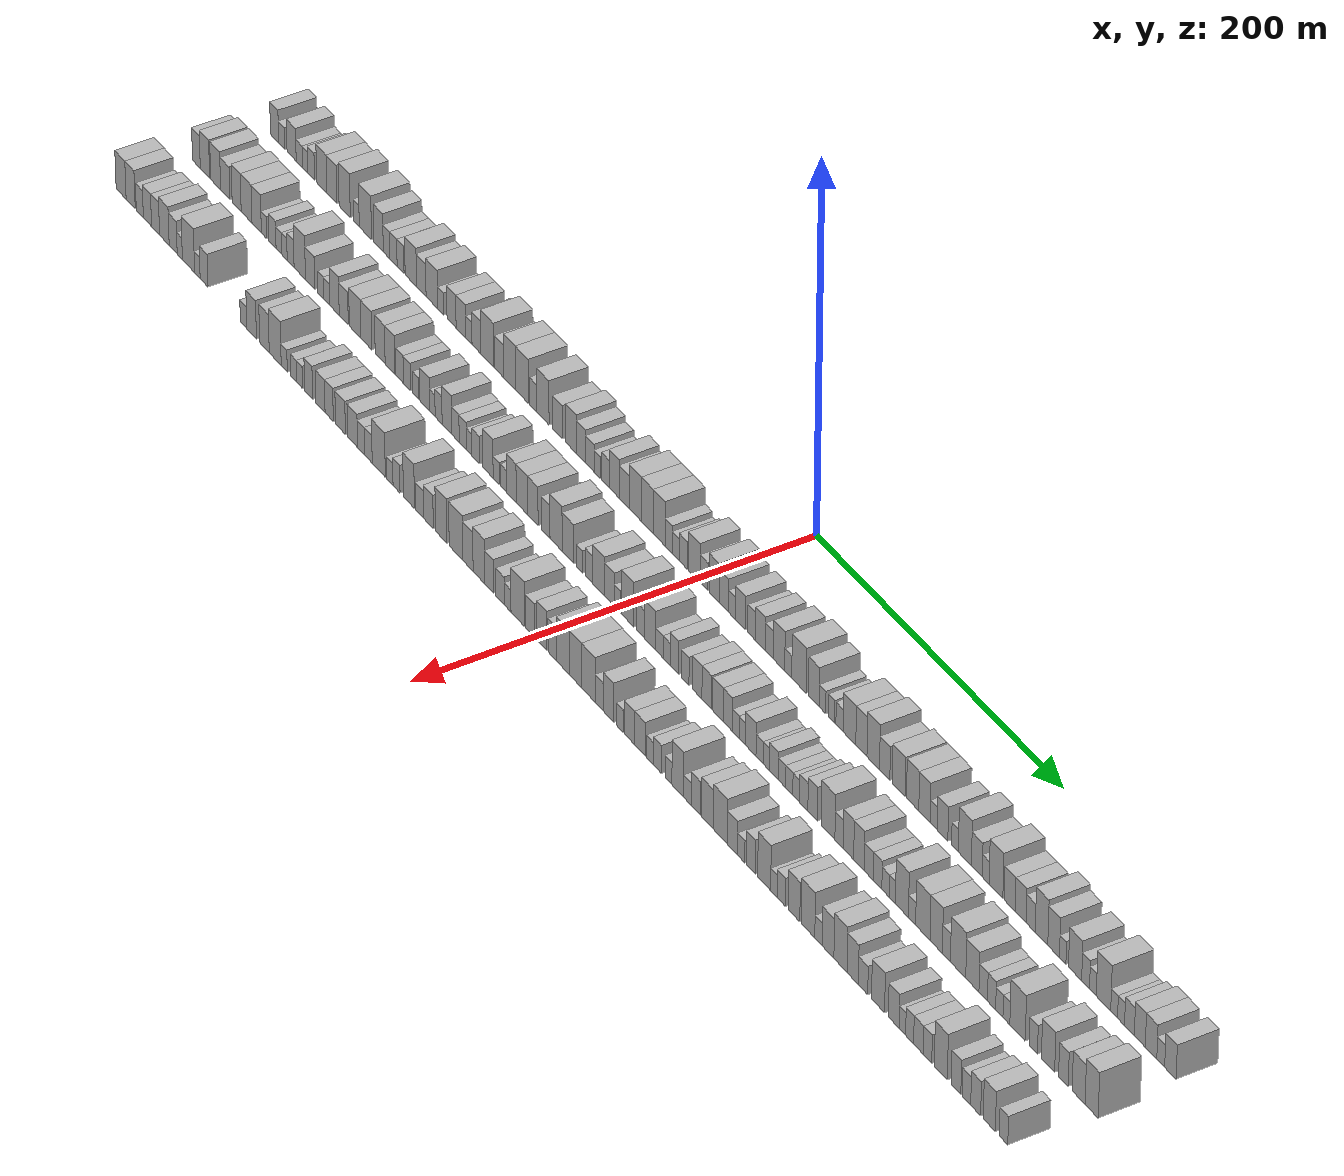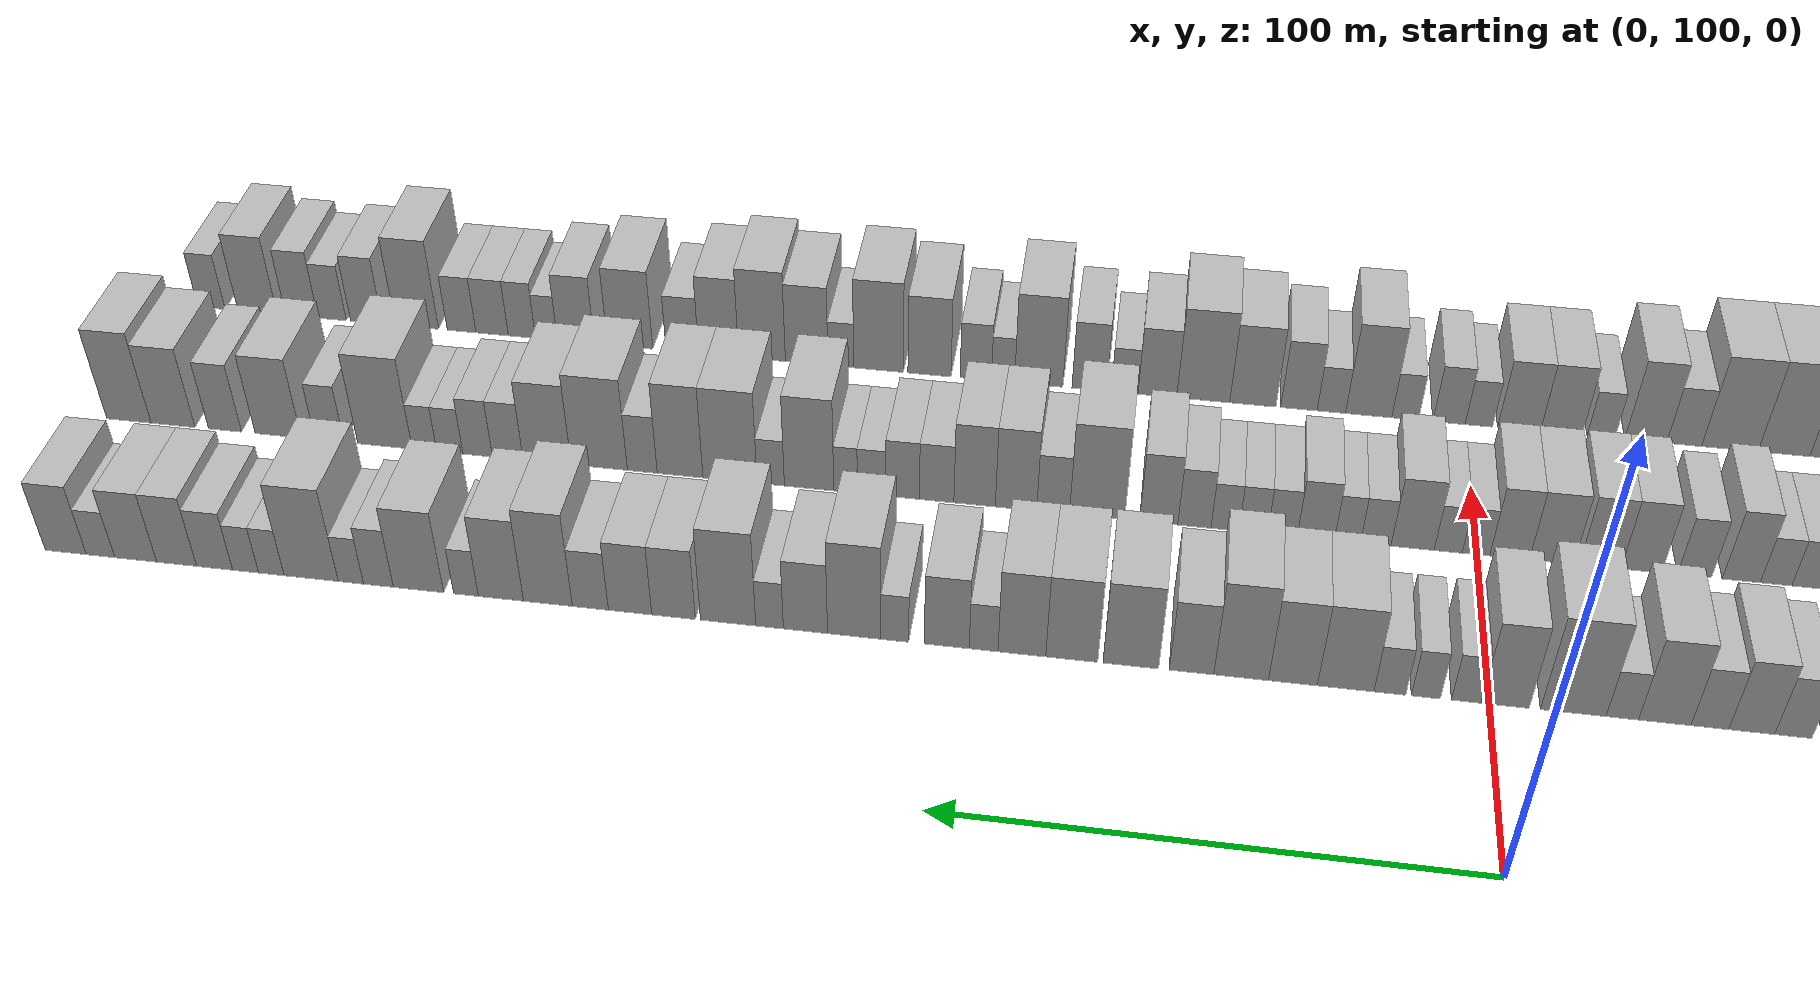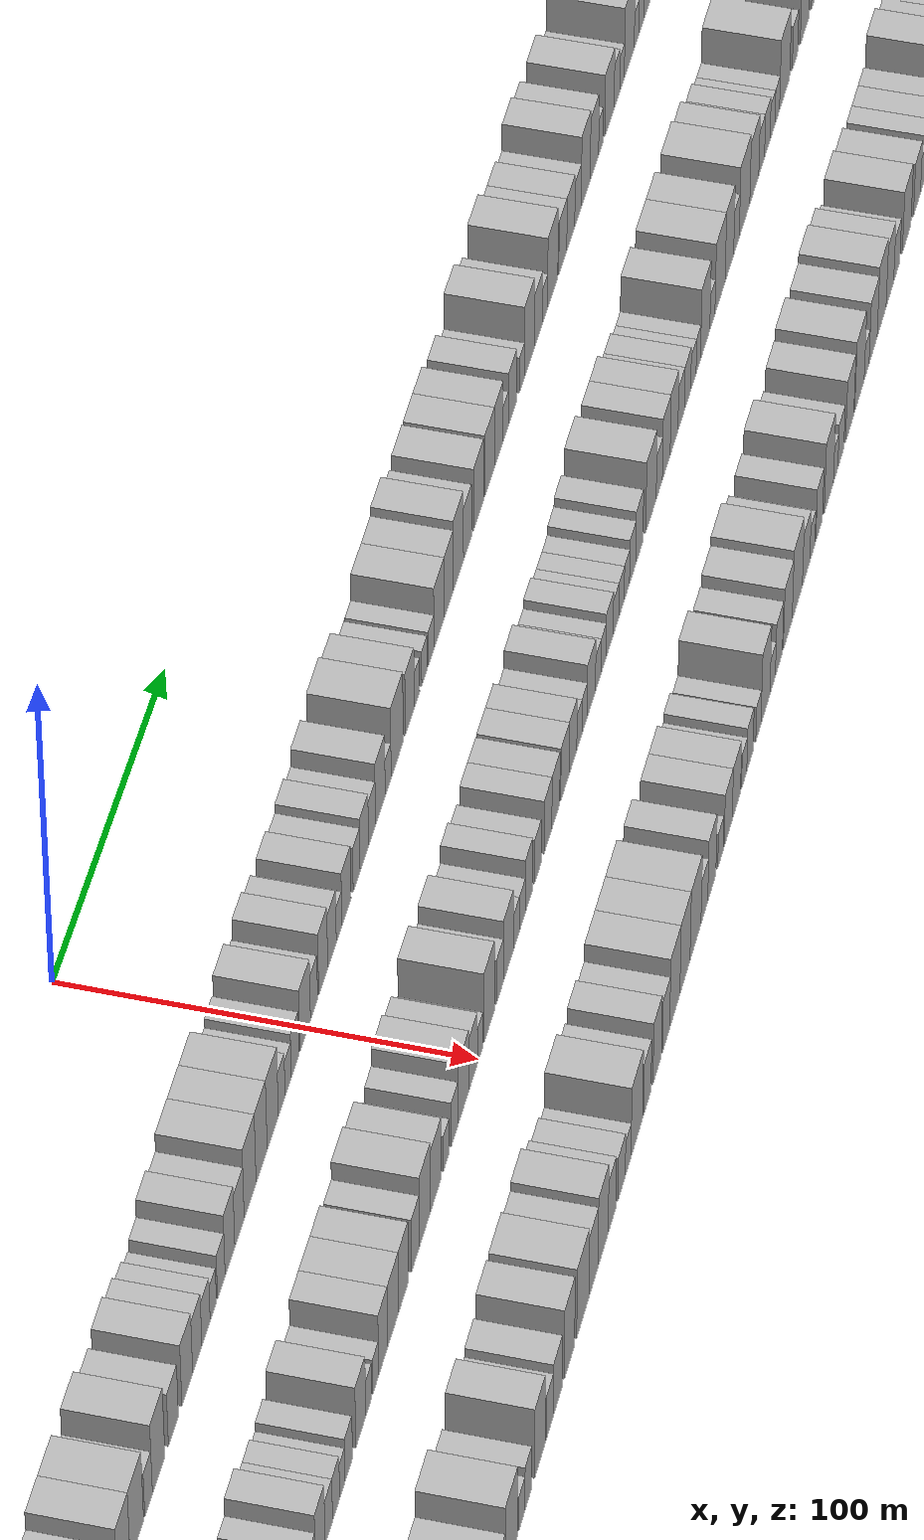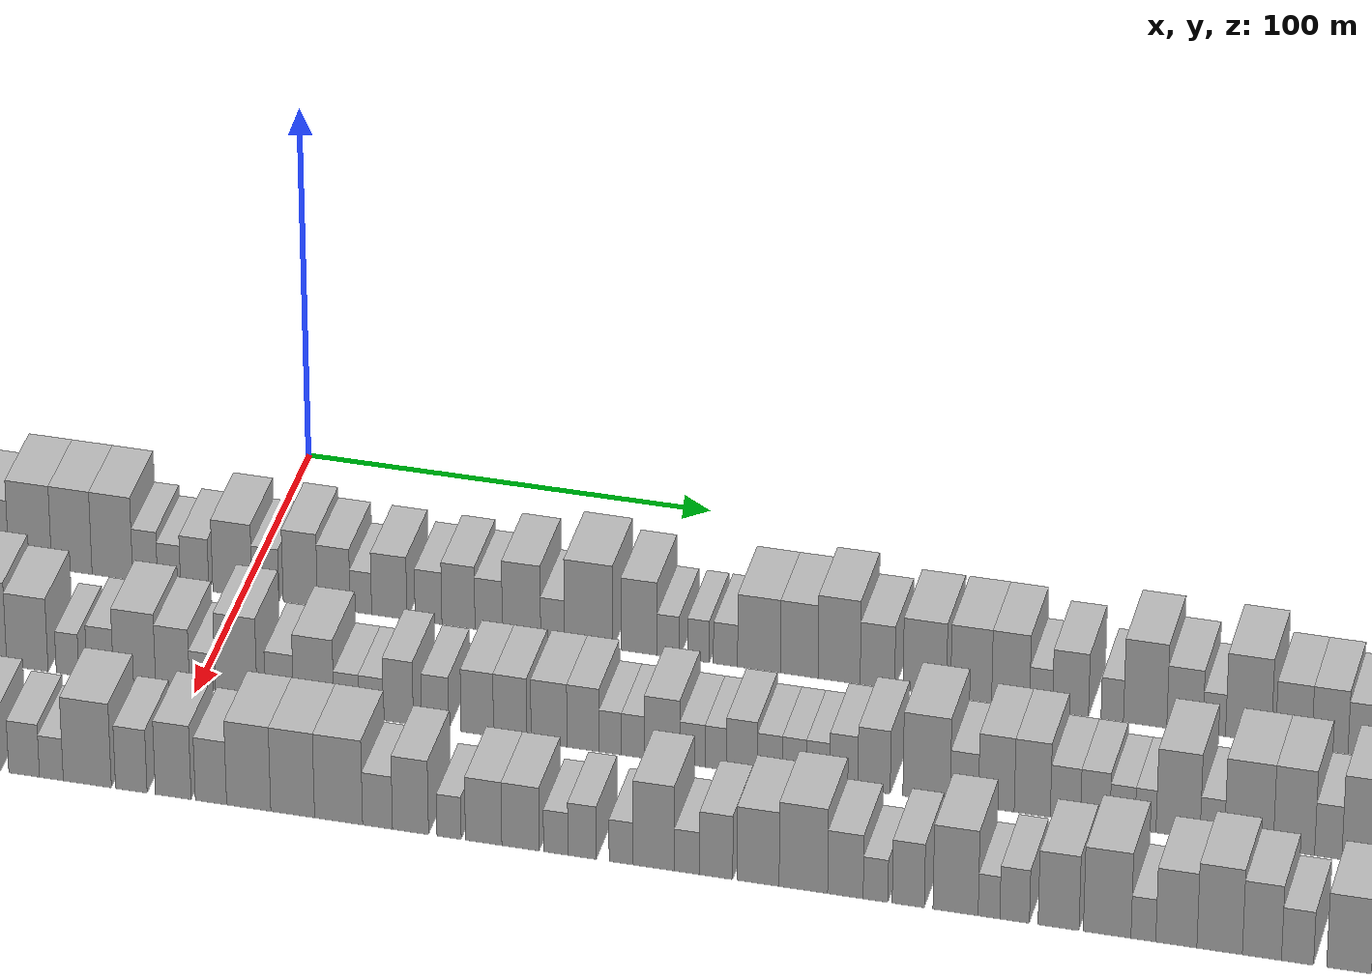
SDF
<sdf version="1.6">
 <world name="default">
  <scene>
   <sky><clouds><speed>12</speed></clouds></sky>
   <ambient>0.4 0.4 0.4 1</ambient>
   <background>0.7 0.7 0.7 1</background>
   <shadows>1</shadows>
  </scene>
  <gravity>0 0 -9.8066</gravity>
  <magnetic_field>6e-06 2.3e-05 -4.2e-05</magnetic_field>
  <physics default="0" name="default_physics" type="ode">
   <ode>
    <solver>
     <type>quick</type>
     <iters>10</iters>
     <sor>1.0</sor>
     <use_dynamic_moi_rescaling>0</use_dynamic_moi_rescaling>
    </solver>
    <constraints>
     <cfm>0</cfm>
     <erp>0.2</erp>
     <contact_max_correcting_vel>100</contact_max_correcting_vel>
     <contact_surface_layer>0.001</contact_surface_layer>
    </constraints>
   </ode>
   <max_step_size>0.004</max_step_size>
   <real_time_factor>1</real_time_factor>
   <real_time_update_rate>250</real_time_update_rate>
  </physics>
  <light name="sun" type="directional">
   <pose>0 0 10 0 0 0</pose>
   <diffuse>0.8 0.8 0.8 1</diffuse>
   <specular>0.2 0.2 0.2 1</specular>
   <attenuation>
    <range>1000</range>
    <constant>0.9</constant>
    <linear>0.01</linear>
    <quadratic>0.001</quadratic>
   </attenuation>
   <direction>-0.5 0.1 -0.9</direction>
  </light>
  <model name="building_1">
   <static>1</static>
   <pose>50.0000 -376.1773 0 0.000000 0.000000 0.000000</pose>
   <link name="link">
    <pose>0 0 9.00 0 0 0</pose>
    <collision name="collision"><geometry><box><size>20.0000 7.6454 18.0000</size></box></geometry></collision>
    <visual name="visual">
     <cast_shadows>0</cast_shadows>
     <geometry><box><size>20.0000 7.6454 18.0000</size></box></geometry>
     <material>
      <script>
       <uri>model://HANNAS_wall/materials/scripts</uri>
       <uri>model://HANNAS_wall/materials/textures</uri>
       <name>vrc/HANNAS_wall</name>
      </script>
     </material>
    </visual>
   </link>
  </model>
  <model name="building_2">
   <static>1</static>
   <pose>50.0000 -369.4280 0 0.000000 0.000000 0.000000</pose>
   <link name="link">
    <pose>0 0 6.00 0 0 0</pose>
    <collision name="collision"><geometry><box><size>20.0000 5.8533 12.0000</size></box></geometry></collision>
    <visual name="visual">
     <cast_shadows>0</cast_shadows>
     <geometry><box><size>20.0000 5.8533 12.0000</size></box></geometry>
     <material>
      <script>
       <uri>model://HANNAS_wall/materials/scripts</uri>
       <uri>model://HANNAS_wall/materials/textures</uri>
       <name>vrc/HANNAS_wall</name>
      </script>
     </material>
    </visual>
   </link>
  </model>
  <model name="building_3">
   <static>1</static>
   <pose>50.0000 -360.2126 0 0.000000 0.000000 0.000000</pose>
   <link name="link">
    <pose>0 0 9.00 0 0 0</pose>
    <collision name="collision"><geometry><box><size>20.0000 8.5775 18.0000</size></box></geometry></collision>
    <visual name="visual">
     <cast_shadows>0</cast_shadows>
     <geometry><box><size>20.0000 8.5775 18.0000</size></box></geometry>
     <material>
      <script>
       <uri>model://HANNAS_wall/materials/scripts</uri>
       <uri>model://HANNAS_wall/materials/textures</uri>
       <name>vrc/HANNAS_wall</name>
      </script>
     </material>
    </visual>
   </link>
  </model>
  <model name="building_4">
   <static>1</static>
   <pose>50.0000 -352.9689 0 0.000000 0.000000 0.000000</pose>
   <link name="link">
    <pose>0 0 6.00 0 0 0</pose>
    <collision name="collision"><geometry><box><size>20.0000 5.9098 12.0000</size></box></geometry></collision>
    <visual name="visual">
     <cast_shadows>0</cast_shadows>
     <geometry><box><size>20.0000 5.9098 12.0000</size></box></geometry>
     <material>
      <script>
       <uri>model://HANNAS_wall/materials/scripts</uri>
       <uri>model://HANNAS_wall/materials/textures</uri>
       <name>vrc/HANNAS_wall</name>
      </script>
     </material>
    </visual>
   </link>
  </model>
  <model name="building_5">
   <static>1</static>
   <pose>50.0000 -347.6071 0 0.000000 0.000000 0.000000</pose>
   <link name="link">
    <pose>0 0 6.00 0 0 0</pose>
    <collision name="collision"><geometry><box><size>20.0000 4.8138 12.0000</size></box></geometry></collision>
    <visual name="visual">
     <cast_shadows>0</cast_shadows>
     <geometry><box><size>20.0000 4.8138 12.0000</size></box></geometry>
     <material>
      <script>
       <uri>model://HANNAS_wall/materials/scripts</uri>
       <uri>model://HANNAS_wall/materials/textures</uri>
       <name>vrc/HANNAS_wall</name>
      </script>
     </material>
    </visual>
   </link>
  </model>
  <model name="building_6">
   <static>1</static>
   <pose>50.0000 -341.9964 0 0.000000 0.000000 0.000000</pose>
   <link name="link">
    <pose>0 0 7.50 0 0 0</pose>
    <collision name="collision"><geometry><box><size>20.0000 6.4076 15.0000</size></box></geometry></collision>
    <visual name="visual">
     <cast_shadows>0</cast_shadows>
     <geometry><box><size>20.0000 6.4076 15.0000</size></box></geometry>
     <material>
      <script>
       <uri>model://HANNAS_wall/materials/scripts</uri>
       <uri>model://HANNAS_wall/materials/textures</uri>
       <name>vrc/HANNAS_wall</name>
      </script>
     </material>
    </visual>
   </link>
  </model>
  <model name="building_7">
   <static>1</static>
   <pose>50.0000 -332.0853 0 0.000000 0.000000 0.000000</pose>
   <link name="link">
    <pose>0 0 10.50 0 0 0</pose>
    <collision name="collision"><geometry><box><size>20.0000 9.4145 21.0000</size></box></geometry></collision>
    <visual name="visual">
     <cast_shadows>0</cast_shadows>
     <geometry><box><size>20.0000 9.4145 21.0000</size></box></geometry>
     <material>
      <script>
       <uri>model://HANNAS_wall/materials/scripts</uri>
       <uri>model://HANNAS_wall/materials/textures</uri>
       <name>vrc/HANNAS_wall</name>
      </script>
     </material>
    </visual>
   </link>
  </model>
  <model name="building_8">
   <static>1</static>
   <pose>50.0000 -322.7095 0 0.000000 0.000000 0.000000</pose>
   <link name="link">
    <pose>0 0 10.50 0 0 0</pose>
    <collision name="collision"><geometry><box><size>20.0000 9.3371 21.0000</size></box></geometry></collision>
    <visual name="visual">
     <cast_shadows>0</cast_shadows>
     <geometry><box><size>20.0000 9.3371 21.0000</size></box></geometry>
     <material>
      <script>
       <uri>model://HANNAS_wall/materials/scripts</uri>
       <uri>model://HANNAS_wall/materials/textures</uri>
       <name>vrc/HANNAS_wall</name>
      </script>
     </material>
    </visual>
   </link>
  </model>
  <model name="building_9">
   <static>1</static>
   <pose>50.0000 -310.8706 0 0.000000 0.000000 0.000000</pose>
   <link name="link">
    <pose>0 0 12.00 0 0 0</pose>
    <collision name="collision"><geometry><box><size>20.0000 10.3408 24.0000</size></box></geometry></collision>
    <visual name="visual">
     <cast_shadows>0</cast_shadows>
     <geometry><box><size>20.0000 10.3408 24.0000</size></box></geometry>
     <material>
      <script>
       <uri>model://HANNAS_wall/materials/scripts</uri>
       <uri>model://HANNAS_wall/materials/textures</uri>
       <name>vrc/HANNAS_wall</name>
      </script>
     </material>
    </visual>
   </link>
  </model>
  <model name="building_10">
   <static>1</static>
   <pose>50.0000 -300.0597 0 0.000000 0.000000 0.000000</pose>
   <link name="link">
    <pose>0 0 6.00 0 0 0</pose>
    <collision name="collision"><geometry><box><size>20.0000 5.2810 12.0000</size></box></geometry></collision>
    <visual name="visual">
     <cast_shadows>0</cast_shadows>
     <geometry><box><size>20.0000 5.2810 12.0000</size></box></geometry>
     <material>
      <script>
       <uri>model://HANNAS_wall/materials/scripts</uri>
       <uri>model://HANNAS_wall/materials/textures</uri>
       <name>vrc/HANNAS_wall</name>
      </script>
     </material>
    </visual>
   </link>
  </model>
  <model name="building_11">
   <static>1</static>
   <pose>50.0000 -291.8017 0 0.000000 0.000000 0.000000</pose>
   <link name="link">
    <pose>0 0 12.00 0 0 0</pose>
    <collision name="collision"><geometry><box><size>20.0000 11.2349 24.0000</size></box></geometry></collision>
    <visual name="visual">
     <cast_shadows>0</cast_shadows>
     <geometry><box><size>20.0000 11.2349 24.0000</size></box></geometry>
     <material>
      <script>
       <uri>model://HANNAS_wall/materials/scripts</uri>
       <uri>model://HANNAS_wall/materials/textures</uri>
       <name>vrc/HANNAS_wall</name>
      </script>
     </material>
    </visual>
   </link>
  </model>
  <model name="building_12">
   <static>1</static>
   <pose>50.0000 -279.7944 0 0.000000 0.000000 0.000000</pose>
   <link name="link">
    <pose>0 0 10.50 0 0 0</pose>
    <collision name="collision"><geometry><box><size>20.0000 8.7797 21.0000</size></box></geometry></collision>
    <visual name="visual">
     <cast_shadows>0</cast_shadows>
     <geometry><box><size>20.0000 8.7797 21.0000</size></box></geometry>
     <material>
      <script>
       <uri>model://HANNAS_wall/materials/scripts</uri>
       <uri>model://HANNAS_wall/materials/textures</uri>
       <name>vrc/HANNAS_wall</name>
      </script>
     </material>
    </visual>
   </link>
  </model>
  <model name="building_13">
   <static>1</static>
   <pose>50.0000 -272.3969 0 0.000000 0.000000 0.000000</pose>
   <link name="link">
    <pose>0 0 7.50 0 0 0</pose>
    <collision name="collision"><geometry><box><size>20.0000 6.0153 15.0000</size></box></geometry></collision>
    <visual name="visual">
     <cast_shadows>0</cast_shadows>
     <geometry><box><size>20.0000 6.0153 15.0000</size></box></geometry>
     <material>
      <script>
       <uri>model://HANNAS_wall/materials/scripts</uri>
       <uri>model://HANNAS_wall/materials/textures</uri>
       <name>vrc/HANNAS_wall</name>
      </script>
     </material>
    </visual>
   </link>
  </model>
  <model name="building_14">
   <static>1</static>
   <pose>50.0000 -266.0947 0 0.000000 0.000000 0.000000</pose>
   <link name="link">
    <pose>0 0 7.50 0 0 0</pose>
    <collision name="collision"><geometry><box><size>20.0000 6.5892 15.0000</size></box></geometry></collision>
    <visual name="visual">
     <cast_shadows>0</cast_shadows>
     <geometry><box><size>20.0000 6.5892 15.0000</size></box></geometry>
     <material>
      <script>
       <uri>model://HANNAS_wall/materials/scripts</uri>
       <uri>model://HANNAS_wall/materials/textures</uri>
       <name>vrc/HANNAS_wall</name>
      </script>
     </material>
    </visual>
   </link>
  </model>
  <model name="building_15">
   <static>1</static>
   <pose>50.0000 -259.6454 0 0.000000 0.000000 0.000000</pose>
   <link name="link">
    <pose>0 0 7.50 0 0 0</pose>
    <collision name="collision"><geometry><box><size>20.0000 6.3095 15.0000</size></box></geometry></collision>
    <visual name="visual">
     <cast_shadows>0</cast_shadows>
     <geometry><box><size>20.0000 6.3095 15.0000</size></box></geometry>
     <material>
      <script>
       <uri>model://HANNAS_wall/materials/scripts</uri>
       <uri>model://HANNAS_wall/materials/textures</uri>
       <name>vrc/HANNAS_wall</name>
      </script>
     </material>
    </visual>
   </link>
  </model>
  <model name="building_16">
   <static>1</static>
   <pose>50.0000 -250.3355 0 0.000000 0.000000 0.000000</pose>
   <link name="link">
    <pose>0 0 10.50 0 0 0</pose>
    <collision name="collision"><geometry><box><size>20.0000 10.3103 21.0000</size></box></geometry></collision>
    <visual name="visual">
     <cast_shadows>0</cast_shadows>
     <geometry><box><size>20.0000 10.3103 21.0000</size></box></geometry>
     <material>
      <script>
       <uri>model://HANNAS_wall/materials/scripts</uri>
       <uri>model://HANNAS_wall/materials/textures</uri>
       <name>vrc/HANNAS_wall</name>
      </script>
     </material>
    </visual>
   </link>
  </model>
  <model name="building_17">
   <static>1</static>
   <pose>50.0000 -240.8543 0 0.000000 0.000000 0.000000</pose>
   <link name="link">
    <pose>0 0 9.00 0 0 0</pose>
    <collision name="collision"><geometry><box><size>20.0000 8.6520 18.0000</size></box></geometry></collision>
    <visual name="visual">
     <cast_shadows>0</cast_shadows>
     <geometry><box><size>20.0000 8.6520 18.0000</size></box></geometry>
     <material>
      <script>
       <uri>model://HANNAS_wall/materials/scripts</uri>
       <uri>model://HANNAS_wall/materials/textures</uri>
       <name>vrc/HANNAS_wall</name>
      </script>
     </material>
    </visual>
   </link>
  </model>
  <model name="building_18">
   <static>1</static>
   <pose>50.0000 -231.2981 0 0.000000 0.000000 0.000000</pose>
   <link name="link">
    <pose>0 0 10.50 0 0 0</pose>
    <collision name="collision"><geometry><box><size>20.0000 10.4602 21.0000</size></box></geometry></collision>
    <visual name="visual">
     <cast_shadows>0</cast_shadows>
     <geometry><box><size>20.0000 10.4602 21.0000</size></box></geometry>
     <material>
      <script>
       <uri>model://HANNAS_wall/materials/scripts</uri>
       <uri>model://HANNAS_wall/materials/textures</uri>
       <name>vrc/HANNAS_wall</name>
      </script>
     </material>
    </visual>
   </link>
  </model>
  <model name="building_19">
   <static>1</static>
   <pose>50.0000 -223.3502 0 0.000000 0.000000 0.000000</pose>
   <link name="link">
    <pose>0 0 6.00 0 0 0</pose>
    <collision name="collision"><geometry><box><size>20.0000 5.4357 12.0000</size></box></geometry></collision>
    <visual name="visual">
     <cast_shadows>0</cast_shadows>
     <geometry><box><size>20.0000 5.4357 12.0000</size></box></geometry>
     <material>
      <script>
       <uri>model://HANNAS_wall/materials/scripts</uri>
       <uri>model://HANNAS_wall/materials/textures</uri>
       <name>vrc/HANNAS_wall</name>
      </script>
     </material>
    </visual>
   </link>
  </model>
  <model name="building_20">
   <static>1</static>
   <pose>50.0000 -213.5637 0 0.000000 0.000000 0.000000</pose>
   <link name="link">
    <pose>0 0 9.00 0 0 0</pose>
    <collision name="collision"><geometry><box><size>20.0000 8.1372 18.0000</size></box></geometry></collision>
    <visual name="visual">
     <cast_shadows>0</cast_shadows>
     <geometry><box><size>20.0000 8.1372 18.0000</size></box></geometry>
     <material>
      <script>
       <uri>model://HANNAS_wall/materials/scripts</uri>
       <uri>model://HANNAS_wall/materials/textures</uri>
       <name>vrc/HANNAS_wall</name>
      </script>
     </material>
    </visual>
   </link>
  </model>
  <model name="building_21">
   <static>1</static>
   <pose>50.0000 -205.2399 0 0.000000 0.000000 0.000000</pose>
   <link name="link">
    <pose>0 0 9.00 0 0 0</pose>
    <collision name="collision"><geometry><box><size>20.0000 8.5105 18.0000</size></box></geometry></collision>
    <visual name="visual">
     <cast_shadows>0</cast_shadows>
     <geometry><box><size>20.0000 8.5105 18.0000</size></box></geometry>
     <material>
      <script>
       <uri>model://HANNAS_wall/materials/scripts</uri>
       <uri>model://HANNAS_wall/materials/textures</uri>
       <name>vrc/HANNAS_wall</name>
      </script>
     </material>
    </visual>
   </link>
  </model>
  <model name="building_22">
   <static>1</static>
   <pose>50.0000 -198.1130 0 0.000000 0.000000 0.000000</pose>
   <link name="link">
    <pose>0 0 6.00 0 0 0</pose>
    <collision name="collision"><geometry><box><size>20.0000 5.7434 12.0000</size></box></geometry></collision>
    <visual name="visual">
     <cast_shadows>0</cast_shadows>
     <geometry><box><size>20.0000 5.7434 12.0000</size></box></geometry>
     <material>
      <script>
       <uri>model://HANNAS_wall/materials/scripts</uri>
       <uri>model://HANNAS_wall/materials/textures</uri>
       <name>vrc/HANNAS_wall</name>
      </script>
     </material>
    </visual>
   </link>
  </model>
  <model name="building_23">
   <static>1</static>
   <pose>50.0000 -191.3917 0 0.000000 0.000000 0.000000</pose>
   <link name="link">
    <pose>0 0 9.00 0 0 0</pose>
    <collision name="collision"><geometry><box><size>20.0000 7.6992 18.0000</size></box></geometry></collision>
    <visual name="visual">
     <cast_shadows>0</cast_shadows>
     <geometry><box><size>20.0000 7.6992 18.0000</size></box></geometry>
     <material>
      <script>
       <uri>model://HANNAS_wall/materials/scripts</uri>
       <uri>model://HANNAS_wall/materials/textures</uri>
       <name>vrc/HANNAS_wall</name>
      </script>
     </material>
    </visual>
   </link>
  </model>
  <model name="building_24">
   <static>1</static>
   <pose>50.0000 -181.7386 0 0.000000 0.000000 0.000000</pose>
   <link name="link">
    <pose>0 0 12.00 0 0 0</pose>
    <collision name="collision"><geometry><box><size>20.0000 11.6071 24.0000</size></box></geometry></collision>
    <visual name="visual">
     <cast_shadows>0</cast_shadows>
     <geometry><box><size>20.0000 11.6071 24.0000</size></box></geometry>
     <material>
      <script>
       <uri>model://HANNAS_wall/materials/scripts</uri>
       <uri>model://HANNAS_wall/materials/textures</uri>
       <name>vrc/HANNAS_wall</name>
      </script>
     </material>
    </visual>
   </link>
  </model>
  <model name="building_25">
   <static>1</static>
   <pose>50.0000 -170.9061 0 0.000000 0.000000 0.000000</pose>
   <link name="link">
    <pose>0 0 9.00 0 0 0</pose>
    <collision name="collision"><geometry><box><size>20.0000 8.0578 18.0000</size></box></geometry></collision>
    <visual name="visual">
     <cast_shadows>0</cast_shadows>
     <geometry><box><size>20.0000 8.0578 18.0000</size></box></geometry>
     <material>
      <script>
       <uri>model://HANNAS_wall/materials/scripts</uri>
       <uri>model://HANNAS_wall/materials/textures</uri>
       <name>vrc/HANNAS_wall</name>
      </script>
     </material>
    </visual>
   </link>
  </model>
  <model name="building_26">
   <static>1</static>
   <pose>50.0000 -161.7158 0 0.000000 0.000000 0.000000</pose>
   <link name="link">
    <pose>0 0 12.00 0 0 0</pose>
    <collision name="collision"><geometry><box><size>20.0000 10.3230 24.0000</size></box></geometry></collision>
    <visual name="visual">
     <cast_shadows>0</cast_shadows>
     <geometry><box><size>20.0000 10.3230 24.0000</size></box></geometry>
     <material>
      <script>
       <uri>model://HANNAS_wall/materials/scripts</uri>
       <uri>model://HANNAS_wall/materials/textures</uri>
       <name>vrc/HANNAS_wall</name>
      </script>
     </material>
    </visual>
   </link>
  </model>
  <model name="building_27">
   <static>1</static>
   <pose>50.0000 -150.8850 0 0.000000 0.000000 0.000000</pose>
   <link name="link">
    <pose>0 0 12.00 0 0 0</pose>
    <collision name="collision"><geometry><box><size>20.0000 11.3386 24.0000</size></box></geometry></collision>
    <visual name="visual">
     <cast_shadows>0</cast_shadows>
     <geometry><box><size>20.0000 11.3386 24.0000</size></box></geometry>
     <material>
      <script>
       <uri>model://HANNAS_wall/materials/scripts</uri>
       <uri>model://HANNAS_wall/materials/textures</uri>
       <name>vrc/HANNAS_wall</name>
      </script>
     </material>
    </visual>
   </link>
  </model>
  <model name="building_28">
   <static>1</static>
   <pose>50.0000 -140.9784 0 0.000000 0.000000 0.000000</pose>
   <link name="link">
    <pose>0 0 7.50 0 0 0</pose>
    <collision name="collision"><geometry><box><size>20.0000 6.4745 15.0000</size></box></geometry></collision>
    <visual name="visual">
     <cast_shadows>0</cast_shadows>
     <geometry><box><size>20.0000 6.4745 15.0000</size></box></geometry>
     <material>
      <script>
       <uri>model://HANNAS_wall/materials/scripts</uri>
       <uri>model://HANNAS_wall/materials/textures</uri>
       <name>vrc/HANNAS_wall</name>
      </script>
     </material>
    </visual>
   </link>
  </model>
  <model name="building_29">
   <static>1</static>
   <pose>50.0000 -132.4195 0 0.000000 0.000000 0.000000</pose>
   <link name="link">
    <pose>0 0 12.00 0 0 0</pose>
    <collision name="collision"><geometry><box><size>20.0000 10.6431 24.0000</size></box></geometry></collision>
    <visual name="visual">
     <cast_shadows>0</cast_shadows>
     <geometry><box><size>20.0000 10.6431 24.0000</size></box></geometry>
     <material>
      <script>
       <uri>model://HANNAS_wall/materials/scripts</uri>
       <uri>model://HANNAS_wall/materials/textures</uri>
       <name>vrc/HANNAS_wall</name>
      </script>
     </material>
    </visual>
   </link>
  </model>
  <model name="building_30">
   <static>1</static>
   <pose>50.0000 -119.7952 0 0.000000 0.000000 0.000000</pose>
   <link name="link">
    <pose>0 0 9.00 0 0 0</pose>
    <collision name="collision"><geometry><box><size>20.0000 8.6057 18.0000</size></box></geometry></collision>
    <visual name="visual">
     <cast_shadows>0</cast_shadows>
     <geometry><box><size>20.0000 8.6057 18.0000</size></box></geometry>
     <material>
      <script>
       <uri>model://HANNAS_wall/materials/scripts</uri>
       <uri>model://HANNAS_wall/materials/textures</uri>
       <name>vrc/HANNAS_wall</name>
      </script>
     </material>
    </visual>
   </link>
  </model>
  <model name="building_31">
   <static>1</static>
   <pose>50.0000 -107.8266 0 0.000000 0.000000 0.000000</pose>
   <link name="link">
    <pose>0 0 10.50 0 0 0</pose>
    <collision name="collision"><geometry><box><size>20.0000 9.3315 21.0000</size></box></geometry></collision>
    <visual name="visual">
     <cast_shadows>0</cast_shadows>
     <geometry><box><size>20.0000 9.3315 21.0000</size></box></geometry>
     <material>
      <script>
       <uri>model://HANNAS_wall/materials/scripts</uri>
       <uri>model://HANNAS_wall/materials/textures</uri>
       <name>vrc/HANNAS_wall</name>
      </script>
     </material>
    </visual>
   </link>
  </model>
  <model name="building_32">
   <static>1</static>
   <pose>50.0000 -99.1483 0 0.000000 0.000000 0.000000</pose>
   <link name="link">
    <pose>0 0 9.00 0 0 0</pose>
    <collision name="collision"><geometry><box><size>20.0000 8.0252 18.0000</size></box></geometry></collision>
    <visual name="visual">
     <cast_shadows>0</cast_shadows>
     <geometry><box><size>20.0000 8.0252 18.0000</size></box></geometry>
     <material>
      <script>
       <uri>model://HANNAS_wall/materials/scripts</uri>
       <uri>model://HANNAS_wall/materials/textures</uri>
       <name>vrc/HANNAS_wall</name>
      </script>
     </material>
    </visual>
   </link>
  </model>
  <model name="building_33">
   <static>1</static>
   <pose>50.0000 -91.5159 0 0.000000 0.000000 0.000000</pose>
   <link name="link">
    <pose>0 0 7.50 0 0 0</pose>
    <collision name="collision"><geometry><box><size>20.0000 7.2396 15.0000</size></box></geometry></collision>
    <visual name="visual">
     <cast_shadows>0</cast_shadows>
     <geometry><box><size>20.0000 7.2396 15.0000</size></box></geometry>
     <material>
      <script>
       <uri>model://HANNAS_wall/materials/scripts</uri>
       <uri>model://HANNAS_wall/materials/textures</uri>
       <name>vrc/HANNAS_wall</name>
      </script>
     </material>
    </visual>
   </link>
  </model>
  <model name="building_34">
   <static>1</static>
   <pose>50.0000 -85.1472 0 0.000000 0.000000 0.000000</pose>
   <link name="link">
    <pose>0 0 6.00 0 0 0</pose>
    <collision name="collision"><geometry><box><size>20.0000 5.4978 12.0000</size></box></geometry></collision>
    <visual name="visual">
     <cast_shadows>0</cast_shadows>
     <geometry><box><size>20.0000 5.4978 12.0000</size></box></geometry>
     <material>
      <script>
       <uri>model://HANNAS_wall/materials/scripts</uri>
       <uri>model://HANNAS_wall/materials/textures</uri>
       <name>vrc/HANNAS_wall</name>
      </script>
     </material>
    </visual>
   </link>
  </model>
  <model name="building_35">
   <static>1</static>
   <pose>50.0000 -78.0535 0 0.000000 0.000000 0.000000</pose>
   <link name="link">
    <pose>0 0 7.50 0 0 0</pose>
    <collision name="collision"><geometry><box><size>20.0000 6.6894 15.0000</size></box></geometry></collision>
    <visual name="visual">
     <cast_shadows>0</cast_shadows>
     <geometry><box><size>20.0000 6.6894 15.0000</size></box></geometry>
     <material>
      <script>
       <uri>model://HANNAS_wall/materials/scripts</uri>
       <uri>model://HANNAS_wall/materials/textures</uri>
       <name>vrc/HANNAS_wall</name>
      </script>
     </material>
    </visual>
   </link>
  </model>
  <model name="building_36">
   <static>1</static>
   <pose>50.0000 -70.4153 0 0.000000 0.000000 0.000000</pose>
   <link name="link">
    <pose>0 0 10.50 0 0 0</pose>
    <collision name="collision"><geometry><box><size>20.0000 8.5872 21.0000</size></box></geometry></collision>
    <visual name="visual">
     <cast_shadows>0</cast_shadows>
     <geometry><box><size>20.0000 8.5872 21.0000</size></box></geometry>
     <material>
      <script>
       <uri>model://HANNAS_wall/materials/scripts</uri>
       <uri>model://HANNAS_wall/materials/textures</uri>
       <name>vrc/HANNAS_wall</name>
      </script>
     </material>
    </visual>
   </link>
  </model>
  <model name="building_37">
   <static>1</static>
   <pose>50.0000 -61.9511 0 0.000000 0.000000 0.000000</pose>
   <link name="link">
    <pose>0 0 9.00 0 0 0</pose>
    <collision name="collision"><geometry><box><size>20.0000 8.3411 18.0000</size></box></geometry></collision>
    <visual name="visual">
     <cast_shadows>0</cast_shadows>
     <geometry><box><size>20.0000 8.3411 18.0000</size></box></geometry>
     <material>
      <script>
       <uri>model://HANNAS_wall/materials/scripts</uri>
       <uri>model://HANNAS_wall/materials/textures</uri>
       <name>vrc/HANNAS_wall</name>
      </script>
     </material>
    </visual>
   </link>
  </model>
  <model name="building_38">
   <static>1</static>
   <pose>50.0000 -52.4399 0 0.000000 0.000000 0.000000</pose>
   <link name="link">
    <pose>0 0 12.00 0 0 0</pose>
    <collision name="collision"><geometry><box><size>20.0000 10.6813 24.0000</size></box></geometry></collision>
    <visual name="visual">
     <cast_shadows>0</cast_shadows>
     <geometry><box><size>20.0000 10.6813 24.0000</size></box></geometry>
     <material>
      <script>
       <uri>model://HANNAS_wall/materials/scripts</uri>
       <uri>model://HANNAS_wall/materials/textures</uri>
       <name>vrc/HANNAS_wall</name>
      </script>
     </material>
    </visual>
   </link>
  </model>
  <model name="building_39">
   <static>1</static>
   <pose>50.0000 -42.0835 0 0.000000 0.000000 0.000000</pose>
   <link name="link">
    <pose>0 0 12.00 0 0 0</pose>
    <collision name="collision"><geometry><box><size>20.0000 10.0317 24.0000</size></box></geometry></collision>
    <visual name="visual">
     <cast_shadows>0</cast_shadows>
     <geometry><box><size>20.0000 10.0317 24.0000</size></box></geometry>
     <material>
      <script>
       <uri>model://HANNAS_wall/materials/scripts</uri>
       <uri>model://HANNAS_wall/materials/textures</uri>
       <name>vrc/HANNAS_wall</name>
      </script>
     </material>
    </visual>
   </link>
  </model>
  <model name="building_40">
   <static>1</static>
   <pose>50.0000 -32.0134 0 0.000000 0.000000 0.000000</pose>
   <link name="link">
    <pose>0 0 12.00 0 0 0</pose>
    <collision name="collision"><geometry><box><size>20.0000 10.1085 24.0000</size></box></geometry></collision>
    <visual name="visual">
     <cast_shadows>0</cast_shadows>
     <geometry><box><size>20.0000 10.1085 24.0000</size></box></geometry>
     <material>
      <script>
       <uri>model://HANNAS_wall/materials/scripts</uri>
       <uri>model://HANNAS_wall/materials/textures</uri>
       <name>vrc/HANNAS_wall</name>
      </script>
     </material>
    </visual>
   </link>
  </model>
  <model name="building_41">
   <static>1</static>
   <pose>50.0000 -23.8948 0 0.000000 0.000000 0.000000</pose>
   <link name="link">
    <pose>0 0 7.50 0 0 0</pose>
    <collision name="collision"><geometry><box><size>20.0000 6.1287 15.0000</size></box></geometry></collision>
    <visual name="visual">
     <cast_shadows>0</cast_shadows>
     <geometry><box><size>20.0000 6.1287 15.0000</size></box></geometry>
     <material>
      <script>
       <uri>model://HANNAS_wall/materials/scripts</uri>
       <uri>model://HANNAS_wall/materials/textures</uri>
       <name>vrc/HANNAS_wall</name>
      </script>
     </material>
    </visual>
   </link>
  </model>
  <model name="building_42">
   <static>1</static>
   <pose>50.0000 -17.9793 0 0.000000 0.000000 0.000000</pose>
   <link name="link">
    <pose>0 0 6.00 0 0 0</pose>
    <collision name="collision"><geometry><box><size>20.0000 5.7023 12.0000</size></box></geometry></collision>
    <visual name="visual">
     <cast_shadows>0</cast_shadows>
     <geometry><box><size>20.0000 5.7023 12.0000</size></box></geometry>
     <material>
      <script>
       <uri>model://HANNAS_wall/materials/scripts</uri>
       <uri>model://HANNAS_wall/materials/textures</uri>
       <name>vrc/HANNAS_wall</name>
      </script>
     </material>
    </visual>
   </link>
  </model>
  <model name="building_43">
   <static>1</static>
   <pose>50.0000 -11.6382 0 0.000000 0.000000 0.000000</pose>
   <link name="link">
    <pose>0 0 7.50 0 0 0</pose>
    <collision name="collision"><geometry><box><size>20.0000 6.9798 15.0000</size></box></geometry></collision>
    <visual name="visual">
     <cast_shadows>0</cast_shadows>
     <geometry><box><size>20.0000 6.9798 15.0000</size></box></geometry>
     <material>
      <script>
       <uri>model://HANNAS_wall/materials/scripts</uri>
       <uri>model://HANNAS_wall/materials/textures</uri>
       <name>vrc/HANNAS_wall</name>
      </script>
     </material>
    </visual>
   </link>
  </model>
  <model name="building_44">
   <static>1</static>
   <pose>50.0000 -2.2863 0 0.000000 0.000000 0.000000</pose>
   <link name="link">
    <pose>0 0 10.50 0 0 0</pose>
    <collision name="collision"><geometry><box><size>20.0000 9.7241 21.0000</size></box></geometry></collision>
    <visual name="visual">
     <cast_shadows>0</cast_shadows>
     <geometry><box><size>20.0000 9.7241 21.0000</size></box></geometry>
     <material>
      <script>
       <uri>model://HANNAS_wall/materials/scripts</uri>
       <uri>model://HANNAS_wall/materials/textures</uri>
       <name>vrc/HANNAS_wall</name>
      </script>
     </material>
    </visual>
   </link>
  </model>
  <model name="building_45">
   <static>1</static>
   <pose>50.0000 5.8928 0 0.000000 0.000000 0.000000</pose>
   <link name="link">
    <pose>0 0 7.50 0 0 0</pose>
    <collision name="collision"><geometry><box><size>20.0000 6.6339 15.0000</size></box></geometry></collision>
    <visual name="visual">
     <cast_shadows>0</cast_shadows>
     <geometry><box><size>20.0000 6.6339 15.0000</size></box></geometry>
     <material>
      <script>
       <uri>model://HANNAS_wall/materials/scripts</uri>
       <uri>model://HANNAS_wall/materials/textures</uri>
       <name>vrc/HANNAS_wall</name>
      </script>
     </material>
    </visual>
   </link>
  </model>
  <model name="building_46">
   <static>1</static>
   <pose>50.0000 14.4364 0 0.000000 0.000000 0.000000</pose>
   <link name="link">
    <pose>0 0 10.50 0 0 0</pose>
    <collision name="collision"><geometry><box><size>20.0000 8.4533 21.0000</size></box></geometry></collision>
    <visual name="visual">
     <cast_shadows>0</cast_shadows>
     <geometry><box><size>20.0000 8.4533 21.0000</size></box></geometry>
     <material>
      <script>
       <uri>model://HANNAS_wall/materials/scripts</uri>
       <uri>model://HANNAS_wall/materials/textures</uri>
       <name>vrc/HANNAS_wall</name>
      </script>
     </material>
    </visual>
   </link>
  </model>
  <model name="building_47">
   <static>1</static>
   <pose>50.0000 22.6697 0 0.000000 0.000000 0.000000</pose>
   <link name="link">
    <pose>0 0 9.00 0 0 0</pose>
    <collision name="collision"><geometry><box><size>20.0000 8.0134 18.0000</size></box></geometry></collision>
    <visual name="visual">
     <cast_shadows>0</cast_shadows>
     <geometry><box><size>20.0000 8.0134 18.0000</size></box></geometry>
     <material>
      <script>
       <uri>model://HANNAS_wall/materials/scripts</uri>
       <uri>model://HANNAS_wall/materials/textures</uri>
       <name>vrc/HANNAS_wall</name>
      </script>
     </material>
    </visual>
   </link>
  </model>
  <model name="building_48">
   <static>1</static>
   <pose>50.0000 29.3052 0 0.000000 0.000000 0.000000</pose>
   <link name="link">
    <pose>0 0 6.00 0 0 0</pose>
    <collision name="collision"><geometry><box><size>20.0000 5.2575 12.0000</size></box></geometry></collision>
    <visual name="visual">
     <cast_shadows>0</cast_shadows>
     <geometry><box><size>20.0000 5.2575 12.0000</size></box></geometry>
     <material>
      <script>
       <uri>model://HANNAS_wall/materials/scripts</uri>
       <uri>model://HANNAS_wall/materials/textures</uri>
       <name>vrc/HANNAS_wall</name>
      </script>
     </material>
    </visual>
   </link>
  </model>
  <model name="building_49">
   <static>1</static>
   <pose>50.0000 36.2653 0 0.000000 0.000000 0.000000</pose>
   <link name="link">
    <pose>0 0 9.00 0 0 0</pose>
    <collision name="collision"><geometry><box><size>20.0000 8.6627 18.0000</size></box></geometry></collision>
    <visual name="visual">
     <cast_shadows>0</cast_shadows>
     <geometry><box><size>20.0000 8.6627 18.0000</size></box></geometry>
     <material>
      <script>
       <uri>model://HANNAS_wall/materials/scripts</uri>
       <uri>model://HANNAS_wall/materials/textures</uri>
       <name>vrc/HANNAS_wall</name>
      </script>
     </material>
    </visual>
   </link>
  </model>
  <model name="building_50">
   <static>1</static>
   <pose>50.0000 45.8664 0 0.000000 0.000000 0.000000</pose>
   <link name="link">
    <pose>0 0 7.50 0 0 0</pose>
    <collision name="collision"><geometry><box><size>20.0000 6.5394 15.0000</size></box></geometry></collision>
    <visual name="visual">
     <cast_shadows>0</cast_shadows>
     <geometry><box><size>20.0000 6.5394 15.0000</size></box></geometry>
     <material>
      <script>
       <uri>model://HANNAS_wall/materials/scripts</uri>
       <uri>model://HANNAS_wall/materials/textures</uri>
       <name>vrc/HANNAS_wall</name>
      </script>
     </material>
    </visual>
   </link>
  </model>
  <model name="building_51">
   <static>1</static>
   <pose>50.0000 53.1844 0 0.000000 0.000000 0.000000</pose>
   <link name="link">
    <pose>0 0 9.00 0 0 0</pose>
    <collision name="collision"><geometry><box><size>20.0000 8.0967 18.0000</size></box></geometry></collision>
    <visual name="visual">
     <cast_shadows>0</cast_shadows>
     <geometry><box><size>20.0000 8.0967 18.0000</size></box></geometry>
     <material>
      <script>
       <uri>model://HANNAS_wall/materials/scripts</uri>
       <uri>model://HANNAS_wall/materials/textures</uri>
       <name>vrc/HANNAS_wall</name>
      </script>
     </material>
    </visual>
   </link>
  </model>
  <model name="building_52">
   <static>1</static>
   <pose>50.0000 60.5724 0 0.000000 0.000000 0.000000</pose>
   <link name="link">
    <pose>0 0 7.50 0 0 0</pose>
    <collision name="collision"><geometry><box><size>20.0000 6.6792 15.0000</size></box></geometry></collision>
    <visual name="visual">
     <cast_shadows>0</cast_shadows>
     <geometry><box><size>20.0000 6.6792 15.0000</size></box></geometry>
     <material>
      <script>
       <uri>model://HANNAS_wall/materials/scripts</uri>
       <uri>model://HANNAS_wall/materials/textures</uri>
       <name>vrc/HANNAS_wall</name>
      </script>
     </material>
    </visual>
   </link>
  </model>
  <model name="building_53">
   <static>1</static>
   <pose>50.0000 68.5782 0 0.000000 0.000000 0.000000</pose>
   <link name="link">
    <pose>0 0 10.50 0 0 0</pose>
    <collision name="collision"><geometry><box><size>20.0000 9.3326 21.0000</size></box></geometry></collision>
    <visual name="visual">
     <cast_shadows>0</cast_shadows>
     <geometry><box><size>20.0000 9.3326 21.0000</size></box></geometry>
     <material>
      <script>
       <uri>model://HANNAS_wall/materials/scripts</uri>
       <uri>model://HANNAS_wall/materials/textures</uri>
       <name>vrc/HANNAS_wall</name>
      </script>
     </material>
    </visual>
   </link>
  </model>
  <model name="building_54">
   <static>1</static>
   <pose>50.0000 76.1316 0 0.000000 0.000000 0.000000</pose>
   <link name="link">
    <pose>0 0 6.00 0 0 0</pose>
    <collision name="collision"><geometry><box><size>20.0000 5.7741 12.0000</size></box></geometry></collision>
    <visual name="visual">
     <cast_shadows>0</cast_shadows>
     <geometry><box><size>20.0000 5.7741 12.0000</size></box></geometry>
     <material>
      <script>
       <uri>model://HANNAS_wall/materials/scripts</uri>
       <uri>model://HANNAS_wall/materials/textures</uri>
       <name>vrc/HANNAS_wall</name>
      </script>
     </material>
    </visual>
   </link>
  </model>
  <model name="building_55">
   <static>1</static>
   <pose>50.0000 84.9150 0 0.000000 0.000000 0.000000</pose>
   <link name="link">
    <pose>0 0 12.00 0 0 0</pose>
    <collision name="collision"><geometry><box><size>20.0000 11.7927 24.0000</size></box></geometry></collision>
    <visual name="visual">
     <cast_shadows>0</cast_shadows>
     <geometry><box><size>20.0000 11.7927 24.0000</size></box></geometry>
     <material>
      <script>
       <uri>model://HANNAS_wall/materials/scripts</uri>
       <uri>model://HANNAS_wall/materials/textures</uri>
       <name>vrc/HANNAS_wall</name>
      </script>
     </material>
    </visual>
   </link>
  </model>
  <model name="building_56">
   <static>1</static>
   <pose>50.0000 97.1790 0 0.000000 0.000000 0.000000</pose>
   <link name="link">
    <pose>0 0 10.50 0 0 0</pose>
    <collision name="collision"><geometry><box><size>20.0000 8.7355 21.0000</size></box></geometry></collision>
    <visual name="visual">
     <cast_shadows>0</cast_shadows>
     <geometry><box><size>20.0000 8.7355 21.0000</size></box></geometry>
     <material>
      <script>
       <uri>model://HANNAS_wall/materials/scripts</uri>
       <uri>model://HANNAS_wall/materials/textures</uri>
       <name>vrc/HANNAS_wall</name>
      </script>
     </material>
    </visual>
   </link>
  </model>
  <model name="building_57">
   <static>1</static>
   <pose>50.0000 104.2175 0 0.000000 0.000000 0.000000</pose>
   <link name="link">
    <pose>0 0 6.00 0 0 0</pose>
    <collision name="collision"><geometry><box><size>20.0000 5.3414 12.0000</size></box></geometry></collision>
    <visual name="visual">
     <cast_shadows>0</cast_shadows>
     <geometry><box><size>20.0000 5.3414 12.0000</size></box></geometry>
     <material>
      <script>
       <uri>model://HANNAS_wall/materials/scripts</uri>
       <uri>model://HANNAS_wall/materials/textures</uri>
       <name>vrc/HANNAS_wall</name>
      </script>
     </material>
    </visual>
   </link>
  </model>
  <model name="building_58">
   <static>1</static>
   <pose>50.0000 111.5356 0 0.000000 0.000000 0.000000</pose>
   <link name="link">
    <pose>0 0 6.00 0 0 0</pose>
    <collision name="collision"><geometry><box><size>20.0000 5.2949 12.0000</size></box></geometry></collision>
    <visual name="visual">
     <cast_shadows>0</cast_shadows>
     <geometry><box><size>20.0000 5.2949 12.0000</size></box></geometry>
     <material>
      <script>
       <uri>model://HANNAS_wall/materials/scripts</uri>
       <uri>model://HANNAS_wall/materials/textures</uri>
       <name>vrc/HANNAS_wall</name>
      </script>
     </material>
    </visual>
   </link>
  </model>
  <model name="building_59">
   <static>1</static>
   <pose>50.0000 118.0981 0 0.000000 0.000000 0.000000</pose>
   <link name="link">
    <pose>0 0 6.00 0 0 0</pose>
    <collision name="collision"><geometry><box><size>20.0000 5.8301 12.0000</size></box></geometry></collision>
    <visual name="visual">
     <cast_shadows>0</cast_shadows>
     <geometry><box><size>20.0000 5.8301 12.0000</size></box></geometry>
     <material>
      <script>
       <uri>model://HANNAS_wall/materials/scripts</uri>
       <uri>model://HANNAS_wall/materials/textures</uri>
       <name>vrc/HANNAS_wall</name>
      </script>
     </material>
    </visual>
   </link>
  </model>
  <model name="building_60">
   <static>1</static>
   <pose>50.0000 126.1869 0 0.000000 0.000000 0.000000</pose>
   <link name="link">
    <pose>0 0 10.50 0 0 0</pose>
    <collision name="collision"><geometry><box><size>20.0000 10.3473 21.0000</size></box></geometry></collision>
    <visual name="visual">
     <cast_shadows>0</cast_shadows>
     <geometry><box><size>20.0000 10.3473 21.0000</size></box></geometry>
     <material>
      <script>
       <uri>model://HANNAS_wall/materials/scripts</uri>
       <uri>model://HANNAS_wall/materials/textures</uri>
       <name>vrc/HANNAS_wall</name>
      </script>
     </material>
    </visual>
   </link>
  </model>
  <model name="building_61">
   <static>1</static>
   <pose>50.0000 135.8822 0 0.000000 0.000000 0.000000</pose>
   <link name="link">
    <pose>0 0 10.50 0 0 0</pose>
    <collision name="collision"><geometry><box><size>20.0000 9.0435 21.0000</size></box></geometry></collision>
    <visual name="visual">
     <cast_shadows>0</cast_shadows>
     <geometry><box><size>20.0000 9.0435 21.0000</size></box></geometry>
     <material>
      <script>
       <uri>model://HANNAS_wall/materials/scripts</uri>
       <uri>model://HANNAS_wall/materials/textures</uri>
       <name>vrc/HANNAS_wall</name>
      </script>
     </material>
    </visual>
   </link>
  </model>
  <model name="building_62">
   <static>1</static>
   <pose>50.0000 145.4739 0 0.000000 0.000000 0.000000</pose>
   <link name="link">
    <pose>0 0 12.00 0 0 0</pose>
    <collision name="collision"><geometry><box><size>20.0000 10.1399 24.0000</size></box></geometry></collision>
    <visual name="visual">
     <cast_shadows>0</cast_shadows>
     <geometry><box><size>20.0000 10.1399 24.0000</size></box></geometry>
     <material>
      <script>
       <uri>model://HANNAS_wall/materials/scripts</uri>
       <uri>model://HANNAS_wall/materials/textures</uri>
       <name>vrc/HANNAS_wall</name>
      </script>
     </material>
    </visual>
   </link>
  </model>
  <model name="building_63">
   <static>1</static>
   <pose>50.0000 154.6867 0 0.000000 0.000000 0.000000</pose>
   <link name="link">
    <pose>0 0 9.00 0 0 0</pose>
    <collision name="collision"><geometry><box><size>20.0000 8.2855 18.0000</size></box></geometry></collision>
    <visual name="visual">
     <cast_shadows>0</cast_shadows>
     <geometry><box><size>20.0000 8.2855 18.0000</size></box></geometry>
     <material>
      <script>
       <uri>model://HANNAS_wall/materials/scripts</uri>
       <uri>model://HANNAS_wall/materials/textures</uri>
       <name>vrc/HANNAS_wall</name>
      </script>
     </material>
    </visual>
   </link>
  </model>
  <model name="building_64">
   <static>1</static>
   <pose>50.0000 166.0288 0 0.000000 0.000000 0.000000</pose>
   <link name="link">
    <pose>0 0 10.50 0 0 0</pose>
    <collision name="collision"><geometry><box><size>20.0000 10.3989 21.0000</size></box></geometry></collision>
    <visual name="visual">
     <cast_shadows>0</cast_shadows>
     <geometry><box><size>20.0000 10.3989 21.0000</size></box></geometry>
     <material>
      <script>
       <uri>model://HANNAS_wall/materials/scripts</uri>
       <uri>model://HANNAS_wall/materials/textures</uri>
       <name>vrc/HANNAS_wall</name>
      </script>
     </material>
    </visual>
   </link>
  </model>
  <model name="building_65">
   <static>1</static>
   <pose>50.0000 177.1291 0 0.000000 0.000000 0.000000</pose>
   <link name="link">
    <pose>0 0 10.50 0 0 0</pose>
    <collision name="collision"><geometry><box><size>20.0000 9.8017 21.0000</size></box></geometry></collision>
    <visual name="visual">
     <cast_shadows>0</cast_shadows>
     <geometry><box><size>20.0000 9.8017 21.0000</size></box></geometry>
     <material>
      <script>
       <uri>model://HANNAS_wall/materials/scripts</uri>
       <uri>model://HANNAS_wall/materials/textures</uri>
       <name>vrc/HANNAS_wall</name>
      </script>
     </material>
    </visual>
   </link>
  </model>
  <model name="building_66">
   <static>1</static>
   <pose>50.0000 186.5587 0 0.000000 0.000000 0.000000</pose>
   <link name="link">
    <pose>0 0 10.50 0 0 0</pose>
    <collision name="collision"><geometry><box><size>20.0000 9.0574 21.0000</size></box></geometry></collision>
    <visual name="visual">
     <cast_shadows>0</cast_shadows>
     <geometry><box><size>20.0000 9.0574 21.0000</size></box></geometry>
     <material>
      <script>
       <uri>model://HANNAS_wall/materials/scripts</uri>
       <uri>model://HANNAS_wall/materials/textures</uri>
       <name>vrc/HANNAS_wall</name>
      </script>
     </material>
    </visual>
   </link>
  </model>
  <model name="building_67">
   <static>1</static>
   <pose>50.0000 193.8219 0 0.000000 0.000000 0.000000</pose>
   <link name="link">
    <pose>0 0 6.00 0 0 0</pose>
    <collision name="collision"><geometry><box><size>20.0000 5.4691 12.0000</size></box></geometry></collision>
    <visual name="visual">
     <cast_shadows>0</cast_shadows>
     <geometry><box><size>20.0000 5.4691 12.0000</size></box></geometry>
     <material>
      <script>
       <uri>model://HANNAS_wall/materials/scripts</uri>
       <uri>model://HANNAS_wall/materials/textures</uri>
       <name>vrc/HANNAS_wall</name>
      </script>
     </material>
    </visual>
   </link>
  </model>
  <model name="building_68">
   <static>1</static>
   <pose>50.0000 200.8440 0 0.000000 0.000000 0.000000</pose>
   <link name="link">
    <pose>0 0 9.00 0 0 0</pose>
    <collision name="collision"><geometry><box><size>20.0000 8.5750 18.0000</size></box></geometry></collision>
    <visual name="visual">
     <cast_shadows>0</cast_shadows>
     <geometry><box><size>20.0000 8.5750 18.0000</size></box></geometry>
     <material>
      <script>
       <uri>model://HANNAS_wall/materials/scripts</uri>
       <uri>model://HANNAS_wall/materials/textures</uri>
       <name>vrc/HANNAS_wall</name>
      </script>
     </material>
    </visual>
   </link>
  </model>
  <model name="building_69">
   <static>1</static>
   <pose>50.0000 210.7933 0 0.000000 0.000000 0.000000</pose>
   <link name="link">
    <pose>0 0 6.00 0 0 0</pose>
    <collision name="collision"><geometry><box><size>20.0000 5.3235 12.0000</size></box></geometry></collision>
    <visual name="visual">
     <cast_shadows>0</cast_shadows>
     <geometry><box><size>20.0000 5.3235 12.0000</size></box></geometry>
     <material>
      <script>
       <uri>model://HANNAS_wall/materials/scripts</uri>
       <uri>model://HANNAS_wall/materials/textures</uri>
       <name>vrc/HANNAS_wall</name>
      </script>
     </material>
    </visual>
   </link>
  </model>
  <model name="building_70">
   <static>1</static>
   <pose>50.0000 218.5994 0 0.000000 0.000000 0.000000</pose>
   <link name="link">
    <pose>0 0 12.00 0 0 0</pose>
    <collision name="collision"><geometry><box><size>20.0000 10.2888 24.0000</size></box></geometry></collision>
    <visual name="visual">
     <cast_shadows>0</cast_shadows>
     <geometry><box><size>20.0000 10.2888 24.0000</size></box></geometry>
     <material>
      <script>
       <uri>model://HANNAS_wall/materials/scripts</uri>
       <uri>model://HANNAS_wall/materials/textures</uri>
       <name>vrc/HANNAS_wall</name>
      </script>
     </material>
    </visual>
   </link>
  </model>
  <model name="building_71">
   <static>1</static>
   <pose>50.0000 228.0188 0 0.000000 0.000000 0.000000</pose>
   <link name="link">
    <pose>0 0 9.00 0 0 0</pose>
    <collision name="collision"><geometry><box><size>20.0000 8.5498 18.0000</size></box></geometry></collision>
    <visual name="visual">
     <cast_shadows>0</cast_shadows>
     <geometry><box><size>20.0000 8.5498 18.0000</size></box></geometry>
     <material>
      <script>
       <uri>model://HANNAS_wall/materials/scripts</uri>
       <uri>model://HANNAS_wall/materials/textures</uri>
       <name>vrc/HANNAS_wall</name>
      </script>
     </material>
    </visual>
   </link>
  </model>
  <model name="building_72">
   <static>1</static>
   <pose>50.0000 234.9757 0 0.000000 0.000000 0.000000</pose>
   <link name="link">
    <pose>0 0 6.00 0 0 0</pose>
    <collision name="collision"><geometry><box><size>20.0000 5.3641 12.0000</size></box></geometry></collision>
    <visual name="visual">
     <cast_shadows>0</cast_shadows>
     <geometry><box><size>20.0000 5.3641 12.0000</size></box></geometry>
     <material>
      <script>
       <uri>model://HANNAS_wall/materials/scripts</uri>
       <uri>model://HANNAS_wall/materials/textures</uri>
       <name>vrc/HANNAS_wall</name>
      </script>
     </material>
    </visual>
   </link>
  </model>
  <model name="building_73">
   <static>1</static>
   <pose>50.0000 243.0597 0 0.000000 0.000000 0.000000</pose>
   <link name="link">
    <pose>0 0 12.00 0 0 0</pose>
    <collision name="collision"><geometry><box><size>20.0000 10.8039 24.0000</size></box></geometry></collision>
    <visual name="visual">
     <cast_shadows>0</cast_shadows>
     <geometry><box><size>20.0000 10.8039 24.0000</size></box></geometry>
     <material>
      <script>
       <uri>model://HANNAS_wall/materials/scripts</uri>
       <uri>model://HANNAS_wall/materials/textures</uri>
       <name>vrc/HANNAS_wall</name>
      </script>
     </material>
    </visual>
   </link>
  </model>
  <model name="building_74">
   <static>1</static>
   <pose>50.0000 253.7331 0 0.000000 0.000000 0.000000</pose>
   <link name="link">
    <pose>0 0 9.00 0 0 0</pose>
    <collision name="collision"><geometry><box><size>20.0000 8.5429 18.0000</size></box></geometry></collision>
    <visual name="visual">
     <cast_shadows>0</cast_shadows>
     <geometry><box><size>20.0000 8.5429 18.0000</size></box></geometry>
     <material>
      <script>
       <uri>model://HANNAS_wall/materials/scripts</uri>
       <uri>model://HANNAS_wall/materials/textures</uri>
       <name>vrc/HANNAS_wall</name>
      </script>
     </material>
    </visual>
   </link>
  </model>
  <model name="building_75">
   <static>1</static>
   <pose>50.0000 262.2793 0 0.000000 0.000000 0.000000</pose>
   <link name="link">
    <pose>0 0 9.00 0 0 0</pose>
    <collision name="collision"><geometry><box><size>20.0000 8.5495 18.0000</size></box></geometry></collision>
    <visual name="visual">
     <cast_shadows>0</cast_shadows>
     <geometry><box><size>20.0000 8.5495 18.0000</size></box></geometry>
     <material>
      <script>
       <uri>model://HANNAS_wall/materials/scripts</uri>
       <uri>model://HANNAS_wall/materials/textures</uri>
       <name>vrc/HANNAS_wall</name>
      </script>
     </material>
    </visual>
   </link>
  </model>
  <model name="building_76">
   <static>1</static>
   <pose>50.0000 270.1269 0 0.000000 0.000000 0.000000</pose>
   <link name="link">
    <pose>0 0 7.50 0 0 0</pose>
    <collision name="collision"><geometry><box><size>20.0000 7.1458 15.0000</size></box></geometry></collision>
    <visual name="visual">
     <cast_shadows>0</cast_shadows>
     <geometry><box><size>20.0000 7.1458 15.0000</size></box></geometry>
     <material>
      <script>
       <uri>model://HANNAS_wall/materials/scripts</uri>
       <uri>model://HANNAS_wall/materials/textures</uri>
       <name>vrc/HANNAS_wall</name>
      </script>
     </material>
    </visual>
   </link>
  </model>
  <model name="building_77">
   <static>1</static>
   <pose>50.0000 278.5636 0 0.000000 0.000000 0.000000</pose>
   <link name="link">
    <pose>0 0 12.00 0 0 0</pose>
    <collision name="collision"><geometry><box><size>20.0000 9.7276 24.0000</size></box></geometry></collision>
    <visual name="visual">
     <cast_shadows>0</cast_shadows>
     <geometry><box><size>20.0000 9.7276 24.0000</size></box></geometry>
     <material>
      <script>
       <uri>model://HANNAS_wall/materials/scripts</uri>
       <uri>model://HANNAS_wall/materials/textures</uri>
       <name>vrc/HANNAS_wall</name>
      </script>
     </material>
    </visual>
   </link>
  </model>
  <model name="building_78">
   <static>1</static>
   <pose>50.0000 287.9281 0 0.000000 0.000000 0.000000</pose>
   <link name="link">
    <pose>0 0 10.50 0 0 0</pose>
    <collision name="collision"><geometry><box><size>20.0000 9.0013 21.0000</size></box></geometry></collision>
    <visual name="visual">
     <cast_shadows>0</cast_shadows>
     <geometry><box><size>20.0000 9.0013 21.0000</size></box></geometry>
     <material>
      <script>
       <uri>model://HANNAS_wall/materials/scripts</uri>
       <uri>model://HANNAS_wall/materials/textures</uri>
       <name>vrc/HANNAS_wall</name>
      </script>
     </material>
    </visual>
   </link>
  </model>
  <model name="building_79">
   <static>1</static>
   <pose>50.0000 294.9250 0 0.000000 0.000000 0.000000</pose>
   <link name="link">
    <pose>0 0 6.00 0 0 0</pose>
    <collision name="collision"><geometry><box><size>20.0000 4.9925 12.0000</size></box></geometry></collision>
    <visual name="visual">
     <cast_shadows>0</cast_shadows>
     <geometry><box><size>20.0000 4.9925 12.0000</size></box></geometry>
     <material>
      <script>
       <uri>model://HANNAS_wall/materials/scripts</uri>
       <uri>model://HANNAS_wall/materials/textures</uri>
       <name>vrc/HANNAS_wall</name>
      </script>
     </material>
    </visual>
   </link>
  </model>
  <model name="building_80">
   <static>1</static>
   <pose>50.0000 304.4848 0 0.000000 0.000000 0.000000</pose>
   <link name="link">
    <pose>0 0 10.50 0 0 0</pose>
    <collision name="collision"><geometry><box><size>20.0000 10.1271 21.0000</size></box></geometry></collision>
    <visual name="visual">
     <cast_shadows>0</cast_shadows>
     <geometry><box><size>20.0000 10.1271 21.0000</size></box></geometry>
     <material>
      <script>
       <uri>model://HANNAS_wall/materials/scripts</uri>
       <uri>model://HANNAS_wall/materials/textures</uri>
       <name>vrc/HANNAS_wall</name>
      </script>
     </material>
    </visual>
   </link>
  </model>
  <model name="building_81">
   <static>1</static>
   <pose>50.0000 312.5712 0 0.000000 0.000000 0.000000</pose>
   <link name="link">
    <pose>0 0 7.50 0 0 0</pose>
    <collision name="collision"><geometry><box><size>20.0000 6.0456 15.0000</size></box></geometry></collision>
    <visual name="visual">
     <cast_shadows>0</cast_shadows>
     <geometry><box><size>20.0000 6.0456 15.0000</size></box></geometry>
     <material>
      <script>
       <uri>model://HANNAS_wall/materials/scripts</uri>
       <uri>model://HANNAS_wall/materials/textures</uri>
       <name>vrc/HANNAS_wall</name>
      </script>
     </material>
    </visual>
   </link>
  </model>
  <model name="building_82">
   <static>1</static>
   <pose>50.0000 318.1737 0 0.000000 0.000000 0.000000</pose>
   <link name="link">
    <pose>0 0 6.00 0 0 0</pose>
    <collision name="collision"><geometry><box><size>20.0000 5.1594 12.0000</size></box></geometry></collision>
    <visual name="visual">
     <cast_shadows>0</cast_shadows>
     <geometry><box><size>20.0000 5.1594 12.0000</size></box></geometry>
     <material>
      <script>
       <uri>model://HANNAS_wall/materials/scripts</uri>
       <uri>model://HANNAS_wall/materials/textures</uri>
       <name>vrc/HANNAS_wall</name>
      </script>
     </material>
    </visual>
   </link>
  </model>
  <model name="building_83">
   <static>1</static>
   <pose>50.0000 326.2664 0 0.000000 0.000000 0.000000</pose>
   <link name="link">
    <pose>0 0 12.00 0 0 0</pose>
    <collision name="collision"><geometry><box><size>20.0000 11.0261 24.0000</size></box></geometry></collision>
    <visual name="visual">
     <cast_shadows>0</cast_shadows>
     <geometry><box><size>20.0000 11.0261 24.0000</size></box></geometry>
     <material>
      <script>
       <uri>model://HANNAS_wall/materials/scripts</uri>
       <uri>model://HANNAS_wall/materials/textures</uri>
       <name>vrc/HANNAS_wall</name>
      </script>
     </material>
    </visual>
   </link>
  </model>
  <model name="building_84">
   <static>1</static>
   <pose>50.0000 334.3921 0 0.000000 0.000000 0.000000</pose>
   <link name="link">
    <pose>0 0 6.00 0 0 0</pose>
    <collision name="collision"><geometry><box><size>20.0000 5.2254 12.0000</size></box></geometry></collision>
    <visual name="visual">
     <cast_shadows>0</cast_shadows>
     <geometry><box><size>20.0000 5.2254 12.0000</size></box></geometry>
     <material>
      <script>
       <uri>model://HANNAS_wall/materials/scripts</uri>
       <uri>model://HANNAS_wall/materials/textures</uri>
       <name>vrc/HANNAS_wall</name>
      </script>
     </material>
    </visual>
   </link>
  </model>
  <model name="building_85">
   <static>1</static>
   <pose>50.0000 339.6624 0 0.000000 0.000000 0.000000</pose>
   <link name="link">
    <pose>0 0 6.00 0 0 0</pose>
    <collision name="collision"><geometry><box><size>20.0000 5.3151 12.0000</size></box></geometry></collision>
    <visual name="visual">
     <cast_shadows>0</cast_shadows>
     <geometry><box><size>20.0000 5.3151 12.0000</size></box></geometry>
     <material>
      <script>
       <uri>model://HANNAS_wall/materials/scripts</uri>
       <uri>model://HANNAS_wall/materials/textures</uri>
       <name>vrc/HANNAS_wall</name>
      </script>
     </material>
    </visual>
   </link>
  </model>
  <model name="building_86">
   <static>1</static>
   <pose>50.0000 346.0341 0 0.000000 0.000000 0.000000</pose>
   <link name="link">
    <pose>0 0 7.50 0 0 0</pose>
    <collision name="collision"><geometry><box><size>20.0000 7.4283 15.0000</size></box></geometry></collision>
    <visual name="visual">
     <cast_shadows>0</cast_shadows>
     <geometry><box><size>20.0000 7.4283 15.0000</size></box></geometry>
     <material>
      <script>
       <uri>model://HANNAS_wall/materials/scripts</uri>
       <uri>model://HANNAS_wall/materials/textures</uri>
       <name>vrc/HANNAS_wall</name>
      </script>
     </material>
    </visual>
   </link>
  </model>
  <model name="building_87">
   <static>1</static>
   <pose>50.0000 353.8838 0 0.000000 0.000000 0.000000</pose>
   <link name="link">
    <pose>0 0 9.00 0 0 0</pose>
    <collision name="collision"><geometry><box><size>20.0000 8.2711 18.0000</size></box></geometry></collision>
    <visual name="visual">
     <cast_shadows>0</cast_shadows>
     <geometry><box><size>20.0000 8.2711 18.0000</size></box></geometry>
     <material>
      <script>
       <uri>model://HANNAS_wall/materials/scripts</uri>
       <uri>model://HANNAS_wall/materials/textures</uri>
       <name>vrc/HANNAS_wall</name>
      </script>
     </material>
    </visual>
   </link>
  </model>
  <model name="building_88">
   <static>1</static>
   <pose>50.0000 362.3685 0 0.000000 0.000000 0.000000</pose>
   <link name="link">
    <pose>0 0 9.00 0 0 0</pose>
    <collision name="collision"><geometry><box><size>20.0000 8.6984 18.0000</size></box></geometry></collision>
    <visual name="visual">
     <cast_shadows>0</cast_shadows>
     <geometry><box><size>20.0000 8.6984 18.0000</size></box></geometry>
     <material>
      <script>
       <uri>model://HANNAS_wall/materials/scripts</uri>
       <uri>model://HANNAS_wall/materials/textures</uri>
       <name>vrc/HANNAS_wall</name>
      </script>
     </material>
    </visual>
   </link>
  </model>
  <model name="building_89">
   <static>1</static>
   <pose>50.0000 369.6796 0 0.000000 0.000000 0.000000</pose>
   <link name="link">
    <pose>0 0 6.00 0 0 0</pose>
    <collision name="collision"><geometry><box><size>20.0000 5.9237 12.0000</size></box></geometry></collision>
    <visual name="visual">
     <cast_shadows>0</cast_shadows>
     <geometry><box><size>20.0000 5.9237 12.0000</size></box></geometry>
     <material>
      <script>
       <uri>model://HANNAS_wall/materials/scripts</uri>
       <uri>model://HANNAS_wall/materials/textures</uri>
       <name>vrc/HANNAS_wall</name>
      </script>
     </material>
    </visual>
   </link>
  </model>
  <model name="building_90">
   <static>1</static>
   <pose>50.0000 376.9354 0 0.000000 0.000000 0.000000</pose>
   <link name="link">
    <pose>0 0 9.00 0 0 0</pose>
    <collision name="collision"><geometry><box><size>20.0000 8.5879 18.0000</size></box></geometry></collision>
    <visual name="visual">
     <cast_shadows>0</cast_shadows>
     <geometry><box><size>20.0000 8.5879 18.0000</size></box></geometry>
     <material>
      <script>
       <uri>model://HANNAS_wall/materials/scripts</uri>
       <uri>model://HANNAS_wall/materials/textures</uri>
       <name>vrc/HANNAS_wall</name>
      </script>
     </material>
    </visual>
   </link>
  </model>
  <model name="building_91">
   <static>1</static>
   <pose>90.0000 -376.3325 0 0.000000 0.000000 0.000000</pose>
   <link name="link">
    <pose>0 0 9.00 0 0 0</pose>
    <collision name="collision"><geometry><box><size>20.0000 7.3351 18.0000</size></box></geometry></collision>
    <visual name="visual">
     <cast_shadows>0</cast_shadows>
     <geometry><box><size>20.0000 7.3351 18.0000</size></box></geometry>
     <material>
      <script>
       <uri>model://HANNAS_wall/materials/scripts</uri>
       <uri>model://HANNAS_wall/materials/textures</uri>
       <name>vrc/HANNAS_wall</name>
      </script>
     </material>
    </visual>
   </link>
  </model>
  <model name="building_92">
   <static>1</static>
   <pose>90.0000 -368.2285 0 0.000000 0.000000 0.000000</pose>
   <link name="link">
    <pose>0 0 10.50 0 0 0</pose>
    <collision name="collision"><geometry><box><size>20.0000 8.8730 21.0000</size></box></geometry></collision>
    <visual name="visual">
     <cast_shadows>0</cast_shadows>
     <geometry><box><size>20.0000 8.8730 21.0000</size></box></geometry>
     <material>
      <script>
       <uri>model://HANNAS_wall/materials/scripts</uri>
       <uri>model://HANNAS_wall/materials/textures</uri>
       <name>vrc/HANNAS_wall</name>
      </script>
     </material>
    </visual>
   </link>
  </model>
  <model name="building_93">
   <static>1</static>
   <pose>90.0000 -358.1230 0 0.000000 0.000000 0.000000</pose>
   <link name="link">
    <pose>0 0 10.50 0 0 0</pose>
    <collision name="collision"><geometry><box><size>20.0000 9.3380 21.0000</size></box></geometry></collision>
    <visual name="visual">
     <cast_shadows>0</cast_shadows>
     <geometry><box><size>20.0000 9.3380 21.0000</size></box></geometry>
     <material>
      <script>
       <uri>model://HANNAS_wall/materials/scripts</uri>
       <uri>model://HANNAS_wall/materials/textures</uri>
       <name>vrc/HANNAS_wall</name>
      </script>
     </material>
    </visual>
   </link>
  </model>
  <model name="building_94">
   <static>1</static>
   <pose>90.0000 -349.0626 0 0.000000 0.000000 0.000000</pose>
   <link name="link">
    <pose>0 0 9.00 0 0 0</pose>
    <collision name="collision"><geometry><box><size>20.0000 8.7827 18.0000</size></box></geometry></collision>
    <visual name="visual">
     <cast_shadows>0</cast_shadows>
     <geometry><box><size>20.0000 8.7827 18.0000</size></box></geometry>
     <material>
      <script>
       <uri>model://HANNAS_wall/materials/scripts</uri>
       <uri>model://HANNAS_wall/materials/textures</uri>
       <name>vrc/HANNAS_wall</name>
      </script>
     </material>
    </visual>
   </link>
  </model>
  <model name="building_95">
   <static>1</static>
   <pose>90.0000 -338.4254 0 0.000000 0.000000 0.000000</pose>
   <link name="link">
    <pose>0 0 10.50 0 0 0</pose>
    <collision name="collision"><geometry><box><size>20.0000 8.4918 21.0000</size></box></geometry></collision>
    <visual name="visual">
     <cast_shadows>0</cast_shadows>
     <geometry><box><size>20.0000 8.4918 21.0000</size></box></geometry>
     <material>
      <script>
       <uri>model://HANNAS_wall/materials/scripts</uri>
       <uri>model://HANNAS_wall/materials/textures</uri>
       <name>vrc/HANNAS_wall</name>
      </script>
     </material>
    </visual>
   </link>
  </model>
  <model name="building_96">
   <static>1</static>
   <pose>90.0000 -329.1354 0 0.000000 0.000000 0.000000</pose>
   <link name="link">
    <pose>0 0 10.50 0 0 0</pose>
    <collision name="collision"><geometry><box><size>20.0000 10.0883 21.0000</size></box></geometry></collision>
    <visual name="visual">
     <cast_shadows>0</cast_shadows>
     <geometry><box><size>20.0000 10.0883 21.0000</size></box></geometry>
     <material>
      <script>
       <uri>model://HANNAS_wall/materials/scripts</uri>
       <uri>model://HANNAS_wall/materials/textures</uri>
       <name>vrc/HANNAS_wall</name>
      </script>
     </material>
    </visual>
   </link>
  </model>
  <model name="building_97">
   <static>1</static>
   <pose>90.0000 -319.7221 0 0.000000 0.000000 0.000000</pose>
   <link name="link">
    <pose>0 0 10.50 0 0 0</pose>
    <collision name="collision"><geometry><box><size>20.0000 8.7383 21.0000</size></box></geometry></collision>
    <visual name="visual">
     <cast_shadows>0</cast_shadows>
     <geometry><box><size>20.0000 8.7383 21.0000</size></box></geometry>
     <material>
      <script>
       <uri>model://HANNAS_wall/materials/scripts</uri>
       <uri>model://HANNAS_wall/materials/textures</uri>
       <name>vrc/HANNAS_wall</name>
      </script>
     </material>
    </visual>
   </link>
  </model>
  <model name="building_98">
   <static>1</static>
   <pose>90.0000 -312.8563 0 0.000000 0.000000 0.000000</pose>
   <link name="link">
    <pose>0 0 6.00 0 0 0</pose>
    <collision name="collision"><geometry><box><size>20.0000 4.9933 12.0000</size></box></geometry></collision>
    <visual name="visual">
     <cast_shadows>0</cast_shadows>
     <geometry><box><size>20.0000 4.9933 12.0000</size></box></geometry>
     <material>
      <script>
       <uri>model://HANNAS_wall/materials/scripts</uri>
       <uri>model://HANNAS_wall/materials/textures</uri>
       <name>vrc/HANNAS_wall</name>
      </script>
     </material>
    </visual>
   </link>
  </model>
  <model name="building_99">
   <static>1</static>
   <pose>90.0000 -305.0267 0 0.000000 0.000000 0.000000</pose>
   <link name="link">
    <pose>0 0 7.50 0 0 0</pose>
    <collision name="collision"><geometry><box><size>20.0000 6.6660 15.0000</size></box></geometry></collision>
    <visual name="visual">
     <cast_shadows>0</cast_shadows>
     <geometry><box><size>20.0000 6.6660 15.0000</size></box></geometry>
     <material>
      <script>
       <uri>model://HANNAS_wall/materials/scripts</uri>
       <uri>model://HANNAS_wall/materials/textures</uri>
       <name>vrc/HANNAS_wall</name>
      </script>
     </material>
    </visual>
   </link>
  </model>
  <model name="building_100">
   <static>1</static>
   <pose>90.0000 -299.0484 0 0.000000 0.000000 0.000000</pose>
   <link name="link">
    <pose>0 0 6.00 0 0 0</pose>
    <collision name="collision"><geometry><box><size>20.0000 5.2906 12.0000</size></box></geometry></collision>
    <visual name="visual">
     <cast_shadows>0</cast_shadows>
     <geometry><box><size>20.0000 5.2906 12.0000</size></box></geometry>
     <material>
      <script>
       <uri>model://HANNAS_wall/materials/scripts</uri>
       <uri>model://HANNAS_wall/materials/textures</uri>
       <name>vrc/HANNAS_wall</name>
      </script>
     </material>
    </visual>
   </link>
  </model>
  <model name="building_101">
   <static>1</static>
   <pose>90.0000 -293.8878 0 0.000000 0.000000 0.000000</pose>
   <link name="link">
    <pose>0 0 6.00 0 0 0</pose>
    <collision name="collision"><geometry><box><size>20.0000 5.0306 12.0000</size></box></geometry></collision>
    <visual name="visual">
     <cast_shadows>0</cast_shadows>
     <geometry><box><size>20.0000 5.0306 12.0000</size></box></geometry>
     <material>
      <script>
       <uri>model://HANNAS_wall/materials/scripts</uri>
       <uri>model://HANNAS_wall/materials/textures</uri>
       <name>vrc/HANNAS_wall</name>
      </script>
     </material>
    </visual>
   </link>
  </model>
  <model name="building_102">
   <static>1</static>
   <pose>90.0000 -288.2027 0 0.000000 0.000000 0.000000</pose>
   <link name="link">
    <pose>0 0 7.50 0 0 0</pose>
    <collision name="collision"><geometry><box><size>20.0000 6.3395 15.0000</size></box></geometry></collision>
    <visual name="visual">
     <cast_shadows>0</cast_shadows>
     <geometry><box><size>20.0000 6.3395 15.0000</size></box></geometry>
     <material>
      <script>
       <uri>model://HANNAS_wall/materials/scripts</uri>
       <uri>model://HANNAS_wall/materials/textures</uri>
       <name>vrc/HANNAS_wall</name>
      </script>
     </material>
    </visual>
   </link>
  </model>
  <model name="building_103">
   <static>1</static>
   <pose>90.0000 -279.7752 0 0.000000 0.000000 0.000000</pose>
   <link name="link">
    <pose>0 0 12.00 0 0 0</pose>
    <collision name="collision"><geometry><box><size>20.0000 10.5155 24.0000</size></box></geometry></collision>
    <visual name="visual">
     <cast_shadows>0</cast_shadows>
     <geometry><box><size>20.0000 10.5155 24.0000</size></box></geometry>
     <material>
      <script>
       <uri>model://HANNAS_wall/materials/scripts</uri>
       <uri>model://HANNAS_wall/materials/textures</uri>
       <name>vrc/HANNAS_wall</name>
      </script>
     </material>
    </visual>
   </link>
  </model>
  <model name="building_104">
   <static>1</static>
   <pose>90.0000 -270.2797 0 0.000000 0.000000 0.000000</pose>
   <link name="link">
    <pose>0 0 9.00 0 0 0</pose>
    <collision name="collision"><geometry><box><size>20.0000 8.4756 18.0000</size></box></geometry></collision>
    <visual name="visual">
     <cast_shadows>0</cast_shadows>
     <geometry><box><size>20.0000 8.4756 18.0000</size></box></geometry>
     <material>
      <script>
       <uri>model://HANNAS_wall/materials/scripts</uri>
       <uri>model://HANNAS_wall/materials/textures</uri>
       <name>vrc/HANNAS_wall</name>
      </script>
     </material>
    </visual>
   </link>
  </model>
  <model name="building_105">
   <static>1</static>
   <pose>90.0000 -260.4324 0 0.000000 0.000000 0.000000</pose>
   <link name="link">
    <pose>0 0 6.00 0 0 0</pose>
    <collision name="collision"><geometry><box><size>20.0000 5.2190 12.0000</size></box></geometry></collision>
    <visual name="visual">
     <cast_shadows>0</cast_shadows>
     <geometry><box><size>20.0000 5.2190 12.0000</size></box></geometry>
     <material>
      <script>
       <uri>model://HANNAS_wall/materials/scripts</uri>
       <uri>model://HANNAS_wall/materials/textures</uri>
       <name>vrc/HANNAS_wall</name>
      </script>
     </material>
    </visual>
   </link>
  </model>
  <model name="building_106">
   <static>1</static>
   <pose>90.0000 -254.9983 0 0.000000 0.000000 0.000000</pose>
   <link name="link">
    <pose>0 0 6.00 0 0 0</pose>
    <collision name="collision"><geometry><box><size>20.0000 5.6492 12.0000</size></box></geometry></collision>
    <visual name="visual">
     <cast_shadows>0</cast_shadows>
     <geometry><box><size>20.0000 5.6492 12.0000</size></box></geometry>
     <material>
      <script>
       <uri>model://HANNAS_wall/materials/scripts</uri>
       <uri>model://HANNAS_wall/materials/textures</uri>
       <name>vrc/HANNAS_wall</name>
      </script>
     </material>
    </visual>
   </link>
  </model>
  <model name="building_107">
   <static>1</static>
   <pose>90.0000 -247.8968 0 0.000000 0.000000 0.000000</pose>
   <link name="link">
    <pose>0 0 10.50 0 0 0</pose>
    <collision name="collision"><geometry><box><size>20.0000 8.5538 21.0000</size></box></geometry></collision>
    <visual name="visual">
     <cast_shadows>0</cast_shadows>
     <geometry><box><size>20.0000 8.5538 21.0000</size></box></geometry>
     <material>
      <script>
       <uri>model://HANNAS_wall/materials/scripts</uri>
       <uri>model://HANNAS_wall/materials/textures</uri>
       <name>vrc/HANNAS_wall</name>
      </script>
     </material>
    </visual>
   </link>
  </model>
  <model name="building_108">
   <static>1</static>
   <pose>90.0000 -239.4897 0 0.000000 0.000000 0.000000</pose>
   <link name="link">
    <pose>0 0 9.00 0 0 0</pose>
    <collision name="collision"><geometry><box><size>20.0000 8.2604 18.0000</size></box></geometry></collision>
    <visual name="visual">
     <cast_shadows>0</cast_shadows>
     <geometry><box><size>20.0000 8.2604 18.0000</size></box></geometry>
     <material>
      <script>
       <uri>model://HANNAS_wall/materials/scripts</uri>
       <uri>model://HANNAS_wall/materials/textures</uri>
       <name>vrc/HANNAS_wall</name>
      </script>
     </material>
    </visual>
   </link>
  </model>
  <model name="building_109">
   <static>1</static>
   <pose>90.0000 -229.1616 0 0.000000 0.000000 0.000000</pose>
   <link name="link">
    <pose>0 0 10.50 0 0 0</pose>
    <collision name="collision"><geometry><box><size>20.0000 10.3957 21.0000</size></box></geometry></collision>
    <visual name="visual">
     <cast_shadows>0</cast_shadows>
     <geometry><box><size>20.0000 10.3957 21.0000</size></box></geometry>
     <material>
      <script>
       <uri>model://HANNAS_wall/materials/scripts</uri>
       <uri>model://HANNAS_wall/materials/textures</uri>
       <name>vrc/HANNAS_wall</name>
      </script>
     </material>
    </visual>
   </link>
  </model>
  <model name="building_110">
   <static>1</static>
   <pose>90.0000 -218.9767 0 0.000000 0.000000 0.000000</pose>
   <link name="link">
    <pose>0 0 10.50 0 0 0</pose>
    <collision name="collision"><geometry><box><size>20.0000 9.9743 21.0000</size></box></geometry></collision>
    <visual name="visual">
     <cast_shadows>0</cast_shadows>
     <geometry><box><size>20.0000 9.9743 21.0000</size></box></geometry>
     <material>
      <script>
       <uri>model://HANNAS_wall/materials/scripts</uri>
       <uri>model://HANNAS_wall/materials/textures</uri>
       <name>vrc/HANNAS_wall</name>
      </script>
     </material>
    </visual>
   </link>
  </model>
  <model name="building_111">
   <static>1</static>
   <pose>90.0000 -206.4961 0 0.000000 0.000000 0.000000</pose>
   <link name="link">
    <pose>0 0 10.50 0 0 0</pose>
    <collision name="collision"><geometry><box><size>20.0000 8.9868 21.0000</size></box></geometry></collision>
    <visual name="visual">
     <cast_shadows>0</cast_shadows>
     <geometry><box><size>20.0000 8.9868 21.0000</size></box></geometry>
     <material>
      <script>
       <uri>model://HANNAS_wall/materials/scripts</uri>
       <uri>model://HANNAS_wall/materials/textures</uri>
       <name>vrc/HANNAS_wall</name>
      </script>
     </material>
    </visual>
   </link>
  </model>
  <model name="building_112">
   <static>1</static>
   <pose>90.0000 -197.6826 0 0.000000 0.000000 0.000000</pose>
   <link name="link">
    <pose>0 0 10.50 0 0 0</pose>
    <collision name="collision"><geometry><box><size>20.0000 8.6402 21.0000</size></box></geometry></collision>
    <visual name="visual">
     <cast_shadows>0</cast_shadows>
     <geometry><box><size>20.0000 8.6402 21.0000</size></box></geometry>
     <material>
      <script>
       <uri>model://HANNAS_wall/materials/scripts</uri>
       <uri>model://HANNAS_wall/materials/textures</uri>
       <name>vrc/HANNAS_wall</name>
      </script>
     </material>
    </visual>
   </link>
  </model>
  <model name="building_113">
   <static>1</static>
   <pose>90.0000 -188.9619 0 0.000000 0.000000 0.000000</pose>
   <link name="link">
    <pose>0 0 7.50 0 0 0</pose>
    <collision name="collision"><geometry><box><size>20.0000 6.8013 15.0000</size></box></geometry></collision>
    <visual name="visual">
     <cast_shadows>0</cast_shadows>
     <geometry><box><size>20.0000 6.8013 15.0000</size></box></geometry>
     <material>
      <script>
       <uri>model://HANNAS_wall/materials/scripts</uri>
       <uri>model://HANNAS_wall/materials/textures</uri>
       <name>vrc/HANNAS_wall</name>
      </script>
     </material>
    </visual>
   </link>
  </model>
  <model name="building_114">
   <static>1</static>
   <pose>90.0000 -182.3572 0 0.000000 0.000000 0.000000</pose>
   <link name="link">
    <pose>0 0 7.50 0 0 0</pose>
    <collision name="collision"><geometry><box><size>20.0000 6.4080 15.0000</size></box></geometry></collision>
    <visual name="visual">
     <cast_shadows>0</cast_shadows>
     <geometry><box><size>20.0000 6.4080 15.0000</size></box></geometry>
     <material>
      <script>
       <uri>model://HANNAS_wall/materials/scripts</uri>
       <uri>model://HANNAS_wall/materials/textures</uri>
       <name>vrc/HANNAS_wall</name>
      </script>
     </material>
    </visual>
   </link>
  </model>
  <model name="building_115">
   <static>1</static>
   <pose>90.0000 -174.5740 0 0.000000 0.000000 0.000000</pose>
   <link name="link">
    <pose>0 0 6.00 0 0 0</pose>
    <collision name="collision"><geometry><box><size>20.0000 5.1584 12.0000</size></box></geometry></collision>
    <visual name="visual">
     <cast_shadows>0</cast_shadows>
     <geometry><box><size>20.0000 5.1584 12.0000</size></box></geometry>
     <material>
      <script>
       <uri>model://HANNAS_wall/materials/scripts</uri>
       <uri>model://HANNAS_wall/materials/textures</uri>
       <name>vrc/HANNAS_wall</name>
      </script>
     </material>
    </visual>
   </link>
  </model>
  <model name="building_116">
   <static>1</static>
   <pose>90.0000 -166.5674 0 0.000000 0.000000 0.000000</pose>
   <link name="link">
    <pose>0 0 9.00 0 0 0</pose>
    <collision name="collision"><geometry><box><size>20.0000 8.8548 18.0000</size></box></geometry></collision>
    <visual name="visual">
     <cast_shadows>0</cast_shadows>
     <geometry><box><size>20.0000 8.8548 18.0000</size></box></geometry>
     <material>
      <script>
       <uri>model://HANNAS_wall/materials/scripts</uri>
       <uri>model://HANNAS_wall/materials/textures</uri>
       <name>vrc/HANNAS_wall</name>
      </script>
     </material>
    </visual>
   </link>
  </model>
  <model name="building_117">
   <static>1</static>
   <pose>90.0000 -159.6843 0 0.000000 0.000000 0.000000</pose>
   <link name="link">
    <pose>0 0 6.00 0 0 0</pose>
    <collision name="collision"><geometry><box><size>20.0000 4.9114 12.0000</size></box></geometry></collision>
    <visual name="visual">
     <cast_shadows>0</cast_shadows>
     <geometry><box><size>20.0000 4.9114 12.0000</size></box></geometry>
     <material>
      <script>
       <uri>model://HANNAS_wall/materials/scripts</uri>
       <uri>model://HANNAS_wall/materials/textures</uri>
       <name>vrc/HANNAS_wall</name>
      </script>
     </material>
    </visual>
   </link>
  </model>
  <model name="building_118">
   <static>1</static>
   <pose>90.0000 -154.1243 0 0.000000 0.000000 0.000000</pose>
   <link name="link">
    <pose>0 0 7.50 0 0 0</pose>
    <collision name="collision"><geometry><box><size>20.0000 6.2087 15.0000</size></box></geometry></collision>
    <visual name="visual">
     <cast_shadows>0</cast_shadows>
     <geometry><box><size>20.0000 6.2087 15.0000</size></box></geometry>
     <material>
      <script>
       <uri>model://HANNAS_wall/materials/scripts</uri>
       <uri>model://HANNAS_wall/materials/textures</uri>
       <name>vrc/HANNAS_wall</name>
      </script>
     </material>
    </visual>
   </link>
  </model>
  <model name="building_119">
   <static>1</static>
   <pose>90.0000 -146.7748 0 0.000000 0.000000 0.000000</pose>
   <link name="link">
    <pose>0 0 10.50 0 0 0</pose>
    <collision name="collision"><geometry><box><size>20.0000 8.4903 21.0000</size></box></geometry></collision>
    <visual name="visual">
     <cast_shadows>0</cast_shadows>
     <geometry><box><size>20.0000 8.4903 21.0000</size></box></geometry>
     <material>
      <script>
       <uri>model://HANNAS_wall/materials/scripts</uri>
       <uri>model://HANNAS_wall/materials/textures</uri>
       <name>vrc/HANNAS_wall</name>
      </script>
     </material>
    </visual>
   </link>
  </model>
  <model name="building_120">
   <static>1</static>
   <pose>90.0000 -139.2105 0 0.000000 0.000000 0.000000</pose>
   <link name="link">
    <pose>0 0 7.50 0 0 0</pose>
    <collision name="collision"><geometry><box><size>20.0000 6.6384 15.0000</size></box></geometry></collision>
    <visual name="visual">
     <cast_shadows>0</cast_shadows>
     <geometry><box><size>20.0000 6.6384 15.0000</size></box></geometry>
     <material>
      <script>
       <uri>model://HANNAS_wall/materials/scripts</uri>
       <uri>model://HANNAS_wall/materials/textures</uri>
       <name>vrc/HANNAS_wall</name>
      </script>
     </material>
    </visual>
   </link>
  </model>
  <model name="building_121">
   <static>1</static>
   <pose>90.0000 -132.7266 0 0.000000 0.000000 0.000000</pose>
   <link name="link">
    <pose>0 0 7.50 0 0 0</pose>
    <collision name="collision"><geometry><box><size>20.0000 6.3294 15.0000</size></box></geometry></collision>
    <visual name="visual">
     <cast_shadows>0</cast_shadows>
     <geometry><box><size>20.0000 6.3294 15.0000</size></box></geometry>
     <material>
      <script>
       <uri>model://HANNAS_wall/materials/scripts</uri>
       <uri>model://HANNAS_wall/materials/textures</uri>
       <name>vrc/HANNAS_wall</name>
      </script>
     </material>
    </visual>
   </link>
  </model>
  <model name="building_122">
   <static>1</static>
   <pose>90.0000 -127.1419 0 0.000000 0.000000 0.000000</pose>
   <link name="link">
    <pose>0 0 6.00 0 0 0</pose>
    <collision name="collision"><geometry><box><size>20.0000 4.8399 12.0000</size></box></geometry></collision>
    <visual name="visual">
     <cast_shadows>0</cast_shadows>
     <geometry><box><size>20.0000 4.8399 12.0000</size></box></geometry>
     <material>
      <script>
       <uri>model://HANNAS_wall/materials/scripts</uri>
       <uri>model://HANNAS_wall/materials/textures</uri>
       <name>vrc/HANNAS_wall</name>
      </script>
     </material>
    </visual>
   </link>
  </model>
  <model name="building_123">
   <static>1</static>
   <pose>90.0000 -121.3613 0 0.000000 0.000000 0.000000</pose>
   <link name="link">
    <pose>0 0 7.50 0 0 0</pose>
    <collision name="collision"><geometry><box><size>20.0000 6.7214 15.0000</size></box></geometry></collision>
    <visual name="visual">
     <cast_shadows>0</cast_shadows>
     <geometry><box><size>20.0000 6.7214 15.0000</size></box></geometry>
     <material>
      <script>
       <uri>model://HANNAS_wall/materials/scripts</uri>
       <uri>model://HANNAS_wall/materials/textures</uri>
       <name>vrc/HANNAS_wall</name>
      </script>
     </material>
    </visual>
   </link>
  </model>
  <model name="building_124">
   <static>1</static>
   <pose>90.0000 -110.5123 0 0.000000 0.000000 0.000000</pose>
   <link name="link">
    <pose>0 0 10.50 0 0 0</pose>
    <collision name="collision"><geometry><box><size>20.0000 8.9765 21.0000</size></box></geometry></collision>
    <visual name="visual">
     <cast_shadows>0</cast_shadows>
     <geometry><box><size>20.0000 8.9765 21.0000</size></box></geometry>
     <material>
      <script>
       <uri>model://HANNAS_wall/materials/scripts</uri>
       <uri>model://HANNAS_wall/materials/textures</uri>
       <name>vrc/HANNAS_wall</name>
      </script>
     </material>
    </visual>
   </link>
  </model>
  <model name="building_125">
   <static>1</static>
   <pose>90.0000 -103.3233 0 0.000000 0.000000 0.000000</pose>
   <link name="link">
    <pose>0 0 6.00 0 0 0</pose>
    <collision name="collision"><geometry><box><size>20.0000 5.4015 12.0000</size></box></geometry></collision>
    <visual name="visual">
     <cast_shadows>0</cast_shadows>
     <geometry><box><size>20.0000 5.4015 12.0000</size></box></geometry>
     <material>
      <script>
       <uri>model://HANNAS_wall/materials/scripts</uri>
       <uri>model://HANNAS_wall/materials/textures</uri>
       <name>vrc/HANNAS_wall</name>
      </script>
     </material>
    </visual>
   </link>
  </model>
  <model name="building_126">
   <static>1</static>
   <pose>90.0000 -96.9538 0 0.000000 0.000000 0.000000</pose>
   <link name="link">
    <pose>0 0 6.00 0 0 0</pose>
    <collision name="collision"><geometry><box><size>20.0000 5.3375 12.0000</size></box></geometry></collision>
    <visual name="visual">
     <cast_shadows>0</cast_shadows>
     <geometry><box><size>20.0000 5.3375 12.0000</size></box></geometry>
     <material>
      <script>
       <uri>model://HANNAS_wall/materials/scripts</uri>
       <uri>model://HANNAS_wall/materials/textures</uri>
       <name>vrc/HANNAS_wall</name>
      </script>
     </material>
    </visual>
   </link>
  </model>
  <model name="building_127">
   <static>1</static>
   <pose>90.0000 -90.0505 0 0.000000 0.000000 0.000000</pose>
   <link name="link">
    <pose>0 0 10.50 0 0 0</pose>
    <collision name="collision"><geometry><box><size>20.0000 8.4691 21.0000</size></box></geometry></collision>
    <visual name="visual">
     <cast_shadows>0</cast_shadows>
     <geometry><box><size>20.0000 8.4691 21.0000</size></box></geometry>
     <material>
      <script>
       <uri>model://HANNAS_wall/materials/scripts</uri>
       <uri>model://HANNAS_wall/materials/textures</uri>
       <name>vrc/HANNAS_wall</name>
      </script>
     </material>
    </visual>
   </link>
  </model>
  <model name="building_128">
   <static>1</static>
   <pose>90.0000 -80.8154 0 0.000000 0.000000 0.000000</pose>
   <link name="link">
    <pose>0 0 10.50 0 0 0</pose>
    <collision name="collision"><geometry><box><size>20.0000 10.0011 21.0000</size></box></geometry></collision>
    <visual name="visual">
     <cast_shadows>0</cast_shadows>
     <geometry><box><size>20.0000 10.0011 21.0000</size></box></geometry>
     <material>
      <script>
       <uri>model://HANNAS_wall/materials/scripts</uri>
       <uri>model://HANNAS_wall/materials/textures</uri>
       <name>vrc/HANNAS_wall</name>
      </script>
     </material>
    </visual>
   </link>
  </model>
  <model name="building_129">
   <static>1</static>
   <pose>90.0000 -71.3346 0 0.000000 0.000000 0.000000</pose>
   <link name="link">
    <pose>0 0 10.50 0 0 0</pose>
    <collision name="collision"><geometry><box><size>20.0000 8.9607 21.0000</size></box></geometry></collision>
    <visual name="visual">
     <cast_shadows>0</cast_shadows>
     <geometry><box><size>20.0000 8.9607 21.0000</size></box></geometry>
     <material>
      <script>
       <uri>model://HANNAS_wall/materials/scripts</uri>
       <uri>model://HANNAS_wall/materials/textures</uri>
       <name>vrc/HANNAS_wall</name>
      </script>
     </material>
    </visual>
   </link>
  </model>
  <model name="building_130">
   <static>1</static>
   <pose>90.0000 -60.2048 0 0.000000 0.000000 0.000000</pose>
   <link name="link">
    <pose>0 0 9.00 0 0 0</pose>
    <collision name="collision"><geometry><box><size>20.0000 7.2988 18.0000</size></box></geometry></collision>
    <visual name="visual">
     <cast_shadows>0</cast_shadows>
     <geometry><box><size>20.0000 7.2988 18.0000</size></box></geometry>
     <material>
      <script>
       <uri>model://HANNAS_wall/materials/scripts</uri>
       <uri>model://HANNAS_wall/materials/textures</uri>
       <name>vrc/HANNAS_wall</name>
      </script>
     </material>
    </visual>
   </link>
  </model>
  <model name="building_131">
   <static>1</static>
   <pose>90.0000 -51.3034 0 0.000000 0.000000 0.000000</pose>
   <link name="link">
    <pose>0 0 12.00 0 0 0</pose>
    <collision name="collision"><geometry><box><size>20.0000 10.5041 24.0000</size></box></geometry></collision>
    <visual name="visual">
     <cast_shadows>0</cast_shadows>
     <geometry><box><size>20.0000 10.5041 24.0000</size></box></geometry>
     <material>
      <script>
       <uri>model://HANNAS_wall/materials/scripts</uri>
       <uri>model://HANNAS_wall/materials/textures</uri>
       <name>vrc/HANNAS_wall</name>
      </script>
     </material>
    </visual>
   </link>
  </model>
  <model name="building_132">
   <static>1</static>
   <pose>90.0000 -40.9867 0 0.000000 0.000000 0.000000</pose>
   <link name="link">
    <pose>0 0 10.50 0 0 0</pose>
    <collision name="collision"><geometry><box><size>20.0000 10.1294 21.0000</size></box></geometry></collision>
    <visual name="visual">
     <cast_shadows>0</cast_shadows>
     <geometry><box><size>20.0000 10.1294 21.0000</size></box></geometry>
     <material>
      <script>
       <uri>model://HANNAS_wall/materials/scripts</uri>
       <uri>model://HANNAS_wall/materials/textures</uri>
       <name>vrc/HANNAS_wall</name>
      </script>
     </material>
    </visual>
   </link>
  </model>
  <model name="building_133">
   <static>1</static>
   <pose>90.0000 -31.1497 0 0.000000 0.000000 0.000000</pose>
   <link name="link">
    <pose>0 0 6.00 0 0 0</pose>
    <collision name="collision"><geometry><box><size>20.0000 5.5446 12.0000</size></box></geometry></collision>
    <visual name="visual">
     <cast_shadows>0</cast_shadows>
     <geometry><box><size>20.0000 5.5446 12.0000</size></box></geometry>
     <material>
      <script>
       <uri>model://HANNAS_wall/materials/scripts</uri>
       <uri>model://HANNAS_wall/materials/textures</uri>
       <name>vrc/HANNAS_wall</name>
      </script>
     </material>
    </visual>
   </link>
  </model>
  <model name="building_134">
   <static>1</static>
   <pose>90.0000 -23.1475 0 0.000000 0.000000 0.000000</pose>
   <link name="link">
    <pose>0 0 7.50 0 0 0</pose>
    <collision name="collision"><geometry><box><size>20.0000 6.4598 15.0000</size></box></geometry></collision>
    <visual name="visual">
     <cast_shadows>0</cast_shadows>
     <geometry><box><size>20.0000 6.4598 15.0000</size></box></geometry>
     <material>
      <script>
       <uri>model://HANNAS_wall/materials/scripts</uri>
       <uri>model://HANNAS_wall/materials/textures</uri>
       <name>vrc/HANNAS_wall</name>
      </script>
     </material>
    </visual>
   </link>
  </model>
  <model name="building_135">
   <static>1</static>
   <pose>90.0000 -14.7688 0 0.000000 0.000000 0.000000</pose>
   <link name="link">
    <pose>0 0 10.50 0 0 0</pose>
    <collision name="collision"><geometry><box><size>20.0000 10.2975 21.0000</size></box></geometry></collision>
    <visual name="visual">
     <cast_shadows>0</cast_shadows>
     <geometry><box><size>20.0000 10.2975 21.0000</size></box></geometry>
     <material>
      <script>
       <uri>model://HANNAS_wall/materials/scripts</uri>
       <uri>model://HANNAS_wall/materials/textures</uri>
       <name>vrc/HANNAS_wall</name>
      </script>
     </material>
    </visual>
   </link>
  </model>
  <model name="building_136">
   <static>1</static>
   <pose>90.0000 -5.4896 0 0.000000 0.000000 0.000000</pose>
   <link name="link">
    <pose>0 0 9.00 0 0 0</pose>
    <collision name="collision"><geometry><box><size>20.0000 8.2609 18.0000</size></box></geometry></collision>
    <visual name="visual">
     <cast_shadows>0</cast_shadows>
     <geometry><box><size>20.0000 8.2609 18.0000</size></box></geometry>
     <material>
      <script>
       <uri>model://HANNAS_wall/materials/scripts</uri>
       <uri>model://HANNAS_wall/materials/textures</uri>
       <name>vrc/HANNAS_wall</name>
      </script>
     </material>
    </visual>
   </link>
  </model>
  <model name="building_137">
   <static>1</static>
   <pose>90.0000 1.3008 0 0.000000 0.000000 0.000000</pose>
   <link name="link">
    <pose>0 0 6.00 0 0 0</pose>
    <collision name="collision"><geometry><box><size>20.0000 5.3197 12.0000</size></box></geometry></collision>
    <visual name="visual">
     <cast_shadows>0</cast_shadows>
     <geometry><box><size>20.0000 5.3197 12.0000</size></box></geometry>
     <material>
      <script>
       <uri>model://HANNAS_wall/materials/scripts</uri>
       <uri>model://HANNAS_wall/materials/textures</uri>
       <name>vrc/HANNAS_wall</name>
      </script>
     </material>
    </visual>
   </link>
  </model>
  <model name="building_138">
   <static>1</static>
   <pose>90.0000 10.0137 0 0.000000 0.000000 0.000000</pose>
   <link name="link">
    <pose>0 0 12.00 0 0 0</pose>
    <collision name="collision"><geometry><box><size>20.0000 10.1061 24.0000</size></box></geometry></collision>
    <visual name="visual">
     <cast_shadows>0</cast_shadows>
     <geometry><box><size>20.0000 10.1061 24.0000</size></box></geometry>
     <material>
      <script>
       <uri>model://HANNAS_wall/materials/scripts</uri>
       <uri>model://HANNAS_wall/materials/textures</uri>
       <name>vrc/HANNAS_wall</name>
      </script>
     </material>
    </visual>
   </link>
  </model>
  <model name="building_139">
   <static>1</static>
   <pose>90.0000 20.4839 0 0.000000 0.000000 0.000000</pose>
   <link name="link">
    <pose>0 0 7.50 0 0 0</pose>
    <collision name="collision"><geometry><box><size>20.0000 6.8341 15.0000</size></box></geometry></collision>
    <visual name="visual">
     <cast_shadows>0</cast_shadows>
     <geometry><box><size>20.0000 6.8341 15.0000</size></box></geometry>
     <material>
      <script>
       <uri>model://HANNAS_wall/materials/scripts</uri>
       <uri>model://HANNAS_wall/materials/textures</uri>
       <name>vrc/HANNAS_wall</name>
      </script>
     </material>
    </visual>
   </link>
  </model>
  <model name="building_140">
   <static>1</static>
   <pose>90.0000 28.7812 0 0.000000 0.000000 0.000000</pose>
   <link name="link">
    <pose>0 0 10.50 0 0 0</pose>
    <collision name="collision"><geometry><box><size>20.0000 9.7606 21.0000</size></box></geometry></collision>
    <visual name="visual">
     <cast_shadows>0</cast_shadows>
     <geometry><box><size>20.0000 9.7606 21.0000</size></box></geometry>
     <material>
      <script>
       <uri>model://HANNAS_wall/materials/scripts</uri>
       <uri>model://HANNAS_wall/materials/textures</uri>
       <name>vrc/HANNAS_wall</name>
      </script>
     </material>
    </visual>
   </link>
  </model>
  <model name="building_141">
   <static>1</static>
   <pose>90.0000 36.6613 0 0.000000 0.000000 0.000000</pose>
   <link name="link">
    <pose>0 0 6.00 0 0 0</pose>
    <collision name="collision"><geometry><box><size>20.0000 5.9995 12.0000</size></box></geometry></collision>
    <visual name="visual">
     <cast_shadows>0</cast_shadows>
     <geometry><box><size>20.0000 5.9995 12.0000</size></box></geometry>
     <material>
      <script>
       <uri>model://HANNAS_wall/materials/scripts</uri>
       <uri>model://HANNAS_wall/materials/textures</uri>
       <name>vrc/HANNAS_wall</name>
      </script>
     </material>
    </visual>
   </link>
  </model>
  <model name="building_142">
   <static>1</static>
   <pose>90.0000 42.6342 0 0.000000 0.000000 0.000000</pose>
   <link name="link">
    <pose>0 0 6.00 0 0 0</pose>
    <collision name="collision"><geometry><box><size>20.0000 5.9464 12.0000</size></box></geometry></collision>
    <visual name="visual">
     <cast_shadows>0</cast_shadows>
     <geometry><box><size>20.0000 5.9464 12.0000</size></box></geometry>
     <material>
      <script>
       <uri>model://HANNAS_wall/materials/scripts</uri>
       <uri>model://HANNAS_wall/materials/textures</uri>
       <name>vrc/HANNAS_wall</name>
      </script>
     </material>
    </visual>
   </link>
  </model>
  <model name="building_143">
   <static>1</static>
   <pose>90.0000 49.2237 0 0.000000 0.000000 0.000000</pose>
   <link name="link">
    <pose>0 0 9.00 0 0 0</pose>
    <collision name="collision"><geometry><box><size>20.0000 7.2327 18.0000</size></box></geometry></collision>
    <visual name="visual">
     <cast_shadows>0</cast_shadows>
     <geometry><box><size>20.0000 7.2327 18.0000</size></box></geometry>
     <material>
      <script>
       <uri>model://HANNAS_wall/materials/scripts</uri>
       <uri>model://HANNAS_wall/materials/textures</uri>
       <name>vrc/HANNAS_wall</name>
      </script>
     </material>
    </visual>
   </link>
  </model>
  <model name="building_144">
   <static>1</static>
   <pose>90.0000 58.0973 0 0.000000 0.000000 0.000000</pose>
   <link name="link">
    <pose>0 0 7.50 0 0 0</pose>
    <collision name="collision"><geometry><box><size>20.0000 6.5145 15.0000</size></box></geometry></collision>
    <visual name="visual">
     <cast_shadows>0</cast_shadows>
     <geometry><box><size>20.0000 6.5145 15.0000</size></box></geometry>
     <material>
      <script>
       <uri>model://HANNAS_wall/materials/scripts</uri>
       <uri>model://HANNAS_wall/materials/textures</uri>
       <name>vrc/HANNAS_wall</name>
      </script>
     </material>
    </visual>
   </link>
  </model>
  <model name="building_145">
   <static>1</static>
   <pose>90.0000 68.2538 0 0.000000 0.000000 0.000000</pose>
   <link name="link">
    <pose>0 0 9.00 0 0 0</pose>
    <collision name="collision"><geometry><box><size>20.0000 7.7984 18.0000</size></box></geometry></collision>
    <visual name="visual">
     <cast_shadows>0</cast_shadows>
     <geometry><box><size>20.0000 7.7984 18.0000</size></box></geometry>
     <material>
      <script>
       <uri>model://HANNAS_wall/materials/scripts</uri>
       <uri>model://HANNAS_wall/materials/textures</uri>
       <name>vrc/HANNAS_wall</name>
      </script>
     </material>
    </visual>
   </link>
  </model>
  <model name="building_146">
   <static>1</static>
   <pose>90.0000 76.1648 0 0.000000 0.000000 0.000000</pose>
   <link name="link">
    <pose>0 0 9.00 0 0 0</pose>
    <collision name="collision"><geometry><box><size>20.0000 8.0236 18.0000</size></box></geometry></collision>
    <visual name="visual">
     <cast_shadows>0</cast_shadows>
     <geometry><box><size>20.0000 8.0236 18.0000</size></box></geometry>
     <material>
      <script>
       <uri>model://HANNAS_wall/materials/scripts</uri>
       <uri>model://HANNAS_wall/materials/textures</uri>
       <name>vrc/HANNAS_wall</name>
      </script>
     </material>
    </visual>
   </link>
  </model>
  <model name="building_147">
   <static>1</static>
   <pose>90.0000 85.4776 0 0.000000 0.000000 0.000000</pose>
   <link name="link">
    <pose>0 0 9.00 0 0 0</pose>
    <collision name="collision"><geometry><box><size>20.0000 8.6020 18.0000</size></box></geometry></collision>
    <visual name="visual">
     <cast_shadows>0</cast_shadows>
     <geometry><box><size>20.0000 8.6020 18.0000</size></box></geometry>
     <material>
      <script>
       <uri>model://HANNAS_wall/materials/scripts</uri>
       <uri>model://HANNAS_wall/materials/textures</uri>
       <name>vrc/HANNAS_wall</name>
      </script>
     </material>
    </visual>
   </link>
  </model>
  <model name="building_148">
   <static>1</static>
   <pose>90.0000 93.6352 0 0.000000 0.000000 0.000000</pose>
   <link name="link">
    <pose>0 0 9.00 0 0 0</pose>
    <collision name="collision"><geometry><box><size>20.0000 7.7131 18.0000</size></box></geometry></collision>
    <visual name="visual">
     <cast_shadows>0</cast_shadows>
     <geometry><box><size>20.0000 7.7131 18.0000</size></box></geometry>
     <material>
      <script>
       <uri>model://HANNAS_wall/materials/scripts</uri>
       <uri>model://HANNAS_wall/materials/textures</uri>
       <name>vrc/HANNAS_wall</name>
      </script>
     </material>
    </visual>
   </link>
  </model>
  <model name="building_149">
   <static>1</static>
   <pose>90.0000 100.1645 0 0.000000 0.000000 0.000000</pose>
   <link name="link">
    <pose>0 0 6.00 0 0 0</pose>
    <collision name="collision"><geometry><box><size>20.0000 5.3455 12.0000</size></box></geometry></collision>
    <visual name="visual">
     <cast_shadows>0</cast_shadows>
     <geometry><box><size>20.0000 5.3455 12.0000</size></box></geometry>
     <material>
      <script>
       <uri>model://HANNAS_wall/materials/scripts</uri>
       <uri>model://HANNAS_wall/materials/textures</uri>
       <name>vrc/HANNAS_wall</name>
      </script>
     </material>
    </visual>
   </link>
  </model>
  <model name="building_150">
   <static>1</static>
   <pose>90.0000 105.5633 0 0.000000 0.000000 0.000000</pose>
   <link name="link">
    <pose>0 0 6.00 0 0 0</pose>
    <collision name="collision"><geometry><box><size>20.0000 5.4522 12.0000</size></box></geometry></collision>
    <visual name="visual">
     <cast_shadows>0</cast_shadows>
     <geometry><box><size>20.0000 5.4522 12.0000</size></box></geometry>
     <material>
      <script>
       <uri>model://HANNAS_wall/materials/scripts</uri>
       <uri>model://HANNAS_wall/materials/textures</uri>
       <name>vrc/HANNAS_wall</name>
      </script>
     </material>
    </visual>
   </link>
  </model>
  <model name="building_151">
   <static>1</static>
   <pose>90.0000 112.5246 0 0.000000 0.000000 0.000000</pose>
   <link name="link">
    <pose>0 0 9.00 0 0 0</pose>
    <collision name="collision"><geometry><box><size>20.0000 8.4703 18.0000</size></box></geometry></collision>
    <visual name="visual">
     <cast_shadows>0</cast_shadows>
     <geometry><box><size>20.0000 8.4703 18.0000</size></box></geometry>
     <material>
      <script>
       <uri>model://HANNAS_wall/materials/scripts</uri>
       <uri>model://HANNAS_wall/materials/textures</uri>
       <name>vrc/HANNAS_wall</name>
      </script>
     </material>
    </visual>
   </link>
  </model>
  <model name="building_152">
   <static>1</static>
   <pose>90.0000 119.7582 0 0.000000 0.000000 0.000000</pose>
   <link name="link">
    <pose>0 0 6.00 0 0 0</pose>
    <collision name="collision"><geometry><box><size>20.0000 5.9969 12.0000</size></box></geometry></collision>
    <visual name="visual">
     <cast_shadows>0</cast_shadows>
     <geometry><box><size>20.0000 5.9969 12.0000</size></box></geometry>
     <material>
      <script>
       <uri>model://HANNAS_wall/materials/scripts</uri>
       <uri>model://HANNAS_wall/materials/textures</uri>
       <name>vrc/HANNAS_wall</name>
      </script>
     </material>
    </visual>
   </link>
  </model>
  <model name="building_153">
   <static>1</static>
   <pose>90.0000 125.3127 0 0.000000 0.000000 0.000000</pose>
   <link name="link">
    <pose>0 0 6.00 0 0 0</pose>
    <collision name="collision"><geometry><box><size>20.0000 5.1121 12.0000</size></box></geometry></collision>
    <visual name="visual">
     <cast_shadows>0</cast_shadows>
     <geometry><box><size>20.0000 5.1121 12.0000</size></box></geometry>
     <material>
      <script>
       <uri>model://HANNAS_wall/materials/scripts</uri>
       <uri>model://HANNAS_wall/materials/textures</uri>
       <name>vrc/HANNAS_wall</name>
      </script>
     </material>
    </visual>
   </link>
  </model>
  <model name="building_154">
   <static>1</static>
   <pose>90.0000 131.5508 0 0.000000 0.000000 0.000000</pose>
   <link name="link">
    <pose>0 0 7.50 0 0 0</pose>
    <collision name="collision"><geometry><box><size>20.0000 7.3640 15.0000</size></box></geometry></collision>
    <visual name="visual">
     <cast_shadows>0</cast_shadows>
     <geometry><box><size>20.0000 7.3640 15.0000</size></box></geometry>
     <material>
      <script>
       <uri>model://HANNAS_wall/materials/scripts</uri>
       <uri>model://HANNAS_wall/materials/textures</uri>
       <name>vrc/HANNAS_wall</name>
      </script>
     </material>
    </visual>
   </link>
  </model>
  <model name="building_155">
   <static>1</static>
   <pose>90.0000 138.1663 0 0.000000 0.000000 0.000000</pose>
   <link name="link">
    <pose>0 0 6.00 0 0 0</pose>
    <collision name="collision"><geometry><box><size>20.0000 5.8670 12.0000</size></box></geometry></collision>
    <visual name="visual">
     <cast_shadows>0</cast_shadows>
     <geometry><box><size>20.0000 5.8670 12.0000</size></box></geometry>
     <material>
      <script>
       <uri>model://HANNAS_wall/materials/scripts</uri>
       <uri>model://HANNAS_wall/materials/textures</uri>
       <name>vrc/HANNAS_wall</name>
      </script>
     </material>
    </visual>
   </link>
  </model>
  <model name="building_156">
   <static>1</static>
   <pose>90.0000 143.9632 0 0.000000 0.000000 0.000000</pose>
   <link name="link">
    <pose>0 0 6.00 0 0 0</pose>
    <collision name="collision"><geometry><box><size>20.0000 5.7268 12.0000</size></box></geometry></collision>
    <visual name="visual">
     <cast_shadows>0</cast_shadows>
     <geometry><box><size>20.0000 5.7268 12.0000</size></box></geometry>
     <material>
      <script>
       <uri>model://HANNAS_wall/materials/scripts</uri>
       <uri>model://HANNAS_wall/materials/textures</uri>
       <name>vrc/HANNAS_wall</name>
      </script>
     </material>
    </visual>
   </link>
  </model>
  <model name="building_157">
   <static>1</static>
   <pose>90.0000 149.6030 0 0.000000 0.000000 0.000000</pose>
   <link name="link">
    <pose>0 0 6.00 0 0 0</pose>
    <collision name="collision"><geometry><box><size>20.0000 5.5527 12.0000</size></box></geometry></collision>
    <visual name="visual">
     <cast_shadows>0</cast_shadows>
     <geometry><box><size>20.0000 5.5527 12.0000</size></box></geometry>
     <material>
      <script>
       <uri>model://HANNAS_wall/materials/scripts</uri>
       <uri>model://HANNAS_wall/materials/textures</uri>
       <name>vrc/HANNAS_wall</name>
      </script>
     </material>
    </visual>
   </link>
  </model>
  <model name="building_158">
   <static>1</static>
   <pose>90.0000 155.7034 0 0.000000 0.000000 0.000000</pose>
   <link name="link">
    <pose>0 0 7.50 0 0 0</pose>
    <collision name="collision"><geometry><box><size>20.0000 6.6483 15.0000</size></box></geometry></collision>
    <visual name="visual">
     <cast_shadows>0</cast_shadows>
     <geometry><box><size>20.0000 6.6483 15.0000</size></box></geometry>
     <material>
      <script>
       <uri>model://HANNAS_wall/materials/scripts</uri>
       <uri>model://HANNAS_wall/materials/textures</uri>
       <name>vrc/HANNAS_wall</name>
      </script>
     </material>
    </visual>
   </link>
  </model>
  <model name="building_159">
   <static>1</static>
   <pose>90.0000 162.8505 0 0.000000 0.000000 0.000000</pose>
   <link name="link">
    <pose>0 0 9.00 0 0 0</pose>
    <collision name="collision"><geometry><box><size>20.0000 7.6459 18.0000</size></box></geometry></collision>
    <visual name="visual">
     <cast_shadows>0</cast_shadows>
     <geometry><box><size>20.0000 7.6459 18.0000</size></box></geometry>
     <material>
      <script>
       <uri>model://HANNAS_wall/materials/scripts</uri>
       <uri>model://HANNAS_wall/materials/textures</uri>
       <name>vrc/HANNAS_wall</name>
      </script>
     </material>
    </visual>
   </link>
  </model>
  <model name="building_160">
   <static>1</static>
   <pose>90.0000 175.2491 0 0.000000 0.000000 0.000000</pose>
   <link name="link">
    <pose>0 0 12.00 0 0 0</pose>
    <collision name="collision"><geometry><box><size>20.0000 11.1513 24.0000</size></box></geometry></collision>
    <visual name="visual">
     <cast_shadows>0</cast_shadows>
     <geometry><box><size>20.0000 11.1513 24.0000</size></box></geometry>
     <material>
      <script>
       <uri>model://HANNAS_wall/materials/scripts</uri>
       <uri>model://HANNAS_wall/materials/textures</uri>
       <name>vrc/HANNAS_wall</name>
      </script>
     </material>
    </visual>
   </link>
  </model>
  <model name="building_161">
   <static>1</static>
   <pose>90.0000 184.1507 0 0.000000 0.000000 0.000000</pose>
   <link name="link">
    <pose>0 0 7.50 0 0 0</pose>
    <collision name="collision"><geometry><box><size>20.0000 6.6519 15.0000</size></box></geometry></collision>
    <visual name="visual">
     <cast_shadows>0</cast_shadows>
     <geometry><box><size>20.0000 6.6519 15.0000</size></box></geometry>
     <material>
      <script>
       <uri>model://HANNAS_wall/materials/scripts</uri>
       <uri>model://HANNAS_wall/materials/textures</uri>
       <name>vrc/HANNAS_wall</name>
      </script>
     </material>
    </visual>
   </link>
  </model>
  <model name="building_162">
   <static>1</static>
   <pose>90.0000 191.6919 0 0.000000 0.000000 0.000000</pose>
   <link name="link">
    <pose>0 0 10.50 0 0 0</pose>
    <collision name="collision"><geometry><box><size>20.0000 8.4305 21.0000</size></box></geometry></collision>
    <visual name="visual">
     <cast_shadows>0</cast_shadows>
     <geometry><box><size>20.0000 8.4305 21.0000</size></box></geometry>
     <material>
      <script>
       <uri>model://HANNAS_wall/materials/scripts</uri>
       <uri>model://HANNAS_wall/materials/textures</uri>
       <name>vrc/HANNAS_wall</name>
      </script>
     </material>
    </visual>
   </link>
  </model>
  <model name="building_163">
   <static>1</static>
   <pose>90.0000 200.1441 0 0.000000 0.000000 0.000000</pose>
   <link name="link">
    <pose>0 0 10.50 0 0 0</pose>
    <collision name="collision"><geometry><box><size>20.0000 8.4738 21.0000</size></box></geometry></collision>
    <visual name="visual">
     <cast_shadows>0</cast_shadows>
     <geometry><box><size>20.0000 8.4738 21.0000</size></box></geometry>
     <material>
      <script>
       <uri>model://HANNAS_wall/materials/scripts</uri>
       <uri>model://HANNAS_wall/materials/textures</uri>
       <name>vrc/HANNAS_wall</name>
      </script>
     </material>
    </visual>
   </link>
  </model>
  <model name="building_164">
   <static>1</static>
   <pose>90.0000 207.9223 0 0.000000 0.000000 0.000000</pose>
   <link name="link">
    <pose>0 0 7.50 0 0 0</pose>
    <collision name="collision"><geometry><box><size>20.0000 7.0825 15.0000</size></box></geometry></collision>
    <visual name="visual">
     <cast_shadows>0</cast_shadows>
     <geometry><box><size>20.0000 7.0825 15.0000</size></box></geometry>
     <material>
      <script>
       <uri>model://HANNAS_wall/materials/scripts</uri>
       <uri>model://HANNAS_wall/materials/textures</uri>
       <name>vrc/HANNAS_wall</name>
      </script>
     </material>
    </visual>
   </link>
  </model>
  <model name="building_165">
   <static>1</static>
   <pose>90.0000 214.9067 0 0.000000 0.000000 0.000000</pose>
   <link name="link">
    <pose>0 0 7.50 0 0 0</pose>
    <collision name="collision"><geometry><box><size>20.0000 6.8863 15.0000</size></box></geometry></collision>
    <visual name="visual">
     <cast_shadows>0</cast_shadows>
     <geometry><box><size>20.0000 6.8863 15.0000</size></box></geometry>
     <material>
      <script>
       <uri>model://HANNAS_wall/materials/scripts</uri>
       <uri>model://HANNAS_wall/materials/textures</uri>
       <name>vrc/HANNAS_wall</name>
      </script>
     </material>
    </visual>
   </link>
  </model>
  <model name="building_166">
   <static>1</static>
   <pose>90.0000 221.2962 0 0.000000 0.000000 0.000000</pose>
   <link name="link">
    <pose>0 0 6.00 0 0 0</pose>
    <collision name="collision"><geometry><box><size>20.0000 5.8927 12.0000</size></box></geometry></collision>
    <visual name="visual">
     <cast_shadows>0</cast_shadows>
     <geometry><box><size>20.0000 5.8927 12.0000</size></box></geometry>
     <material>
      <script>
       <uri>model://HANNAS_wall/materials/scripts</uri>
       <uri>model://HANNAS_wall/materials/textures</uri>
       <name>vrc/HANNAS_wall</name>
      </script>
     </material>
    </visual>
   </link>
  </model>
  <model name="building_167">
   <static>1</static>
   <pose>90.0000 226.6902 0 0.000000 0.000000 0.000000</pose>
   <link name="link">
    <pose>0 0 6.00 0 0 0</pose>
    <collision name="collision"><geometry><box><size>20.0000 4.8953 12.0000</size></box></geometry></collision>
    <visual name="visual">
     <cast_shadows>0</cast_shadows>
     <geometry><box><size>20.0000 4.8953 12.0000</size></box></geometry>
     <material>
      <script>
       <uri>model://HANNAS_wall/materials/scripts</uri>
       <uri>model://HANNAS_wall/materials/textures</uri>
       <name>vrc/HANNAS_wall</name>
      </script>
     </material>
    </visual>
   </link>
  </model>
  <model name="building_168">
   <static>1</static>
   <pose>90.0000 234.2733 0 0.000000 0.000000 0.000000</pose>
   <link name="link">
    <pose>0 0 12.00 0 0 0</pose>
    <collision name="collision"><geometry><box><size>20.0000 10.2711 24.0000</size></box></geometry></collision>
    <visual name="visual">
     <cast_shadows>0</cast_shadows>
     <geometry><box><size>20.0000 10.2711 24.0000</size></box></geometry>
     <material>
      <script>
       <uri>model://HANNAS_wall/materials/scripts</uri>
       <uri>model://HANNAS_wall/materials/textures</uri>
       <name>vrc/HANNAS_wall</name>
      </script>
     </material>
    </visual>
   </link>
  </model>
  <model name="building_169">
   <static>1</static>
   <pose>90.0000 242.2615 0 0.000000 0.000000 0.000000</pose>
   <link name="link">
    <pose>0 0 6.00 0 0 0</pose>
    <collision name="collision"><geometry><box><size>20.0000 5.7052 12.0000</size></box></geometry></collision>
    <visual name="visual">
     <cast_shadows>0</cast_shadows>
     <geometry><box><size>20.0000 5.7052 12.0000</size></box></geometry>
     <material>
      <script>
       <uri>model://HANNAS_wall/materials/scripts</uri>
       <uri>model://HANNAS_wall/materials/textures</uri>
       <name>vrc/HANNAS_wall</name>
      </script>
     </material>
    </visual>
   </link>
  </model>
  <model name="building_170">
   <static>1</static>
   <pose>90.0000 250.7842 0 0.000000 0.000000 0.000000</pose>
   <link name="link">
    <pose>0 0 12.00 0 0 0</pose>
    <collision name="collision"><geometry><box><size>20.0000 11.3401 24.0000</size></box></geometry></collision>
    <visual name="visual">
     <cast_shadows>0</cast_shadows>
     <geometry><box><size>20.0000 11.3401 24.0000</size></box></geometry>
     <material>
      <script>
       <uri>model://HANNAS_wall/materials/scripts</uri>
       <uri>model://HANNAS_wall/materials/textures</uri>
       <name>vrc/HANNAS_wall</name>
      </script>
     </material>
    </visual>
   </link>
  </model>
  <model name="building_171">
   <static>1</static>
   <pose>90.0000 261.2702 0 0.000000 0.000000 0.000000</pose>
   <link name="link">
    <pose>0 0 12.00 0 0 0</pose>
    <collision name="collision"><geometry><box><size>20.0000 9.6320 24.0000</size></box></geometry></collision>
    <visual name="visual">
     <cast_shadows>0</cast_shadows>
     <geometry><box><size>20.0000 9.6320 24.0000</size></box></geometry>
     <material>
      <script>
       <uri>model://HANNAS_wall/materials/scripts</uri>
       <uri>model://HANNAS_wall/materials/textures</uri>
       <name>vrc/HANNAS_wall</name>
      </script>
     </material>
    </visual>
   </link>
  </model>
  <model name="building_172">
   <static>1</static>
   <pose>90.0000 269.2439 0 0.000000 0.000000 0.000000</pose>
   <link name="link">
    <pose>0 0 7.50 0 0 0</pose>
    <collision name="collision"><geometry><box><size>20.0000 6.3154 15.0000</size></box></geometry></collision>
    <visual name="visual">
     <cast_shadows>0</cast_shadows>
     <geometry><box><size>20.0000 6.3154 15.0000</size></box></geometry>
     <material>
      <script>
       <uri>model://HANNAS_wall/materials/scripts</uri>
       <uri>model://HANNAS_wall/materials/textures</uri>
       <name>vrc/HANNAS_wall</name>
      </script>
     </material>
    </visual>
   </link>
  </model>
  <model name="building_173">
   <static>1</static>
   <pose>90.0000 278.3806 0 0.000000 0.000000 0.000000</pose>
   <link name="link">
    <pose>0 0 12.00 0 0 0</pose>
    <collision name="collision"><geometry><box><size>20.0000 11.9581 24.0000</size></box></geometry></collision>
    <visual name="visual">
     <cast_shadows>0</cast_shadows>
     <geometry><box><size>20.0000 11.9581 24.0000</size></box></geometry>
     <material>
      <script>
       <uri>model://HANNAS_wall/materials/scripts</uri>
       <uri>model://HANNAS_wall/materials/textures</uri>
       <name>vrc/HANNAS_wall</name>
      </script>
     </material>
    </visual>
   </link>
  </model>
  <model name="building_174">
   <static>1</static>
   <pose>90.0000 289.4900 0 0.000000 0.000000 0.000000</pose>
   <link name="link">
    <pose>0 0 10.50 0 0 0</pose>
    <collision name="collision"><geometry><box><size>20.0000 10.2608 21.0000</size></box></geometry></collision>
    <visual name="visual">
     <cast_shadows>0</cast_shadows>
     <geometry><box><size>20.0000 10.2608 21.0000</size></box></geometry>
     <material>
      <script>
       <uri>model://HANNAS_wall/materials/scripts</uri>
       <uri>model://HANNAS_wall/materials/textures</uri>
       <name>vrc/HANNAS_wall</name>
      </script>
     </material>
    </visual>
   </link>
  </model>
  <model name="building_175">
   <static>1</static>
   <pose>90.0000 297.9205 0 0.000000 0.000000 0.000000</pose>
   <link name="link">
    <pose>0 0 7.50 0 0 0</pose>
    <collision name="collision"><geometry><box><size>20.0000 6.6002 15.0000</size></box></geometry></collision>
    <visual name="visual">
     <cast_shadows>0</cast_shadows>
     <geometry><box><size>20.0000 6.6002 15.0000</size></box></geometry>
     <material>
      <script>
       <uri>model://HANNAS_wall/materials/scripts</uri>
       <uri>model://HANNAS_wall/materials/textures</uri>
       <name>vrc/HANNAS_wall</name>
      </script>
     </material>
    </visual>
   </link>
  </model>
  <model name="building_176">
   <static>1</static>
   <pose>90.0000 304.3906 0 0.000000 0.000000 0.000000</pose>
   <link name="link">
    <pose>0 0 7.50 0 0 0</pose>
    <collision name="collision"><geometry><box><size>20.0000 6.3400 15.0000</size></box></geometry></collision>
    <visual name="visual">
     <cast_shadows>0</cast_shadows>
     <geometry><box><size>20.0000 6.3400 15.0000</size></box></geometry>
     <material>
      <script>
       <uri>model://HANNAS_wall/materials/scripts</uri>
       <uri>model://HANNAS_wall/materials/textures</uri>
       <name>vrc/HANNAS_wall</name>
      </script>
     </material>
    </visual>
   </link>
  </model>
  <model name="building_177">
   <static>1</static>
   <pose>90.0000 310.3826 0 0.000000 0.000000 0.000000</pose>
   <link name="link">
    <pose>0 0 6.00 0 0 0</pose>
    <collision name="collision"><geometry><box><size>20.0000 5.6441 12.0000</size></box></geometry></collision>
    <visual name="visual">
     <cast_shadows>0</cast_shadows>
     <geometry><box><size>20.0000 5.6441 12.0000</size></box></geometry>
     <material>
      <script>
       <uri>model://HANNAS_wall/materials/scripts</uri>
       <uri>model://HANNAS_wall/materials/textures</uri>
       <name>vrc/HANNAS_wall</name>
      </script>
     </material>
    </visual>
   </link>
  </model>
  <model name="building_178">
   <static>1</static>
   <pose>90.0000 315.8562 0 0.000000 0.000000 0.000000</pose>
   <link name="link">
    <pose>0 0 6.00 0 0 0</pose>
    <collision name="collision"><geometry><box><size>20.0000 5.3030 12.0000</size></box></geometry></collision>
    <visual name="visual">
     <cast_shadows>0</cast_shadows>
     <geometry><box><size>20.0000 5.3030 12.0000</size></box></geometry>
     <material>
      <script>
       <uri>model://HANNAS_wall/materials/scripts</uri>
       <uri>model://HANNAS_wall/materials/textures</uri>
       <name>vrc/HANNAS_wall</name>
      </script>
     </material>
    </visual>
   </link>
  </model>
  <model name="building_179">
   <static>1</static>
   <pose>90.0000 324.4336 0 0.000000 0.000000 0.000000</pose>
   <link name="link">
    <pose>0 0 12.00 0 0 0</pose>
    <collision name="collision"><geometry><box><size>20.0000 11.8517 24.0000</size></box></geometry></collision>
    <visual name="visual">
     <cast_shadows>0</cast_shadows>
     <geometry><box><size>20.0000 11.8517 24.0000</size></box></geometry>
     <material>
      <script>
       <uri>model://HANNAS_wall/materials/scripts</uri>
       <uri>model://HANNAS_wall/materials/textures</uri>
       <name>vrc/HANNAS_wall</name>
      </script>
     </material>
    </visual>
   </link>
  </model>
  <model name="building_180">
   <static>1</static>
   <pose>90.0000 336.5425 0 0.000000 0.000000 0.000000</pose>
   <link name="link">
    <pose>0 0 7.50 0 0 0</pose>
    <collision name="collision"><geometry><box><size>20.0000 6.3661 15.0000</size></box></geometry></collision>
    <visual name="visual">
     <cast_shadows>0</cast_shadows>
     <geometry><box><size>20.0000 6.3661 15.0000</size></box></geometry>
     <material>
      <script>
       <uri>model://HANNAS_wall/materials/scripts</uri>
       <uri>model://HANNAS_wall/materials/textures</uri>
       <name>vrc/HANNAS_wall</name>
      </script>
     </material>
    </visual>
   </link>
  </model>
  <model name="building_181">
   <static>1</static>
   <pose>90.0000 347.7879 0 0.000000 0.000000 0.000000</pose>
   <link name="link">
    <pose>0 0 10.50 0 0 0</pose>
    <collision name="collision"><geometry><box><size>20.0000 10.1249 21.0000</size></box></geometry></collision>
    <visual name="visual">
     <cast_shadows>0</cast_shadows>
     <geometry><box><size>20.0000 10.1249 21.0000</size></box></geometry>
     <material>
      <script>
       <uri>model://HANNAS_wall/materials/scripts</uri>
       <uri>model://HANNAS_wall/materials/textures</uri>
       <name>vrc/HANNAS_wall</name>
      </script>
     </material>
    </visual>
   </link>
  </model>
  <model name="building_182">
   <static>1</static>
   <pose>90.0000 359.4985 0 0.000000 0.000000 0.000000</pose>
   <link name="link">
    <pose>0 0 9.00 0 0 0</pose>
    <collision name="collision"><geometry><box><size>20.0000 7.2963 18.0000</size></box></geometry></collision>
    <visual name="visual">
     <cast_shadows>0</cast_shadows>
     <geometry><box><size>20.0000 7.2963 18.0000</size></box></geometry>
     <material>
      <script>
       <uri>model://HANNAS_wall/materials/scripts</uri>
       <uri>model://HANNAS_wall/materials/textures</uri>
       <name>vrc/HANNAS_wall</name>
      </script>
     </material>
    </visual>
   </link>
  </model>
  <model name="building_183">
   <static>1</static>
   <pose>90.0000 371.0342 0 0.000000 0.000000 0.000000</pose>
   <link name="link">
    <pose>0 0 10.50 0 0 0</pose>
    <collision name="collision"><geometry><box><size>20.0000 9.7750 21.0000</size></box></geometry></collision>
    <visual name="visual">
     <cast_shadows>0</cast_shadows>
     <geometry><box><size>20.0000 9.7750 21.0000</size></box></geometry>
     <material>
      <script>
       <uri>model://HANNAS_wall/materials/scripts</uri>
       <uri>model://HANNAS_wall/materials/textures</uri>
       <name>vrc/HANNAS_wall</name>
      </script>
     </material>
    </visual>
   </link>
  </model>
  <model name="building_184">
   <static>1</static>
   <pose>90.0000 380.8709 0 0.000000 0.000000 0.000000</pose>
   <link name="link">
    <pose>0 0 12.00 0 0 0</pose>
    <collision name="collision"><geometry><box><size>20.0000 9.8983 24.0000</size></box></geometry></collision>
    <visual name="visual">
     <cast_shadows>0</cast_shadows>
     <geometry><box><size>20.0000 9.8983 24.0000</size></box></geometry>
     <material>
      <script>
       <uri>model://HANNAS_wall/materials/scripts</uri>
       <uri>model://HANNAS_wall/materials/textures</uri>
       <name>vrc/HANNAS_wall</name>
      </script>
     </material>
    </visual>
   </link>
  </model>
  <model name="building_185">
   <static>1</static>
   <pose>130.0000 -373.2592 0 0.000000 0.000000 0.000000</pose>
   <link name="link">
    <pose>0 0 10.50 0 0 0</pose>
    <collision name="collision"><geometry><box><size>20.0000 9.4817 21.0000</size></box></geometry></collision>
    <visual name="visual">
     <cast_shadows>0</cast_shadows>
     <geometry><box><size>20.0000 9.4817 21.0000</size></box></geometry>
     <material>
      <script>
       <uri>model://HANNAS_wall/materials/scripts</uri>
       <uri>model://HANNAS_wall/materials/textures</uri>
       <name>vrc/HANNAS_wall</name>
      </script>
     </material>
    </visual>
   </link>
  </model>
  <model name="building_186">
   <static>1</static>
   <pose>130.0000 -364.1806 0 0.000000 0.000000 0.000000</pose>
   <link name="link">
    <pose>0 0 10.50 0 0 0</pose>
    <collision name="collision"><geometry><box><size>20.0000 8.6754 21.0000</size></box></geometry></collision>
    <visual name="visual">
     <cast_shadows>0</cast_shadows>
     <geometry><box><size>20.0000 8.6754 21.0000</size></box></geometry>
     <material>
      <script>
       <uri>model://HANNAS_wall/materials/scripts</uri>
       <uri>model://HANNAS_wall/materials/textures</uri>
       <name>vrc/HANNAS_wall</name>
      </script>
     </material>
    </visual>
   </link>
  </model>
  <model name="building_187">
   <static>1</static>
   <pose>130.0000 -355.4772 0 0.000000 0.000000 0.000000</pose>
   <link name="link">
    <pose>0 0 7.50 0 0 0</pose>
    <collision name="collision"><geometry><box><size>20.0000 6.7315 15.0000</size></box></geometry></collision>
    <visual name="visual">
     <cast_shadows>0</cast_shadows>
     <geometry><box><size>20.0000 6.7315 15.0000</size></box></geometry>
     <material>
      <script>
       <uri>model://HANNAS_wall/materials/scripts</uri>
       <uri>model://HANNAS_wall/materials/textures</uri>
       <name>vrc/HANNAS_wall</name>
      </script>
     </material>
    </visual>
   </link>
  </model>
  <model name="building_188">
   <static>1</static>
   <pose>130.0000 -348.2395 0 0.000000 0.000000 0.000000</pose>
   <link name="link">
    <pose>0 0 9.00 0 0 0</pose>
    <collision name="collision"><geometry><box><size>20.0000 7.7438 18.0000</size></box></geometry></collision>
    <visual name="visual">
     <cast_shadows>0</cast_shadows>
     <geometry><box><size>20.0000 7.7438 18.0000</size></box></geometry>
     <material>
      <script>
       <uri>model://HANNAS_wall/materials/scripts</uri>
       <uri>model://HANNAS_wall/materials/textures</uri>
       <name>vrc/HANNAS_wall</name>
      </script>
     </material>
    </visual>
   </link>
  </model>
  <model name="building_189">
   <static>1</static>
   <pose>130.0000 -340.5703 0 0.000000 0.000000 0.000000</pose>
   <link name="link">
    <pose>0 0 9.00 0 0 0</pose>
    <collision name="collision"><geometry><box><size>20.0000 7.5945 18.0000</size></box></geometry></collision>
    <visual name="visual">
     <cast_shadows>0</cast_shadows>
     <geometry><box><size>20.0000 7.5945 18.0000</size></box></geometry>
     <material>
      <script>
       <uri>model://HANNAS_wall/materials/scripts</uri>
       <uri>model://HANNAS_wall/materials/textures</uri>
       <name>vrc/HANNAS_wall</name>
      </script>
     </material>
    </visual>
   </link>
  </model>
  <model name="building_190">
   <static>1</static>
   <pose>130.0000 -332.2634 0 0.000000 0.000000 0.000000</pose>
   <link name="link">
    <pose>0 0 10.50 0 0 0</pose>
    <collision name="collision"><geometry><box><size>20.0000 9.0194 21.0000</size></box></geometry></collision>
    <visual name="visual">
     <cast_shadows>0</cast_shadows>
     <geometry><box><size>20.0000 9.0194 21.0000</size></box></geometry>
     <material>
      <script>
       <uri>model://HANNAS_wall/materials/scripts</uri>
       <uri>model://HANNAS_wall/materials/textures</uri>
       <name>vrc/HANNAS_wall</name>
      </script>
     </material>
    </visual>
   </link>
  </model>
  <model name="building_191">
   <static>1</static>
   <pose>130.0000 -323.9787 0 0.000000 0.000000 0.000000</pose>
   <link name="link">
    <pose>0 0 9.00 0 0 0</pose>
    <collision name="collision"><geometry><box><size>20.0000 7.5500 18.0000</size></box></geometry></collision>
    <visual name="visual">
     <cast_shadows>0</cast_shadows>
     <geometry><box><size>20.0000 7.5500 18.0000</size></box></geometry>
     <material>
      <script>
       <uri>model://HANNAS_wall/materials/scripts</uri>
       <uri>model://HANNAS_wall/materials/textures</uri>
       <name>vrc/HANNAS_wall</name>
      </script>
     </material>
    </visual>
   </link>
  </model>
  <model name="building_192">
   <static>1</static>
   <pose>130.0000 -317.7672 0 0.000000 0.000000 0.000000</pose>
   <link name="link">
    <pose>0 0 6.00 0 0 0</pose>
    <collision name="collision"><geometry><box><size>20.0000 4.8729 12.0000</size></box></geometry></collision>
    <visual name="visual">
     <cast_shadows>0</cast_shadows>
     <geometry><box><size>20.0000 4.8729 12.0000</size></box></geometry>
     <material>
      <script>
       <uri>model://HANNAS_wall/materials/scripts</uri>
       <uri>model://HANNAS_wall/materials/textures</uri>
       <name>vrc/HANNAS_wall</name>
      </script>
     </material>
    </visual>
   </link>
  </model>
  <model name="building_193">
   <static>1</static>
   <pose>130.0000 -309.5876 0 0.000000 0.000000 0.000000</pose>
   <link name="link">
    <pose>0 0 12.00 0 0 0</pose>
    <collision name="collision"><geometry><box><size>20.0000 11.4862 24.0000</size></box></geometry></collision>
    <visual name="visual">
     <cast_shadows>0</cast_shadows>
     <geometry><box><size>20.0000 11.4862 24.0000</size></box></geometry>
     <material>
      <script>
       <uri>model://HANNAS_wall/materials/scripts</uri>
       <uri>model://HANNAS_wall/materials/textures</uri>
       <name>vrc/HANNAS_wall</name>
      </script>
     </material>
    </visual>
   </link>
  </model>
  <model name="building_194">
   <static>1</static>
   <pose>130.0000 -301.2904 0 0.000000 0.000000 0.000000</pose>
   <link name="link">
    <pose>0 0 6.00 0 0 0</pose>
    <collision name="collision"><geometry><box><size>20.0000 5.1083 12.0000</size></box></geometry></collision>
    <visual name="visual">
     <cast_shadows>0</cast_shadows>
     <geometry><box><size>20.0000 5.1083 12.0000</size></box></geometry>
     <material>
      <script>
       <uri>model://HANNAS_wall/materials/scripts</uri>
       <uri>model://HANNAS_wall/materials/textures</uri>
       <name>vrc/HANNAS_wall</name>
      </script>
     </material>
    </visual>
   </link>
  </model>
  <model name="building_195">
   <static>1</static>
   <pose>130.0000 -295.0573 0 0.000000 0.000000 0.000000</pose>
   <link name="link">
    <pose>0 0 9.00 0 0 0</pose>
    <collision name="collision"><geometry><box><size>20.0000 7.3577 18.0000</size></box></geometry></collision>
    <visual name="visual">
     <cast_shadows>0</cast_shadows>
     <geometry><box><size>20.0000 7.3577 18.0000</size></box></geometry>
     <material>
      <script>
       <uri>model://HANNAS_wall/materials/scripts</uri>
       <uri>model://HANNAS_wall/materials/textures</uri>
       <name>vrc/HANNAS_wall</name>
      </script>
     </material>
    </visual>
   </link>
  </model>
  <model name="building_196">
   <static>1</static>
   <pose>130.0000 -258.3832 0 0.000000 0.000000 0.000000</pose>
   <link name="link">
    <pose>0 0 6.00 0 0 0</pose>
    <collision name="collision"><geometry><box><size>20.0000 5.9968 12.0000</size></box></geometry></collision>
    <visual name="visual">
     <cast_shadows>0</cast_shadows>
     <geometry><box><size>20.0000 5.9968 12.0000</size></box></geometry>
     <material>
      <script>
       <uri>model://HANNAS_wall/materials/scripts</uri>
       <uri>model://HANNAS_wall/materials/textures</uri>
       <name>vrc/HANNAS_wall</name>
      </script>
     </material>
    </visual>
   </link>
  </model>
  <model name="building_197">
   <static>1</static>
   <pose>130.0000 -250.9775 0 0.000000 0.000000 0.000000</pose>
   <link name="link">
    <pose>0 0 10.50 0 0 0</pose>
    <collision name="collision"><geometry><box><size>20.0000 8.8146 21.0000</size></box></geometry></collision>
    <visual name="visual">
     <cast_shadows>0</cast_shadows>
     <geometry><box><size>20.0000 8.8146 21.0000</size></box></geometry>
     <material>
      <script>
       <uri>model://HANNAS_wall/materials/scripts</uri>
       <uri>model://HANNAS_wall/materials/textures</uri>
       <name>vrc/HANNAS_wall</name>
      </script>
     </material>
    </visual>
   </link>
  </model>
  <model name="building_198">
   <static>1</static>
   <pose>130.0000 -239.2063 0 0.000000 0.000000 0.000000</pose>
   <link name="link">
    <pose>0 0 10.50 0 0 0</pose>
    <collision name="collision"><geometry><box><size>20.0000 8.7278 21.0000</size></box></geometry></collision>
    <visual name="visual">
     <cast_shadows>0</cast_shadows>
     <geometry><box><size>20.0000 8.7278 21.0000</size></box></geometry>
     <material>
      <script>
       <uri>model://HANNAS_wall/materials/scripts</uri>
       <uri>model://HANNAS_wall/materials/textures</uri>
       <name>vrc/HANNAS_wall</name>
      </script>
     </material>
    </visual>
   </link>
  </model>
  <model name="building_199">
   <static>1</static>
   <pose>130.0000 -229.3676 0 0.000000 0.000000 0.000000</pose>
   <link name="link">
    <pose>0 0 12.00 0 0 0</pose>
    <collision name="collision"><geometry><box><size>20.0000 10.9495 24.0000</size></box></geometry></collision>
    <visual name="visual">
     <cast_shadows>0</cast_shadows>
     <geometry><box><size>20.0000 10.9495 24.0000</size></box></geometry>
     <material>
      <script>
       <uri>model://HANNAS_wall/materials/scripts</uri>
       <uri>model://HANNAS_wall/materials/textures</uri>
       <name>vrc/HANNAS_wall</name>
      </script>
     </material>
    </visual>
   </link>
  </model>
  <model name="building_200">
   <static>1</static>
   <pose>130.0000 -221.1133 0 0.000000 0.000000 0.000000</pose>
   <link name="link">
    <pose>0 0 6.00 0 0 0</pose>
    <collision name="collision"><geometry><box><size>20.0000 5.5591 12.0000</size></box></geometry></collision>
    <visual name="visual">
     <cast_shadows>0</cast_shadows>
     <geometry><box><size>20.0000 5.5591 12.0000</size></box></geometry>
     <material>
      <script>
       <uri>model://HANNAS_wall/materials/scripts</uri>
       <uri>model://HANNAS_wall/materials/textures</uri>
       <name>vrc/HANNAS_wall</name>
      </script>
     </material>
    </visual>
   </link>
  </model>
  <model name="building_201">
   <static>1</static>
   <pose>130.0000 -212.5102 0 0.000000 0.000000 0.000000</pose>
   <link name="link">
    <pose>0 0 6.00 0 0 0</pose>
    <collision name="collision"><geometry><box><size>20.0000 5.6470 12.0000</size></box></geometry></collision>
    <visual name="visual">
     <cast_shadows>0</cast_shadows>
     <geometry><box><size>20.0000 5.6470 12.0000</size></box></geometry>
     <material>
      <script>
       <uri>model://HANNAS_wall/materials/scripts</uri>
       <uri>model://HANNAS_wall/materials/textures</uri>
       <name>vrc/HANNAS_wall</name>
      </script>
     </material>
    </visual>
   </link>
  </model>
  <model name="building_202">
   <static>1</static>
   <pose>130.0000 -207.1025 0 0.000000 0.000000 0.000000</pose>
   <link name="link">
    <pose>0 0 6.00 0 0 0</pose>
    <collision name="collision"><geometry><box><size>20.0000 5.1684 12.0000</size></box></geometry></collision>
    <visual name="visual">
     <cast_shadows>0</cast_shadows>
     <geometry><box><size>20.0000 5.1684 12.0000</size></box></geometry>
     <material>
      <script>
       <uri>model://HANNAS_wall/materials/scripts</uri>
       <uri>model://HANNAS_wall/materials/textures</uri>
       <name>vrc/HANNAS_wall</name>
      </script>
     </material>
    </visual>
   </link>
  </model>
  <model name="building_203">
   <static>1</static>
   <pose>130.0000 -198.9097 0 0.000000 0.000000 0.000000</pose>
   <link name="link">
    <pose>0 0 9.00 0 0 0</pose>
    <collision name="collision"><geometry><box><size>20.0000 7.2172 18.0000</size></box></geometry></collision>
    <visual name="visual">
     <cast_shadows>0</cast_shadows>
     <geometry><box><size>20.0000 7.2172 18.0000</size></box></geometry>
     <material>
      <script>
       <uri>model://HANNAS_wall/materials/scripts</uri>
       <uri>model://HANNAS_wall/materials/textures</uri>
       <name>vrc/HANNAS_wall</name>
      </script>
     </material>
    </visual>
   </link>
  </model>
  <model name="building_204">
   <static>1</static>
   <pose>130.0000 -188.1880 0 0.000000 0.000000 0.000000</pose>
   <link name="link">
    <pose>0 0 9.00 0 0 0</pose>
    <collision name="collision"><geometry><box><size>20.0000 8.2264 18.0000</size></box></geometry></collision>
    <visual name="visual">
     <cast_shadows>0</cast_shadows>
     <geometry><box><size>20.0000 8.2264 18.0000</size></box></geometry>
     <material>
      <script>
       <uri>model://HANNAS_wall/materials/scripts</uri>
       <uri>model://HANNAS_wall/materials/textures</uri>
       <name>vrc/HANNAS_wall</name>
      </script>
     </material>
    </visual>
   </link>
  </model>
  <model name="building_205">
   <static>1</static>
   <pose>130.0000 -180.3474 0 0.000000 0.000000 0.000000</pose>
   <link name="link">
    <pose>0 0 9.00 0 0 0</pose>
    <collision name="collision"><geometry><box><size>20.0000 7.4548 18.0000</size></box></geometry></collision>
    <visual name="visual">
     <cast_shadows>0</cast_shadows>
     <geometry><box><size>20.0000 7.4548 18.0000</size></box></geometry>
     <material>
      <script>
       <uri>model://HANNAS_wall/materials/scripts</uri>
       <uri>model://HANNAS_wall/materials/textures</uri>
       <name>vrc/HANNAS_wall</name>
      </script>
     </material>
    </visual>
   </link>
  </model>
  <model name="building_206">
   <static>1</static>
   <pose>130.0000 -170.1773 0 0.000000 0.000000 0.000000</pose>
   <link name="link">
    <pose>0 0 9.00 0 0 0</pose>
    <collision name="collision"><geometry><box><size>20.0000 8.8854 18.0000</size></box></geometry></collision>
    <visual name="visual">
     <cast_shadows>0</cast_shadows>
     <geometry><box><size>20.0000 8.8854 18.0000</size></box></geometry>
     <material>
      <script>
       <uri>model://HANNAS_wall/materials/scripts</uri>
       <uri>model://HANNAS_wall/materials/textures</uri>
       <name>vrc/HANNAS_wall</name>
      </script>
     </material>
    </visual>
   </link>
  </model>
  <model name="building_207">
   <static>1</static>
   <pose>130.0000 -159.2992 0 0.000000 0.000000 0.000000</pose>
   <link name="link">
    <pose>0 0 9.00 0 0 0</pose>
    <collision name="collision"><geometry><box><size>20.0000 8.8709 18.0000</size></box></geometry></collision>
    <visual name="visual">
     <cast_shadows>0</cast_shadows>
     <geometry><box><size>20.0000 8.8709 18.0000</size></box></geometry>
     <material>
      <script>
       <uri>model://HANNAS_wall/materials/scripts</uri>
       <uri>model://HANNAS_wall/materials/textures</uri>
       <name>vrc/HANNAS_wall</name>
      </script>
     </material>
    </visual>
   </link>
  </model>
  <model name="building_208">
   <static>1</static>
   <pose>130.0000 -151.7180 0 0.000000 0.000000 0.000000</pose>
   <link name="link">
    <pose>0 0 7.50 0 0 0</pose>
    <collision name="collision"><geometry><box><size>20.0000 6.2914 15.0000</size></box></geometry></collision>
    <visual name="visual">
     <cast_shadows>0</cast_shadows>
     <geometry><box><size>20.0000 6.2914 15.0000</size></box></geometry>
     <material>
      <script>
       <uri>model://HANNAS_wall/materials/scripts</uri>
       <uri>model://HANNAS_wall/materials/textures</uri>
       <name>vrc/HANNAS_wall</name>
      </script>
     </material>
    </visual>
   </link>
  </model>
  <model name="building_209">
   <static>1</static>
   <pose>130.0000 -145.1689 0 0.000000 0.000000 0.000000</pose>
   <link name="link">
    <pose>0 0 7.50 0 0 0</pose>
    <collision name="collision"><geometry><box><size>20.0000 6.8070 15.0000</size></box></geometry></collision>
    <visual name="visual">
     <cast_shadows>0</cast_shadows>
     <geometry><box><size>20.0000 6.8070 15.0000</size></box></geometry>
     <material>
      <script>
       <uri>model://HANNAS_wall/materials/scripts</uri>
       <uri>model://HANNAS_wall/materials/textures</uri>
       <name>vrc/HANNAS_wall</name>
      </script>
     </material>
    </visual>
   </link>
  </model>
  <model name="building_210">
   <static>1</static>
   <pose>130.0000 -135.9297 0 0.000000 0.000000 0.000000</pose>
   <link name="link">
    <pose>0 0 12.00 0 0 0</pose>
    <collision name="collision"><geometry><box><size>20.0000 11.6714 24.0000</size></box></geometry></collision>
    <visual name="visual">
     <cast_shadows>0</cast_shadows>
     <geometry><box><size>20.0000 11.6714 24.0000</size></box></geometry>
     <material>
      <script>
       <uri>model://HANNAS_wall/materials/scripts</uri>
       <uri>model://HANNAS_wall/materials/textures</uri>
       <name>vrc/HANNAS_wall</name>
      </script>
     </material>
    </visual>
   </link>
  </model>
  <model name="building_211">
   <static>1</static>
   <pose>130.0000 -126.1724 0 0.000000 0.000000 0.000000</pose>
   <link name="link">
    <pose>0 0 6.00 0 0 0</pose>
    <collision name="collision"><geometry><box><size>20.0000 5.8432 12.0000</size></box></geometry></collision>
    <visual name="visual">
     <cast_shadows>0</cast_shadows>
     <geometry><box><size>20.0000 5.8432 12.0000</size></box></geometry>
     <material>
      <script>
       <uri>model://HANNAS_wall/materials/scripts</uri>
       <uri>model://HANNAS_wall/materials/textures</uri>
       <name>vrc/HANNAS_wall</name>
      </script>
     </material>
    </visual>
   </link>
  </model>
  <model name="building_212">
   <static>1</static>
   <pose>130.0000 -120.1488 0 0.000000 0.000000 0.000000</pose>
   <link name="link">
    <pose>0 0 7.50 0 0 0</pose>
    <collision name="collision"><geometry><box><size>20.0000 6.2041 15.0000</size></box></geometry></collision>
    <visual name="visual">
     <cast_shadows>0</cast_shadows>
     <geometry><box><size>20.0000 6.2041 15.0000</size></box></geometry>
     <material>
      <script>
       <uri>model://HANNAS_wall/materials/scripts</uri>
       <uri>model://HANNAS_wall/materials/textures</uri>
       <name>vrc/HANNAS_wall</name>
      </script>
     </material>
    </visual>
   </link>
  </model>
  <model name="building_213">
   <static>1</static>
   <pose>130.0000 -109.1566 0 0.000000 0.000000 0.000000</pose>
   <link name="link">
    <pose>0 0 12.00 0 0 0</pose>
    <collision name="collision"><geometry><box><size>20.0000 9.7802 24.0000</size></box></geometry></collision>
    <visual name="visual">
     <cast_shadows>0</cast_shadows>
     <geometry><box><size>20.0000 9.7802 24.0000</size></box></geometry>
     <material>
      <script>
       <uri>model://HANNAS_wall/materials/scripts</uri>
       <uri>model://HANNAS_wall/materials/textures</uri>
       <name>vrc/HANNAS_wall</name>
      </script>
     </material>
    </visual>
   </link>
  </model>
  <model name="building_214">
   <static>1</static>
   <pose>130.0000 -99.8060 0 0.000000 0.000000 0.000000</pose>
   <link name="link">
    <pose>0 0 7.50 0 0 0</pose>
    <collision name="collision"><geometry><box><size>20.0000 6.9210 15.0000</size></box></geometry></collision>
    <visual name="visual">
     <cast_shadows>0</cast_shadows>
     <geometry><box><size>20.0000 6.9210 15.0000</size></box></geometry>
     <material>
      <script>
       <uri>model://HANNAS_wall/materials/scripts</uri>
       <uri>model://HANNAS_wall/materials/textures</uri>
       <name>vrc/HANNAS_wall</name>
      </script>
     </material>
    </visual>
   </link>
  </model>
  <model name="building_215">
   <static>1</static>
   <pose>130.0000 -92.0443 0 0.000000 0.000000 0.000000</pose>
   <link name="link">
    <pose>0 0 9.00 0 0 0</pose>
    <collision name="collision"><geometry><box><size>20.0000 8.6024 18.0000</size></box></geometry></collision>
    <visual name="visual">
     <cast_shadows>0</cast_shadows>
     <geometry><box><size>20.0000 8.6024 18.0000</size></box></geometry>
     <material>
      <script>
       <uri>model://HANNAS_wall/materials/scripts</uri>
       <uri>model://HANNAS_wall/materials/textures</uri>
       <name>vrc/HANNAS_wall</name>
      </script>
     </material>
    </visual>
   </link>
  </model>
  <model name="building_216">
   <static>1</static>
   <pose>130.0000 -80.7813 0 0.000000 0.000000 0.000000</pose>
   <link name="link">
    <pose>0 0 12.00 0 0 0</pose>
    <collision name="collision"><geometry><box><size>20.0000 9.9237 24.0000</size></box></geometry></collision>
    <visual name="visual">
     <cast_shadows>0</cast_shadows>
     <geometry><box><size>20.0000 9.9237 24.0000</size></box></geometry>
     <material>
      <script>
       <uri>model://HANNAS_wall/materials/scripts</uri>
       <uri>model://HANNAS_wall/materials/textures</uri>
       <name>vrc/HANNAS_wall</name>
      </script>
     </material>
    </visual>
   </link>
  </model>
  <model name="building_217">
   <static>1</static>
   <pose>130.0000 -67.8218 0 0.000000 0.000000 0.000000</pose>
   <link name="link">
    <pose>0 0 12.00 0 0 0</pose>
    <collision name="collision"><geometry><box><size>20.0000 11.9954 24.0000</size></box></geometry></collision>
    <visual name="visual">
     <cast_shadows>0</cast_shadows>
     <geometry><box><size>20.0000 11.9954 24.0000</size></box></geometry>
     <material>
      <script>
       <uri>model://HANNAS_wall/materials/scripts</uri>
       <uri>model://HANNAS_wall/materials/textures</uri>
       <name>vrc/HANNAS_wall</name>
      </script>
     </material>
    </visual>
   </link>
  </model>
  <model name="building_218">
   <static>1</static>
   <pose>130.0000 -57.3902 0 0.000000 0.000000 0.000000</pose>
   <link name="link">
    <pose>0 0 10.50 0 0 0</pose>
    <collision name="collision"><geometry><box><size>20.0000 8.8677 21.0000</size></box></geometry></collision>
    <visual name="visual">
     <cast_shadows>0</cast_shadows>
     <geometry><box><size>20.0000 8.8677 21.0000</size></box></geometry>
     <material>
      <script>
       <uri>model://HANNAS_wall/materials/scripts</uri>
       <uri>model://HANNAS_wall/materials/textures</uri>
       <name>vrc/HANNAS_wall</name>
      </script>
     </material>
    </visual>
   </link>
  </model>
  <model name="building_219">
   <static>1</static>
   <pose>130.0000 -47.9509 0 0.000000 0.000000 0.000000</pose>
   <link name="link">
    <pose>0 0 12.00 0 0 0</pose>
    <collision name="collision"><geometry><box><size>20.0000 10.0110 24.0000</size></box></geometry></collision>
    <visual name="visual">
     <cast_shadows>0</cast_shadows>
     <geometry><box><size>20.0000 10.0110 24.0000</size></box></geometry>
     <material>
      <script>
       <uri>model://HANNAS_wall/materials/scripts</uri>
       <uri>model://HANNAS_wall/materials/textures</uri>
       <name>vrc/HANNAS_wall</name>
      </script>
     </material>
    </visual>
   </link>
  </model>
  <model name="building_220">
   <static>1</static>
   <pose>130.0000 -39.1543 0 0.000000 0.000000 0.000000</pose>
   <link name="link">
    <pose>0 0 9.00 0 0 0</pose>
    <collision name="collision"><geometry><box><size>20.0000 7.5822 18.0000</size></box></geometry></collision>
    <visual name="visual">
     <cast_shadows>0</cast_shadows>
     <geometry><box><size>20.0000 7.5822 18.0000</size></box></geometry>
     <material>
      <script>
       <uri>model://HANNAS_wall/materials/scripts</uri>
       <uri>model://HANNAS_wall/materials/textures</uri>
       <name>vrc/HANNAS_wall</name>
      </script>
     </material>
    </visual>
   </link>
  </model>
  <model name="building_221">
   <static>1</static>
   <pose>130.0000 -29.6611 0 0.000000 0.000000 0.000000</pose>
   <link name="link">
    <pose>0 0 7.50 0 0 0</pose>
    <collision name="collision"><geometry><box><size>20.0000 7.4041 15.0000</size></box></geometry></collision>
    <visual name="visual">
     <cast_shadows>0</cast_shadows>
     <geometry><box><size>20.0000 7.4041 15.0000</size></box></geometry>
     <material>
      <script>
       <uri>model://HANNAS_wall/materials/scripts</uri>
       <uri>model://HANNAS_wall/materials/textures</uri>
       <name>vrc/HANNAS_wall</name>
      </script>
     </material>
    </visual>
   </link>
  </model>
  <model name="building_222">
   <static>1</static>
   <pose>130.0000 -23.0872 0 0.000000 0.000000 0.000000</pose>
   <link name="link">
    <pose>0 0 6.00 0 0 0</pose>
    <collision name="collision"><geometry><box><size>20.0000 5.7439 12.0000</size></box></geometry></collision>
    <visual name="visual">
     <cast_shadows>0</cast_shadows>
     <geometry><box><size>20.0000 5.7439 12.0000</size></box></geometry>
     <material>
      <script>
       <uri>model://HANNAS_wall/materials/scripts</uri>
       <uri>model://HANNAS_wall/materials/textures</uri>
       <name>vrc/HANNAS_wall</name>
      </script>
     </material>
    </visual>
   </link>
  </model>
  <model name="building_223">
   <static>1</static>
   <pose>130.0000 -14.4209 0 0.000000 0.000000 0.000000</pose>
   <link name="link">
    <pose>0 0 12.00 0 0 0</pose>
    <collision name="collision"><geometry><box><size>20.0000 11.5886 24.0000</size></box></geometry></collision>
    <visual name="visual">
     <cast_shadows>0</cast_shadows>
     <geometry><box><size>20.0000 11.5886 24.0000</size></box></geometry>
     <material>
      <script>
       <uri>model://HANNAS_wall/materials/scripts</uri>
       <uri>model://HANNAS_wall/materials/textures</uri>
       <name>vrc/HANNAS_wall</name>
      </script>
     </material>
    </visual>
   </link>
  </model>
  <model name="building_224">
   <static>1</static>
   <pose>130.0000 -3.8384 0 0.000000 0.000000 0.000000</pose>
   <link name="link">
    <pose>0 0 9.00 0 0 0</pose>
    <collision name="collision"><geometry><box><size>20.0000 7.5764 18.0000</size></box></geometry></collision>
    <visual name="visual">
     <cast_shadows>0</cast_shadows>
     <geometry><box><size>20.0000 7.5764 18.0000</size></box></geometry>
     <material>
      <script>
       <uri>model://HANNAS_wall/materials/scripts</uri>
       <uri>model://HANNAS_wall/materials/textures</uri>
       <name>vrc/HANNAS_wall</name>
      </script>
     </material>
    </visual>
   </link>
  </model>
  <model name="building_225">
   <static>1</static>
   <pose>130.0000 6.2375 0 0.000000 0.000000 0.000000</pose>
   <link name="link">
    <pose>0 0 10.50 0 0 0</pose>
    <collision name="collision"><geometry><box><size>20.0000 8.5754 21.0000</size></box></geometry></collision>
    <visual name="visual">
     <cast_shadows>0</cast_shadows>
     <geometry><box><size>20.0000 8.5754 21.0000</size></box></geometry>
     <material>
      <script>
       <uri>model://HANNAS_wall/materials/scripts</uri>
       <uri>model://HANNAS_wall/materials/textures</uri>
       <name>vrc/HANNAS_wall</name>
      </script>
     </material>
    </visual>
   </link>
  </model>
  <model name="building_226">
   <static>1</static>
   <pose>130.0000 15.2692 0 0.000000 0.000000 0.000000</pose>
   <link name="link">
    <pose>0 0 9.00 0 0 0</pose>
    <collision name="collision"><geometry><box><size>20.0000 7.4879 18.0000</size></box></geometry></collision>
    <visual name="visual">
     <cast_shadows>0</cast_shadows>
     <geometry><box><size>20.0000 7.4879 18.0000</size></box></geometry>
     <material>
      <script>
       <uri>model://HANNAS_wall/materials/scripts</uri>
       <uri>model://HANNAS_wall/materials/textures</uri>
       <name>vrc/HANNAS_wall</name>
      </script>
     </material>
    </visual>
   </link>
  </model>
  <model name="building_227">
   <static>1</static>
   <pose>130.0000 24.2900 0 0.000000 0.000000 0.000000</pose>
   <link name="link">
    <pose>0 0 12.00 0 0 0</pose>
    <collision name="collision"><geometry><box><size>20.0000 10.5537 24.0000</size></box></geometry></collision>
    <visual name="visual">
     <cast_shadows>0</cast_shadows>
     <geometry><box><size>20.0000 10.5537 24.0000</size></box></geometry>
     <material>
      <script>
       <uri>model://HANNAS_wall/materials/scripts</uri>
       <uri>model://HANNAS_wall/materials/textures</uri>
       <name>vrc/HANNAS_wall</name>
      </script>
     </material>
    </visual>
   </link>
  </model>
  <model name="building_228">
   <static>1</static>
   <pose>130.0000 34.7981 0 0.000000 0.000000 0.000000</pose>
   <link name="link">
    <pose>0 0 12.00 0 0 0</pose>
    <collision name="collision"><geometry><box><size>20.0000 10.4624 24.0000</size></box></geometry></collision>
    <visual name="visual">
     <cast_shadows>0</cast_shadows>
     <geometry><box><size>20.0000 10.4624 24.0000</size></box></geometry>
     <material>
      <script>
       <uri>model://HANNAS_wall/materials/scripts</uri>
       <uri>model://HANNAS_wall/materials/textures</uri>
       <name>vrc/HANNAS_wall</name>
      </script>
     </material>
    </visual>
   </link>
  </model>
  <model name="building_229">
   <static>1</static>
   <pose>130.0000 45.7467 0 0.000000 0.000000 0.000000</pose>
   <link name="link">
    <pose>0 0 12.00 0 0 0</pose>
    <collision name="collision"><geometry><box><size>20.0000 11.4346 24.0000</size></box></geometry></collision>
    <visual name="visual">
     <cast_shadows>0</cast_shadows>
     <geometry><box><size>20.0000 11.4346 24.0000</size></box></geometry>
     <material>
      <script>
       <uri>model://HANNAS_wall/materials/scripts</uri>
       <uri>model://HANNAS_wall/materials/textures</uri>
       <name>vrc/HANNAS_wall</name>
      </script>
     </material>
    </visual>
   </link>
  </model>
  <model name="building_230">
   <static>1</static>
   <pose>130.0000 55.0203 0 0.000000 0.000000 0.000000</pose>
   <link name="link">
    <pose>0 0 7.50 0 0 0</pose>
    <collision name="collision"><geometry><box><size>20.0000 7.1127 15.0000</size></box></geometry></collision>
    <visual name="visual">
     <cast_shadows>0</cast_shadows>
     <geometry><box><size>20.0000 7.1127 15.0000</size></box></geometry>
     <material>
      <script>
       <uri>model://HANNAS_wall/materials/scripts</uri>
       <uri>model://HANNAS_wall/materials/textures</uri>
       <name>vrc/HANNAS_wall</name>
      </script>
     </material>
    </visual>
   </link>
  </model>
  <model name="building_231">
   <static>1</static>
   <pose>130.0000 62.8561 0 0.000000 0.000000 0.000000</pose>
   <link name="link">
    <pose>0 0 10.50 0 0 0</pose>
    <collision name="collision"><geometry><box><size>20.0000 8.5590 21.0000</size></box></geometry></collision>
    <visual name="visual">
     <cast_shadows>0</cast_shadows>
     <geometry><box><size>20.0000 8.5590 21.0000</size></box></geometry>
     <material>
      <script>
       <uri>model://HANNAS_wall/materials/scripts</uri>
       <uri>model://HANNAS_wall/materials/textures</uri>
       <name>vrc/HANNAS_wall</name>
      </script>
     </material>
    </visual>
   </link>
  </model>
  <model name="building_232">
   <static>1</static>
   <pose>130.0000 72.0090 0 0.000000 0.000000 0.000000</pose>
   <link name="link">
    <pose>0 0 6.00 0 0 0</pose>
    <collision name="collision"><geometry><box><size>20.0000 5.7467 12.0000</size></box></geometry></collision>
    <visual name="visual">
     <cast_shadows>0</cast_shadows>
     <geometry><box><size>20.0000 5.7467 12.0000</size></box></geometry>
     <material>
      <script>
       <uri>model://HANNAS_wall/materials/scripts</uri>
       <uri>model://HANNAS_wall/materials/textures</uri>
       <name>vrc/HANNAS_wall</name>
      </script>
     </material>
    </visual>
   </link>
  </model>
  <model name="building_233">
   <static>1</static>
   <pose>130.0000 80.1867 0 0.000000 0.000000 0.000000</pose>
   <link name="link">
    <pose>0 0 9.00 0 0 0</pose>
    <collision name="collision"><geometry><box><size>20.0000 8.6088 18.0000</size></box></geometry></collision>
    <visual name="visual">
     <cast_shadows>0</cast_shadows>
     <geometry><box><size>20.0000 8.6088 18.0000</size></box></geometry>
     <material>
      <script>
       <uri>model://HANNAS_wall/materials/scripts</uri>
       <uri>model://HANNAS_wall/materials/textures</uri>
       <name>vrc/HANNAS_wall</name>
      </script>
     </material>
    </visual>
   </link>
  </model>
  <model name="building_234">
   <static>1</static>
   <pose>130.0000 88.9280 0 0.000000 0.000000 0.000000</pose>
   <link name="link">
    <pose>0 0 9.00 0 0 0</pose>
    <collision name="collision"><geometry><box><size>20.0000 8.8736 18.0000</size></box></geometry></collision>
    <visual name="visual">
     <cast_shadows>0</cast_shadows>
     <geometry><box><size>20.0000 8.8736 18.0000</size></box></geometry>
     <material>
      <script>
       <uri>model://HANNAS_wall/materials/scripts</uri>
       <uri>model://HANNAS_wall/materials/textures</uri>
       <name>vrc/HANNAS_wall</name>
      </script>
     </material>
    </visual>
   </link>
  </model>
  <model name="building_235">
   <static>1</static>
   <pose>130.0000 97.2356 0 0.000000 0.000000 0.000000</pose>
   <link name="link">
    <pose>0 0 6.00 0 0 0</pose>
    <collision name="collision"><geometry><box><size>20.0000 5.7417 12.0000</size></box></geometry></collision>
    <visual name="visual">
     <cast_shadows>0</cast_shadows>
     <geometry><box><size>20.0000 5.7417 12.0000</size></box></geometry>
     <material>
      <script>
       <uri>model://HANNAS_wall/materials/scripts</uri>
       <uri>model://HANNAS_wall/materials/textures</uri>
       <name>vrc/HANNAS_wall</name>
      </script>
     </material>
    </visual>
   </link>
  </model>
  <model name="building_236">
   <static>1</static>
   <pose>130.0000 103.4651 0 0.000000 0.000000 0.000000</pose>
   <link name="link">
    <pose>0 0 7.50 0 0 0</pose>
    <collision name="collision"><geometry><box><size>20.0000 6.7172 15.0000</size></box></geometry></collision>
    <visual name="visual">
     <cast_shadows>0</cast_shadows>
     <geometry><box><size>20.0000 6.7172 15.0000</size></box></geometry>
     <material>
      <script>
       <uri>model://HANNAS_wall/materials/scripts</uri>
       <uri>model://HANNAS_wall/materials/textures</uri>
       <name>vrc/HANNAS_wall</name>
      </script>
     </material>
    </visual>
   </link>
  </model>
  <model name="building_237">
   <static>1</static>
   <pose>130.0000 112.6318 0 0.000000 0.000000 0.000000</pose>
   <link name="link">
    <pose>0 0 6.00 0 0 0</pose>
    <collision name="collision"><geometry><box><size>20.0000 5.6163 12.0000</size></box></geometry></collision>
    <visual name="visual">
     <cast_shadows>0</cast_shadows>
     <geometry><box><size>20.0000 5.6163 12.0000</size></box></geometry>
     <material>
      <script>
       <uri>model://HANNAS_wall/materials/scripts</uri>
       <uri>model://HANNAS_wall/materials/textures</uri>
       <name>vrc/HANNAS_wall</name>
      </script>
     </material>
    </visual>
   </link>
  </model>
  <model name="building_238">
   <static>1</static>
   <pose>130.0000 120.2974 0 0.000000 0.000000 0.000000</pose>
   <link name="link">
    <pose>0 0 12.00 0 0 0</pose>
    <collision name="collision"><geometry><box><size>20.0000 9.7150 24.0000</size></box></geometry></collision>
    <visual name="visual">
     <cast_shadows>0</cast_shadows>
     <geometry><box><size>20.0000 9.7150 24.0000</size></box></geometry>
     <material>
      <script>
       <uri>model://HANNAS_wall/materials/scripts</uri>
       <uri>model://HANNAS_wall/materials/textures</uri>
       <name>vrc/HANNAS_wall</name>
      </script>
     </material>
    </visual>
   </link>
  </model>
  <model name="building_239">
   <static>1</static>
   <pose>130.0000 128.1496 0 0.000000 0.000000 0.000000</pose>
   <link name="link">
    <pose>0 0 6.00 0 0 0</pose>
    <collision name="collision"><geometry><box><size>20.0000 5.9894 12.0000</size></box></geometry></collision>
    <visual name="visual">
     <cast_shadows>0</cast_shadows>
     <geometry><box><size>20.0000 5.9894 12.0000</size></box></geometry>
     <material>
      <script>
       <uri>model://HANNAS_wall/materials/scripts</uri>
       <uri>model://HANNAS_wall/materials/textures</uri>
       <name>vrc/HANNAS_wall</name>
      </script>
     </material>
    </visual>
   </link>
  </model>
  <model name="building_240">
   <static>1</static>
   <pose>130.0000 134.9984 0 0.000000 0.000000 0.000000</pose>
   <link name="link">
    <pose>0 0 9.00 0 0 0</pose>
    <collision name="collision"><geometry><box><size>20.0000 7.7082 18.0000</size></box></geometry></collision>
    <visual name="visual">
     <cast_shadows>0</cast_shadows>
     <geometry><box><size>20.0000 7.7082 18.0000</size></box></geometry>
     <material>
      <script>
       <uri>model://HANNAS_wall/materials/scripts</uri>
       <uri>model://HANNAS_wall/materials/textures</uri>
       <name>vrc/HANNAS_wall</name>
      </script>
     </material>
    </visual>
   </link>
  </model>
  <model name="building_241">
   <static>1</static>
   <pose>130.0000 144.7753 0 0.000000 0.000000 0.000000</pose>
   <link name="link">
    <pose>0 0 10.50 0 0 0</pose>
    <collision name="collision"><geometry><box><size>20.0000 9.8455 21.0000</size></box></geometry></collision>
    <visual name="visual">
     <cast_shadows>0</cast_shadows>
     <geometry><box><size>20.0000 9.8455 21.0000</size></box></geometry>
     <material>
      <script>
       <uri>model://HANNAS_wall/materials/scripts</uri>
       <uri>model://HANNAS_wall/materials/textures</uri>
       <name>vrc/HANNAS_wall</name>
      </script>
     </material>
    </visual>
   </link>
  </model>
  <model name="building_242">
   <static>1</static>
   <pose>130.0000 155.3588 0 0.000000 0.000000 0.000000</pose>
   <link name="link">
    <pose>0 0 12.00 0 0 0</pose>
    <collision name="collision"><geometry><box><size>20.0000 11.3214 24.0000</size></box></geometry></collision>
    <visual name="visual">
     <cast_shadows>0</cast_shadows>
     <geometry><box><size>20.0000 11.3214 24.0000</size></box></geometry>
     <material>
      <script>
       <uri>model://HANNAS_wall/materials/scripts</uri>
       <uri>model://HANNAS_wall/materials/textures</uri>
       <name>vrc/HANNAS_wall</name>
      </script>
     </material>
    </visual>
   </link>
  </model>
  <model name="building_243">
   <static>1</static>
   <pose>130.0000 165.1665 0 0.000000 0.000000 0.000000</pose>
   <link name="link">
    <pose>0 0 9.00 0 0 0</pose>
    <collision name="collision"><geometry><box><size>20.0000 8.2941 18.0000</size></box></geometry></collision>
    <visual name="visual">
     <cast_shadows>0</cast_shadows>
     <geometry><box><size>20.0000 8.2941 18.0000</size></box></geometry>
     <material>
      <script>
       <uri>model://HANNAS_wall/materials/scripts</uri>
       <uri>model://HANNAS_wall/materials/textures</uri>
       <name>vrc/HANNAS_wall</name>
      </script>
     </material>
    </visual>
   </link>
  </model>
  <model name="building_244">
   <static>1</static>
   <pose>130.0000 172.1950 0 0.000000 0.000000 0.000000</pose>
   <link name="link">
    <pose>0 0 6.00 0 0 0</pose>
    <collision name="collision"><geometry><box><size>20.0000 5.7629 12.0000</size></box></geometry></collision>
    <visual name="visual">
     <cast_shadows>0</cast_shadows>
     <geometry><box><size>20.0000 5.7629 12.0000</size></box></geometry>
     <material>
      <script>
       <uri>model://HANNAS_wall/materials/scripts</uri>
       <uri>model://HANNAS_wall/materials/textures</uri>
       <name>vrc/HANNAS_wall</name>
      </script>
     </material>
    </visual>
   </link>
  </model>
  <model name="building_245">
   <static>1</static>
   <pose>130.0000 179.8125 0 0.000000 0.000000 0.000000</pose>
   <link name="link">
    <pose>0 0 9.00 0 0 0</pose>
    <collision name="collision"><geometry><box><size>20.0000 7.4720 18.0000</size></box></geometry></collision>
    <visual name="visual">
     <cast_shadows>0</cast_shadows>
     <geometry><box><size>20.0000 7.4720 18.0000</size></box></geometry>
     <material>
      <script>
       <uri>model://HANNAS_wall/materials/scripts</uri>
       <uri>model://HANNAS_wall/materials/textures</uri>
       <name>vrc/HANNAS_wall</name>
      </script>
     </material>
    </visual>
   </link>
  </model>
  <model name="building_246">
   <static>1</static>
   <pose>130.0000 190.7867 0 0.000000 0.000000 0.000000</pose>
   <link name="link">
    <pose>0 0 12.00 0 0 0</pose>
    <collision name="collision"><geometry><box><size>20.0000 10.4764 24.0000</size></box></geometry></collision>
    <visual name="visual">
     <cast_shadows>0</cast_shadows>
     <geometry><box><size>20.0000 10.4764 24.0000</size></box></geometry>
     <material>
      <script>
       <uri>model://HANNAS_wall/materials/scripts</uri>
       <uri>model://HANNAS_wall/materials/textures</uri>
       <name>vrc/HANNAS_wall</name>
      </script>
     </material>
    </visual>
   </link>
  </model>
  <model name="building_247">
   <static>1</static>
   <pose>130.0000 198.5391 0 0.000000 0.000000 0.000000</pose>
   <link name="link">
    <pose>0 0 6.00 0 0 0</pose>
    <collision name="collision"><geometry><box><size>20.0000 5.0285 12.0000</size></box></geometry></collision>
    <visual name="visual">
     <cast_shadows>0</cast_shadows>
     <geometry><box><size>20.0000 5.0285 12.0000</size></box></geometry>
     <material>
      <script>
       <uri>model://HANNAS_wall/materials/scripts</uri>
       <uri>model://HANNAS_wall/materials/textures</uri>
       <name>vrc/HANNAS_wall</name>
      </script>
     </material>
    </visual>
   </link>
  </model>
  <model name="building_248">
   <static>1</static>
   <pose>130.0000 204.4806 0 0.000000 0.000000 0.000000</pose>
   <link name="link">
    <pose>0 0 7.50 0 0 0</pose>
    <collision name="collision"><geometry><box><size>20.0000 6.8544 15.0000</size></box></geometry></collision>
    <visual name="visual">
     <cast_shadows>0</cast_shadows>
     <geometry><box><size>20.0000 6.8544 15.0000</size></box></geometry>
     <material>
      <script>
       <uri>model://HANNAS_wall/materials/scripts</uri>
       <uri>model://HANNAS_wall/materials/textures</uri>
       <name>vrc/HANNAS_wall</name>
      </script>
     </material>
    </visual>
   </link>
  </model>
  <model name="building_249">
   <static>1</static>
   <pose>130.0000 214.6348 0 0.000000 0.000000 0.000000</pose>
   <link name="link">
    <pose>0 0 10.50 0 0 0</pose>
    <collision name="collision"><geometry><box><size>20.0000 9.4539 21.0000</size></box></geometry></collision>
    <visual name="visual">
     <cast_shadows>0</cast_shadows>
     <geometry><box><size>20.0000 9.4539 21.0000</size></box></geometry>
     <material>
      <script>
       <uri>model://HANNAS_wall/materials/scripts</uri>
       <uri>model://HANNAS_wall/materials/textures</uri>
       <name>vrc/HANNAS_wall</name>
      </script>
     </material>
    </visual>
   </link>
  </model>
  <model name="building_250">
   <static>1</static>
   <pose>130.0000 225.8465 0 0.000000 0.000000 0.000000</pose>
   <link name="link">
    <pose>0 0 12.00 0 0 0</pose>
    <collision name="collision"><geometry><box><size>20.0000 10.9697 24.0000</size></box></geometry></collision>
    <visual name="visual">
     <cast_shadows>0</cast_shadows>
     <geometry><box><size>20.0000 10.9697 24.0000</size></box></geometry>
     <material>
      <script>
       <uri>model://HANNAS_wall/materials/scripts</uri>
       <uri>model://HANNAS_wall/materials/textures</uri>
       <name>vrc/HANNAS_wall</name>
      </script>
     </material>
    </visual>
   </link>
  </model>
  <model name="building_251">
   <static>1</static>
   <pose>130.0000 234.1889 0 0.000000 0.000000 0.000000</pose>
   <link name="link">
    <pose>0 0 6.00 0 0 0</pose>
    <collision name="collision"><geometry><box><size>20.0000 5.7151 12.0000</size></box></geometry></collision>
    <visual name="visual">
     <cast_shadows>0</cast_shadows>
     <geometry><box><size>20.0000 5.7151 12.0000</size></box></geometry>
     <material>
      <script>
       <uri>model://HANNAS_wall/materials/scripts</uri>
       <uri>model://HANNAS_wall/materials/textures</uri>
       <name>vrc/HANNAS_wall</name>
      </script>
     </material>
    </visual>
   </link>
  </model>
  <model name="building_252">
   <static>1</static>
   <pose>130.0000 241.7749 0 0.000000 0.000000 0.000000</pose>
   <link name="link">
    <pose>0 0 10.50 0 0 0</pose>
    <collision name="collision"><geometry><box><size>20.0000 9.4567 21.0000</size></box></geometry></collision>
    <visual name="visual">
     <cast_shadows>0</cast_shadows>
     <geometry><box><size>20.0000 9.4567 21.0000</size></box></geometry>
     <material>
      <script>
       <uri>model://HANNAS_wall/materials/scripts</uri>
       <uri>model://HANNAS_wall/materials/textures</uri>
       <name>vrc/HANNAS_wall</name>
      </script>
     </material>
    </visual>
   </link>
  </model>
  <model name="building_253">
   <static>1</static>
   <pose>130.0000 251.7209 0 0.000000 0.000000 0.000000</pose>
   <link name="link">
    <pose>0 0 12.00 0 0 0</pose>
    <collision name="collision"><geometry><box><size>20.0000 10.4354 24.0000</size></box></geometry></collision>
    <visual name="visual">
     <cast_shadows>0</cast_shadows>
     <geometry><box><size>20.0000 10.4354 24.0000</size></box></geometry>
     <material>
      <script>
       <uri>model://HANNAS_wall/materials/scripts</uri>
       <uri>model://HANNAS_wall/materials/textures</uri>
       <name>vrc/HANNAS_wall</name>
      </script>
     </material>
    </visual>
   </link>
  </model>
  <model name="building_254">
   <static>1</static>
   <pose>130.0000 261.4227 0 0.000000 0.000000 0.000000</pose>
   <link name="link">
    <pose>0 0 10.50 0 0 0</pose>
    <collision name="collision"><geometry><box><size>20.0000 8.9683 21.0000</size></box></geometry></collision>
    <visual name="visual">
     <cast_shadows>0</cast_shadows>
     <geometry><box><size>20.0000 8.9683 21.0000</size></box></geometry>
     <material>
      <script>
       <uri>model://HANNAS_wall/materials/scripts</uri>
       <uri>model://HANNAS_wall/materials/textures</uri>
       <name>vrc/HANNAS_wall</name>
      </script>
     </material>
    </visual>
   </link>
  </model>
  <model name="building_255">
   <static>1</static>
   <pose>130.0000 269.5776 0 0.000000 0.000000 0.000000</pose>
   <link name="link">
    <pose>0 0 7.50 0 0 0</pose>
    <collision name="collision"><geometry><box><size>20.0000 7.3415 15.0000</size></box></geometry></collision>
    <visual name="visual">
     <cast_shadows>0</cast_shadows>
     <geometry><box><size>20.0000 7.3415 15.0000</size></box></geometry>
     <material>
      <script>
       <uri>model://HANNAS_wall/materials/scripts</uri>
       <uri>model://HANNAS_wall/materials/textures</uri>
       <name>vrc/HANNAS_wall</name>
      </script>
     </material>
    </visual>
   </link>
  </model>
  <model name="building_256">
   <static>1</static>
   <pose>130.0000 281.3634 0 0.000000 0.000000 0.000000</pose>
   <link name="link">
    <pose>0 0 10.50 0 0 0</pose>
    <collision name="collision"><geometry><box><size>20.0000 10.2299 21.0000</size></box></geometry></collision>
    <visual name="visual">
     <cast_shadows>0</cast_shadows>
     <geometry><box><size>20.0000 10.2299 21.0000</size></box></geometry>
     <material>
      <script>
       <uri>model://HANNAS_wall/materials/scripts</uri>
       <uri>model://HANNAS_wall/materials/textures</uri>
       <name>vrc/HANNAS_wall</name>
      </script>
     </material>
    </visual>
   </link>
  </model>
  <model name="building_257">
   <static>1</static>
   <pose>130.0000 293.7027 0 0.000000 0.000000 0.000000</pose>
   <link name="link">
    <pose>0 0 9.00 0 0 0</pose>
    <collision name="collision"><geometry><box><size>20.0000 8.4486 18.0000</size></box></geometry></collision>
    <visual name="visual">
     <cast_shadows>0</cast_shadows>
     <geometry><box><size>20.0000 8.4486 18.0000</size></box></geometry>
     <material>
      <script>
       <uri>model://HANNAS_wall/materials/scripts</uri>
       <uri>model://HANNAS_wall/materials/textures</uri>
       <name>vrc/HANNAS_wall</name>
      </script>
     </material>
    </visual>
   </link>
  </model>
  <model name="building_258">
   <static>1</static>
   <pose>130.0000 300.4209 0 0.000000 0.000000 0.000000</pose>
   <link name="link">
    <pose>0 0 6.00 0 0 0</pose>
    <collision name="collision"><geometry><box><size>20.0000 4.9879 12.0000</size></box></geometry></collision>
    <visual name="visual">
     <cast_shadows>0</cast_shadows>
     <geometry><box><size>20.0000 4.9879 12.0000</size></box></geometry>
     <material>
      <script>
       <uri>model://HANNAS_wall/materials/scripts</uri>
       <uri>model://HANNAS_wall/materials/textures</uri>
       <name>vrc/HANNAS_wall</name>
      </script>
     </material>
    </visual>
   </link>
  </model>
  <model name="building_259">
   <static>1</static>
   <pose>130.0000 306.0264 0 0.000000 0.000000 0.000000</pose>
   <link name="link">
    <pose>0 0 7.50 0 0 0</pose>
    <collision name="collision"><geometry><box><size>20.0000 6.2232 15.0000</size></box></geometry></collision>
    <visual name="visual">
     <cast_shadows>0</cast_shadows>
     <geometry><box><size>20.0000 6.2232 15.0000</size></box></geometry>
     <material>
      <script>
       <uri>model://HANNAS_wall/materials/scripts</uri>
       <uri>model://HANNAS_wall/materials/textures</uri>
       <name>vrc/HANNAS_wall</name>
      </script>
     </material>
    </visual>
   </link>
  </model>
  <model name="building_260">
   <static>1</static>
   <pose>130.0000 312.8603 0 0.000000 0.000000 0.000000</pose>
   <link name="link">
    <pose>0 0 7.50 0 0 0</pose>
    <collision name="collision"><geometry><box><size>20.0000 7.4446 15.0000</size></box></geometry></collision>
    <visual name="visual">
     <cast_shadows>0</cast_shadows>
     <geometry><box><size>20.0000 7.4446 15.0000</size></box></geometry>
     <material>
      <script>
       <uri>model://HANNAS_wall/materials/scripts</uri>
       <uri>model://HANNAS_wall/materials/textures</uri>
       <name>vrc/HANNAS_wall</name>
      </script>
     </material>
    </visual>
   </link>
  </model>
  <model name="building_261">
   <static>1</static>
   <pose>130.0000 319.8840 0 0.000000 0.000000 0.000000</pose>
   <link name="link">
    <pose>0 0 7.50 0 0 0</pose>
    <collision name="collision"><geometry><box><size>20.0000 6.6027 15.0000</size></box></geometry></collision>
    <visual name="visual">
     <cast_shadows>0</cast_shadows>
     <geometry><box><size>20.0000 6.6027 15.0000</size></box></geometry>
     <material>
      <script>
       <uri>model://HANNAS_wall/materials/scripts</uri>
       <uri>model://HANNAS_wall/materials/textures</uri>
       <name>vrc/HANNAS_wall</name>
      </script>
     </material>
    </visual>
   </link>
  </model>
  <model name="building_262">
   <static>1</static>
   <pose>130.0000 330.2009 0 0.000000 0.000000 0.000000</pose>
   <link name="link">
    <pose>0 0 12.00 0 0 0</pose>
    <collision name="collision"><geometry><box><size>20.0000 10.0311 24.0000</size></box></geometry></collision>
    <visual name="visual">
     <cast_shadows>0</cast_shadows>
     <geometry><box><size>20.0000 10.0311 24.0000</size></box></geometry>
     <material>
      <script>
       <uri>model://HANNAS_wall/materials/scripts</uri>
       <uri>model://HANNAS_wall/materials/textures</uri>
       <name>vrc/HANNAS_wall</name>
      </script>
     </material>
    </visual>
   </link>
  </model>
  <model name="building_263">
   <static>1</static>
   <pose>130.0000 341.9157 0 0.000000 0.000000 0.000000</pose>
   <link name="link">
    <pose>0 0 9.00 0 0 0</pose>
    <collision name="collision"><geometry><box><size>20.0000 7.3985 18.0000</size></box></geometry></collision>
    <visual name="visual">
     <cast_shadows>0</cast_shadows>
     <geometry><box><size>20.0000 7.3985 18.0000</size></box></geometry>
     <material>
      <script>
       <uri>model://HANNAS_wall/materials/scripts</uri>
       <uri>model://HANNAS_wall/materials/textures</uri>
       <name>vrc/HANNAS_wall</name>
      </script>
     </material>
    </visual>
   </link>
  </model>
  <model name="building_264">
   <static>1</static>
   <pose>130.0000 349.9115 0 0.000000 0.000000 0.000000</pose>
   <link name="link">
    <pose>0 0 7.50 0 0 0</pose>
    <collision name="collision"><geometry><box><size>20.0000 6.5929 15.0000</size></box></geometry></collision>
    <visual name="visual">
     <cast_shadows>0</cast_shadows>
     <geometry><box><size>20.0000 6.5929 15.0000</size></box></geometry>
     <material>
      <script>
       <uri>model://HANNAS_wall/materials/scripts</uri>
       <uri>model://HANNAS_wall/materials/textures</uri>
       <name>vrc/HANNAS_wall</name>
      </script>
     </material>
    </visual>
   </link>
  </model>
  <model name="building_265">
   <static>1</static>
   <pose>130.0000 357.0120 0 0.000000 0.000000 0.000000</pose>
   <link name="link">
    <pose>0 0 9.00 0 0 0</pose>
    <collision name="collision"><geometry><box><size>20.0000 7.6081 18.0000</size></box></geometry></collision>
    <visual name="visual">
     <cast_shadows>0</cast_shadows>
     <geometry><box><size>20.0000 7.6081 18.0000</size></box></geometry>
     <material>
      <script>
       <uri>model://HANNAS_wall/materials/scripts</uri>
       <uri>model://HANNAS_wall/materials/textures</uri>
       <name>vrc/HANNAS_wall</name>
      </script>
     </material>
    </visual>
   </link>
  </model>
  <model name="building_266">
   <static>1</static>
   <pose>130.0000 367.4393 0 0.000000 0.000000 0.000000</pose>
   <link name="link">
    <pose>0 0 10.50 0 0 0</pose>
    <collision name="collision"><geometry><box><size>20.0000 9.2465 21.0000</size></box></geometry></collision>
    <visual name="visual">
     <cast_shadows>0</cast_shadows>
     <geometry><box><size>20.0000 9.2465 21.0000</size></box></geometry>
     <material>
      <script>
       <uri>model://HANNAS_wall/materials/scripts</uri>
       <uri>model://HANNAS_wall/materials/textures</uri>
       <name>vrc/HANNAS_wall</name>
      </script>
     </material>
    </visual>
   </link>
  </model>
  <model name="building_267">
   <static>1</static>
   <pose>130.0000 378.2880 0 0.000000 0.000000 0.000000</pose>
   <link name="link">
    <pose>0 0 7.50 0 0 0</pose>
    <collision name="collision"><geometry><box><size>20.0000 6.4509 15.0000</size></box></geometry></collision>
    <visual name="visual">
     <cast_shadows>0</cast_shadows>
     <geometry><box><size>20.0000 6.4509 15.0000</size></box></geometry>
     <material>
      <script>
       <uri>model://HANNAS_wall/materials/scripts</uri>
       <uri>model://HANNAS_wall/materials/textures</uri>
       <name>vrc/HANNAS_wall</name>
      </script>
     </material>
    </visual>
   </link>
  </model>
 </world>
</sdf>
